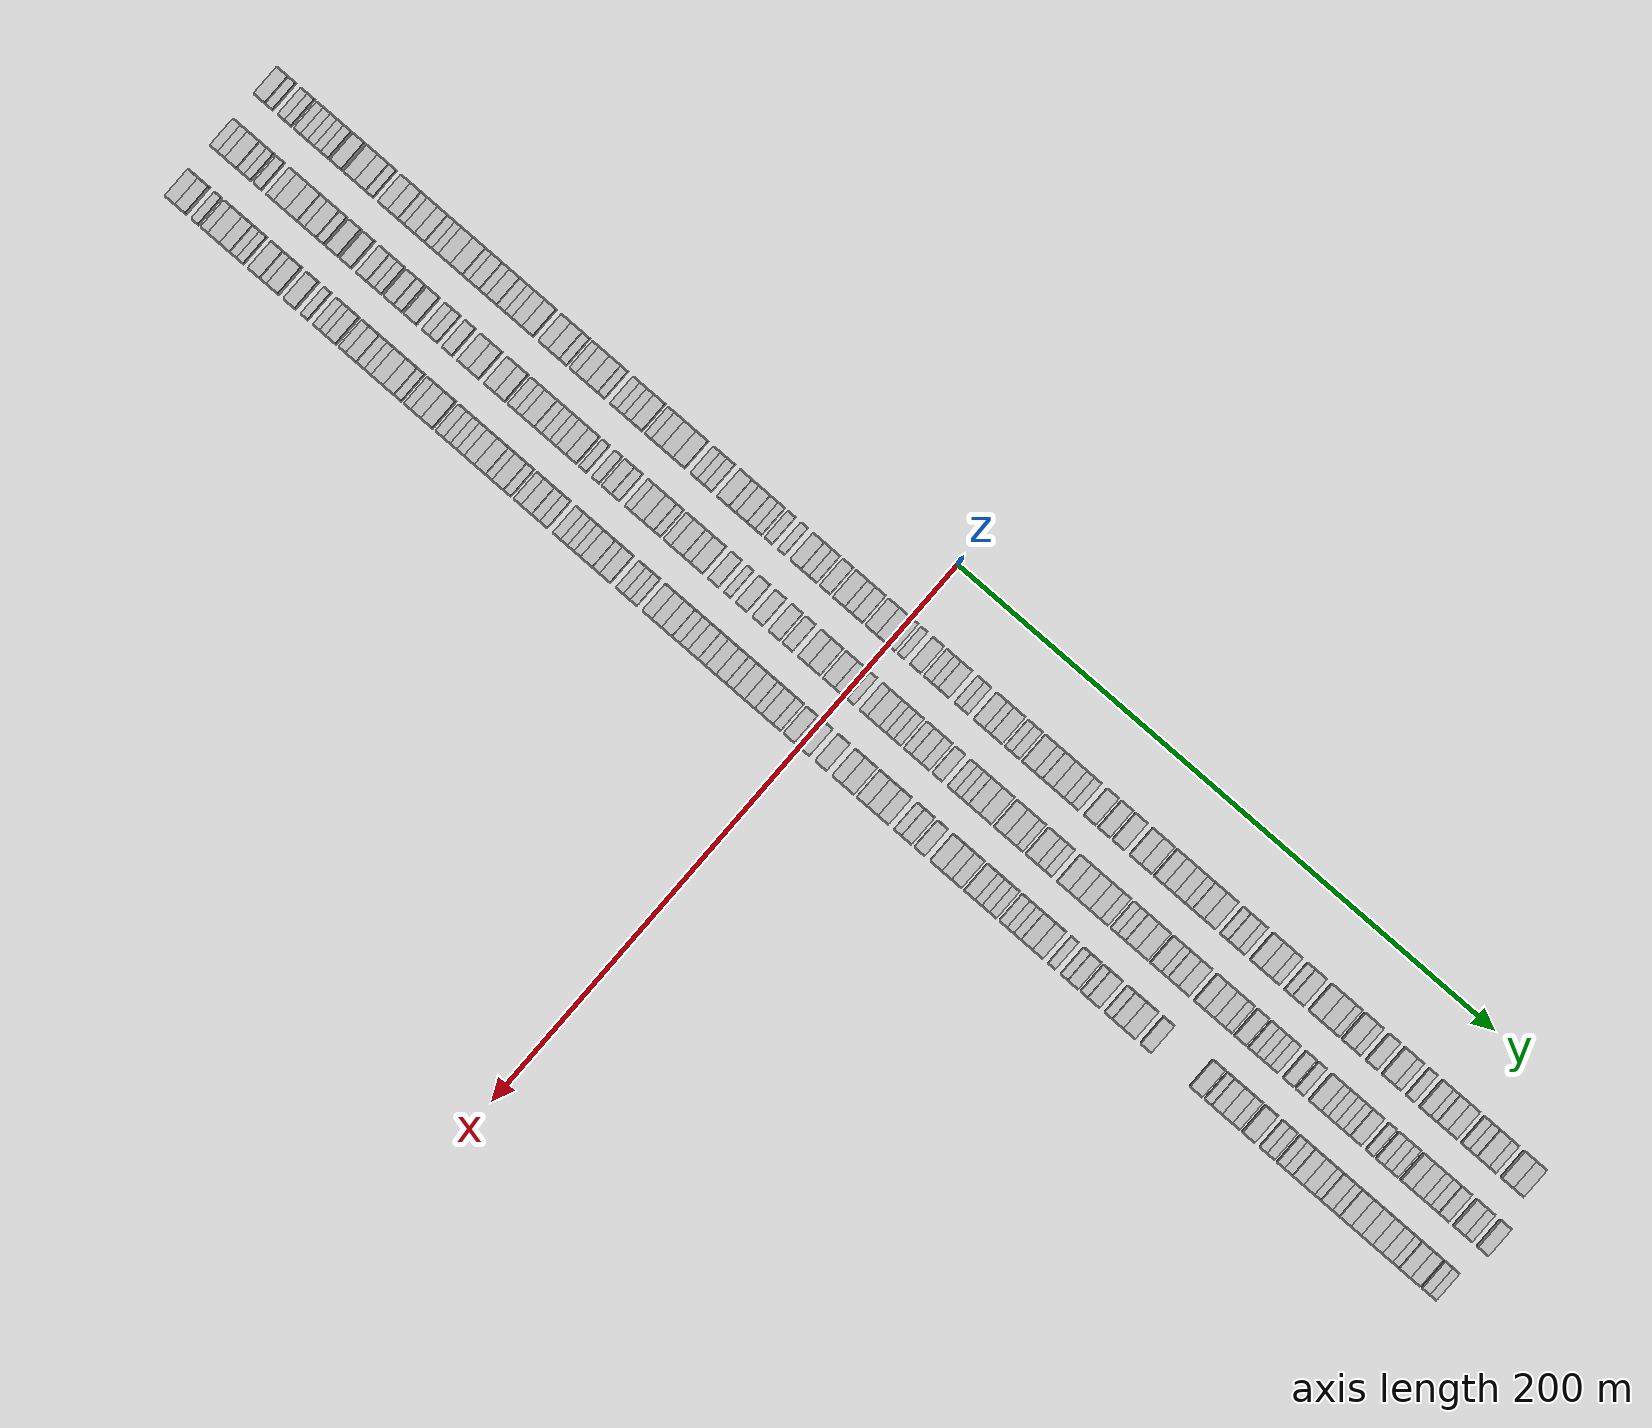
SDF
<sdf version="1.6">
 <world name="default">
  <scene>
   <sky><clouds><speed>12</speed></clouds></sky>
   <ambient>0.4 0.4 0.4 1</ambient>
   <background>0.7 0.7 0.7 1</background>
   <shadows>1</shadows>
  </scene>
  <gravity>0 0 -9.8066</gravity>
  <magnetic_field>6e-06 2.3e-05 -4.2e-05</magnetic_field>
  <physics default="0" name="default_physics" type="ode">
   <ode>
    <solver>
     <type>quick</type>
     <iters>10</iters>
     <sor>1.0</sor>
     <use_dynamic_moi_rescaling>0</use_dynamic_moi_rescaling>
    </solver>
    <constraints>
     <cfm>0</cfm>
     <erp>0.2</erp>
     <contact_max_correcting_vel>100</contact_max_correcting_vel>
     <contact_surface_layer>0.001</contact_surface_layer>
    </constraints>
   </ode>
   <max_step_size>0.004</max_step_size>
   <real_time_factor>1</real_time_factor>
   <real_time_update_rate>250</real_time_update_rate>
  </physics>
  <light name="sun" type="directional">
   <pose>0 0 10 0 0 0</pose>
   <diffuse>0.8 0.8 0.8 1</diffuse>
   <specular>0.2 0.2 0.2 1</specular>
   <attenuation>
    <range>1000</range>
    <constant>0.9</constant>
    <linear>0.01</linear>
    <quadratic>0.001</quadratic>
   </attenuation>
   <direction>-0.5 0.1 -0.9</direction>
  </light>
  <model name="building_1">
   <static>1</static>
   <pose>25.0000 -233.9420 0 0.000000 0.000000 0.000000</pose>
   <link name="link">
    <pose>0 0 4.50 0 0 0</pose>
    <collision name="collision"><geometry><box><size>10.0000 4.1160 9.0000</size></box></geometry></collision>
    <visual name="visual">
     <cast_shadows>0</cast_shadows>
     <geometry><box><size>10.0000 4.1160 9.0000</size></box></geometry>
     <material>
      <script>
       <uri>model://HANNAS_wall/materials/scripts</uri>
       <uri>model://HANNAS_wall/materials/textures</uri>
       <name>vrc/HANNAS_wall</name>
      </script>
     </material>
    </visual>
   </link>
  </model>
  <model name="building_2">
   <static>1</static>
   <pose>25.0000 -230.6009 0 0.000000 0.000000 0.000000</pose>
   <link name="link">
    <pose>0 0 3.00 0 0 0</pose>
    <collision name="collision"><geometry><box><size>10.0000 2.5662 6.0000</size></box></geometry></collision>
    <visual name="visual">
     <cast_shadows>0</cast_shadows>
     <geometry><box><size>10.0000 2.5662 6.0000</size></box></geometry>
     <material>
      <script>
       <uri>model://HANNAS_wall/materials/scripts</uri>
       <uri>model://HANNAS_wall/materials/textures</uri>
       <name>vrc/HANNAS_wall</name>
      </script>
     </material>
    </visual>
   </link>
  </model>
  <model name="building_3">
   <static>1</static>
   <pose>25.0000 -226.0514 0 0.000000 0.000000 0.000000</pose>
   <link name="link">
    <pose>0 0 3.00 0 0 0</pose>
    <collision name="collision"><geometry><box><size>10.0000 2.5329 6.0000</size></box></geometry></collision>
    <visual name="visual">
     <cast_shadows>0</cast_shadows>
     <geometry><box><size>10.0000 2.5329 6.0000</size></box></geometry>
     <material>
      <script>
       <uri>model://HANNAS_wall/materials/scripts</uri>
       <uri>model://HANNAS_wall/materials/textures</uri>
       <name>vrc/HANNAS_wall</name>
      </script>
     </material>
    </visual>
   </link>
  </model>
  <model name="building_4">
   <static>1</static>
   <pose>25.0000 -223.5698 0 0.000000 0.000000 0.000000</pose>
   <link name="link">
    <pose>0 0 3.00 0 0 0</pose>
    <collision name="collision"><geometry><box><size>10.0000 2.4303 6.0000</size></box></geometry></collision>
    <visual name="visual">
     <cast_shadows>0</cast_shadows>
     <geometry><box><size>10.0000 2.4303 6.0000</size></box></geometry>
     <material>
      <script>
       <uri>model://HANNAS_wall/materials/scripts</uri>
       <uri>model://HANNAS_wall/materials/textures</uri>
       <name>vrc/HANNAS_wall</name>
      </script>
     </material>
    </visual>
   </link>
  </model>
  <model name="building_5">
   <static>1</static>
   <pose>25.0000 -220.0891 0 0.000000 0.000000 0.000000</pose>
   <link name="link">
    <pose>0 0 3.00 0 0 0</pose>
    <collision name="collision"><geometry><box><size>10.0000 2.5312 6.0000</size></box></geometry></collision>
    <visual name="visual">
     <cast_shadows>0</cast_shadows>
     <geometry><box><size>10.0000 2.5312 6.0000</size></box></geometry>
     <material>
      <script>
       <uri>model://HANNAS_wall/materials/scripts</uri>
       <uri>model://HANNAS_wall/materials/textures</uri>
       <name>vrc/HANNAS_wall</name>
      </script>
     </material>
    </visual>
   </link>
  </model>
  <model name="building_6">
   <static>1</static>
   <pose>25.0000 -217.5162 0 0.000000 0.000000 0.000000</pose>
   <link name="link">
    <pose>0 0 3.00 0 0 0</pose>
    <collision name="collision"><geometry><box><size>10.0000 2.6145 6.0000</size></box></geometry></collision>
    <visual name="visual">
     <cast_shadows>0</cast_shadows>
     <geometry><box><size>10.0000 2.6145 6.0000</size></box></geometry>
     <material>
      <script>
       <uri>model://HANNAS_wall/materials/scripts</uri>
       <uri>model://HANNAS_wall/materials/textures</uri>
       <name>vrc/HANNAS_wall</name>
      </script>
     </material>
    </visual>
   </link>
  </model>
  <model name="building_7">
   <static>1</static>
   <pose>25.0000 -214.9641 0 0.000000 0.000000 0.000000</pose>
   <link name="link">
    <pose>0 0 3.00 0 0 0</pose>
    <collision name="collision"><geometry><box><size>10.0000 2.4898 6.0000</size></box></geometry></collision>
    <visual name="visual">
     <cast_shadows>0</cast_shadows>
     <geometry><box><size>10.0000 2.4898 6.0000</size></box></geometry>
     <material>
      <script>
       <uri>model://HANNAS_wall/materials/scripts</uri>
       <uri>model://HANNAS_wall/materials/textures</uri>
       <name>vrc/HANNAS_wall</name>
      </script>
     </material>
    </visual>
   </link>
  </model>
  <model name="building_8">
   <static>1</static>
   <pose>25.0000 -212.4872 0 0.000000 0.000000 0.000000</pose>
   <link name="link">
    <pose>0 0 3.00 0 0 0</pose>
    <collision name="collision"><geometry><box><size>10.0000 2.4640 6.0000</size></box></geometry></collision>
    <visual name="visual">
     <cast_shadows>0</cast_shadows>
     <geometry><box><size>10.0000 2.4640 6.0000</size></box></geometry>
     <material>
      <script>
       <uri>model://HANNAS_wall/materials/scripts</uri>
       <uri>model://HANNAS_wall/materials/textures</uri>
       <name>vrc/HANNAS_wall</name>
      </script>
     </material>
    </visual>
   </link>
  </model>
  <model name="building_9">
   <static>1</static>
   <pose>25.0000 -209.9251 0 0.000000 0.000000 0.000000</pose>
   <link name="link">
    <pose>0 0 3.00 0 0 0</pose>
    <collision name="collision"><geometry><box><size>10.0000 2.6602 6.0000</size></box></geometry></collision>
    <visual name="visual">
     <cast_shadows>0</cast_shadows>
     <geometry><box><size>10.0000 2.6602 6.0000</size></box></geometry>
     <material>
      <script>
       <uri>model://HANNAS_wall/materials/scripts</uri>
       <uri>model://HANNAS_wall/materials/textures</uri>
       <name>vrc/HANNAS_wall</name>
      </script>
     </material>
    </visual>
   </link>
  </model>
  <model name="building_10">
   <static>1</static>
   <pose>25.0000 -205.5535 0 0.000000 0.000000 0.000000</pose>
   <link name="link">
    <pose>0 0 4.50 0 0 0</pose>
    <collision name="collision"><geometry><box><size>10.0000 4.0828 9.0000</size></box></geometry></collision>
    <visual name="visual">
     <cast_shadows>0</cast_shadows>
     <geometry><box><size>10.0000 4.0828 9.0000</size></box></geometry>
     <material>
      <script>
       <uri>model://HANNAS_wall/materials/scripts</uri>
       <uri>model://HANNAS_wall/materials/textures</uri>
       <name>vrc/HANNAS_wall</name>
      </script>
     </material>
    </visual>
   </link>
  </model>
  <model name="building_11">
   <static>1</static>
   <pose>25.0000 -200.5111 0 0.000000 0.000000 0.000000</pose>
   <link name="link">
    <pose>0 0 4.50 0 0 0</pose>
    <collision name="collision"><geometry><box><size>10.0000 4.0020 9.0000</size></box></geometry></collision>
    <visual name="visual">
     <cast_shadows>0</cast_shadows>
     <geometry><box><size>10.0000 4.0020 9.0000</size></box></geometry>
     <material>
      <script>
       <uri>model://HANNAS_wall/materials/scripts</uri>
       <uri>model://HANNAS_wall/materials/textures</uri>
       <name>vrc/HANNAS_wall</name>
      </script>
     </material>
    </visual>
   </link>
  </model>
  <model name="building_12">
   <static>1</static>
   <pose>25.0000 -196.4841 0 0.000000 0.000000 0.000000</pose>
   <link name="link">
    <pose>0 0 4.50 0 0 0</pose>
    <collision name="collision"><geometry><box><size>10.0000 4.0521 9.0000</size></box></geometry></collision>
    <visual name="visual">
     <cast_shadows>0</cast_shadows>
     <geometry><box><size>10.0000 4.0521 9.0000</size></box></geometry>
     <material>
      <script>
       <uri>model://HANNAS_wall/materials/scripts</uri>
       <uri>model://HANNAS_wall/materials/textures</uri>
       <name>vrc/HANNAS_wall</name>
      </script>
     </material>
    </visual>
   </link>
  </model>
  <model name="building_13">
   <static>1</static>
   <pose>25.0000 -193.1769 0 0.000000 0.000000 0.000000</pose>
   <link name="link">
    <pose>0 0 3.00 0 0 0</pose>
    <collision name="collision"><geometry><box><size>10.0000 2.5623 6.0000</size></box></geometry></collision>
    <visual name="visual">
     <cast_shadows>0</cast_shadows>
     <geometry><box><size>10.0000 2.5623 6.0000</size></box></geometry>
     <material>
      <script>
       <uri>model://HANNAS_wall/materials/scripts</uri>
       <uri>model://HANNAS_wall/materials/textures</uri>
       <name>vrc/HANNAS_wall</name>
      </script>
     </material>
    </visual>
   </link>
  </model>
  <model name="building_14">
   <static>1</static>
   <pose>25.0000 -188.0685 0 0.000000 0.000000 0.000000</pose>
   <link name="link">
    <pose>0 0 4.50 0 0 0</pose>
    <collision name="collision"><geometry><box><size>10.0000 3.6544 9.0000</size></box></geometry></collision>
    <visual name="visual">
     <cast_shadows>0</cast_shadows>
     <geometry><box><size>10.0000 3.6544 9.0000</size></box></geometry>
     <material>
      <script>
       <uri>model://HANNAS_wall/materials/scripts</uri>
       <uri>model://HANNAS_wall/materials/textures</uri>
       <name>vrc/HANNAS_wall</name>
      </script>
     </material>
    </visual>
   </link>
  </model>
  <model name="building_15">
   <static>1</static>
   <pose>25.0000 -184.3394 0 0.000000 0.000000 0.000000</pose>
   <link name="link">
    <pose>0 0 4.50 0 0 0</pose>
    <collision name="collision"><geometry><box><size>10.0000 3.8039 9.0000</size></box></geometry></collision>
    <visual name="visual">
     <cast_shadows>0</cast_shadows>
     <geometry><box><size>10.0000 3.8039 9.0000</size></box></geometry>
     <material>
      <script>
       <uri>model://HANNAS_wall/materials/scripts</uri>
       <uri>model://HANNAS_wall/materials/textures</uri>
       <name>vrc/HANNAS_wall</name>
      </script>
     </material>
    </visual>
   </link>
  </model>
  <model name="building_16">
   <static>1</static>
   <pose>25.0000 -181.2196 0 0.000000 0.000000 0.000000</pose>
   <link name="link">
    <pose>0 0 3.00 0 0 0</pose>
    <collision name="collision"><geometry><box><size>10.0000 2.4358 6.0000</size></box></geometry></collision>
    <visual name="visual">
     <cast_shadows>0</cast_shadows>
     <geometry><box><size>10.0000 2.4358 6.0000</size></box></geometry>
     <material>
      <script>
       <uri>model://HANNAS_wall/materials/scripts</uri>
       <uri>model://HANNAS_wall/materials/textures</uri>
       <name>vrc/HANNAS_wall</name>
      </script>
     </material>
    </visual>
   </link>
  </model>
  <model name="building_17">
   <static>1</static>
   <pose>25.0000 -178.1028 0 0.000000 0.000000 0.000000</pose>
   <link name="link">
    <pose>0 0 4.50 0 0 0</pose>
    <collision name="collision"><geometry><box><size>10.0000 3.7978 9.0000</size></box></geometry></collision>
    <visual name="visual">
     <cast_shadows>0</cast_shadows>
     <geometry><box><size>10.0000 3.7978 9.0000</size></box></geometry>
     <material>
      <script>
       <uri>model://HANNAS_wall/materials/scripts</uri>
       <uri>model://HANNAS_wall/materials/textures</uri>
       <name>vrc/HANNAS_wall</name>
      </script>
     </material>
    </visual>
   </link>
  </model>
  <model name="building_18">
   <static>1</static>
   <pose>25.0000 -174.3816 0 0.000000 0.000000 0.000000</pose>
   <link name="link">
    <pose>0 0 4.50 0 0 0</pose>
    <collision name="collision"><geometry><box><size>10.0000 3.6447 9.0000</size></box></geometry></collision>
    <visual name="visual">
     <cast_shadows>0</cast_shadows>
     <geometry><box><size>10.0000 3.6447 9.0000</size></box></geometry>
     <material>
      <script>
       <uri>model://HANNAS_wall/materials/scripts</uri>
       <uri>model://HANNAS_wall/materials/textures</uri>
       <name>vrc/HANNAS_wall</name>
      </script>
     </material>
    </visual>
   </link>
  </model>
  <model name="building_19">
   <static>1</static>
   <pose>25.0000 -171.2212 0 0.000000 0.000000 0.000000</pose>
   <link name="link">
    <pose>0 0 3.00 0 0 0</pose>
    <collision name="collision"><geometry><box><size>10.0000 2.6760 6.0000</size></box></geometry></collision>
    <visual name="visual">
     <cast_shadows>0</cast_shadows>
     <geometry><box><size>10.0000 2.6760 6.0000</size></box></geometry>
     <material>
      <script>
       <uri>model://HANNAS_wall/materials/scripts</uri>
       <uri>model://HANNAS_wall/materials/textures</uri>
       <name>vrc/HANNAS_wall</name>
      </script>
     </material>
    </visual>
   </link>
  </model>
  <model name="building_20">
   <static>1</static>
   <pose>25.0000 -168.6343 0 0.000000 0.000000 0.000000</pose>
   <link name="link">
    <pose>0 0 3.00 0 0 0</pose>
    <collision name="collision"><geometry><box><size>10.0000 2.4978 6.0000</size></box></geometry></collision>
    <visual name="visual">
     <cast_shadows>0</cast_shadows>
     <geometry><box><size>10.0000 2.4978 6.0000</size></box></geometry>
     <material>
      <script>
       <uri>model://HANNAS_wall/materials/scripts</uri>
       <uri>model://HANNAS_wall/materials/textures</uri>
       <name>vrc/HANNAS_wall</name>
      </script>
     </material>
    </visual>
   </link>
  </model>
  <model name="building_21">
   <static>1</static>
   <pose>25.0000 -165.1822 0 0.000000 0.000000 0.000000</pose>
   <link name="link">
    <pose>0 0 4.50 0 0 0</pose>
    <collision name="collision"><geometry><box><size>10.0000 4.4065 9.0000</size></box></geometry></collision>
    <visual name="visual">
     <cast_shadows>0</cast_shadows>
     <geometry><box><size>10.0000 4.4065 9.0000</size></box></geometry>
     <material>
      <script>
       <uri>model://HANNAS_wall/materials/scripts</uri>
       <uri>model://HANNAS_wall/materials/textures</uri>
       <name>vrc/HANNAS_wall</name>
      </script>
     </material>
    </visual>
   </link>
  </model>
  <model name="building_22">
   <static>1</static>
   <pose>25.0000 -160.7298 0 0.000000 0.000000 0.000000</pose>
   <link name="link">
    <pose>0 0 4.50 0 0 0</pose>
    <collision name="collision"><geometry><box><size>10.0000 4.4983 9.0000</size></box></geometry></collision>
    <visual name="visual">
     <cast_shadows>0</cast_shadows>
     <geometry><box><size>10.0000 4.4983 9.0000</size></box></geometry>
     <material>
      <script>
       <uri>model://HANNAS_wall/materials/scripts</uri>
       <uri>model://HANNAS_wall/materials/textures</uri>
       <name>vrc/HANNAS_wall</name>
      </script>
     </material>
    </visual>
   </link>
  </model>
  <model name="building_23">
   <static>1</static>
   <pose>25.0000 -157.2672 0 0.000000 0.000000 0.000000</pose>
   <link name="link">
    <pose>0 0 3.00 0 0 0</pose>
    <collision name="collision"><geometry><box><size>10.0000 2.4268 6.0000</size></box></geometry></collision>
    <visual name="visual">
     <cast_shadows>0</cast_shadows>
     <geometry><box><size>10.0000 2.4268 6.0000</size></box></geometry>
     <material>
      <script>
       <uri>model://HANNAS_wall/materials/scripts</uri>
       <uri>model://HANNAS_wall/materials/textures</uri>
       <name>vrc/HANNAS_wall</name>
      </script>
     </material>
    </visual>
   </link>
  </model>
  <model name="building_24">
   <static>1</static>
   <pose>25.0000 -154.1374 0 0.000000 0.000000 0.000000</pose>
   <link name="link">
    <pose>0 0 4.50 0 0 0</pose>
    <collision name="collision"><geometry><box><size>10.0000 3.8329 9.0000</size></box></geometry></collision>
    <visual name="visual">
     <cast_shadows>0</cast_shadows>
     <geometry><box><size>10.0000 3.8329 9.0000</size></box></geometry>
     <material>
      <script>
       <uri>model://HANNAS_wall/materials/scripts</uri>
       <uri>model://HANNAS_wall/materials/textures</uri>
       <name>vrc/HANNAS_wall</name>
      </script>
     </material>
    </visual>
   </link>
  </model>
  <model name="building_25">
   <static>1</static>
   <pose>25.0000 -150.8480 0 0.000000 0.000000 0.000000</pose>
   <link name="link">
    <pose>0 0 3.00 0 0 0</pose>
    <collision name="collision"><geometry><box><size>10.0000 2.7458 6.0000</size></box></geometry></collision>
    <visual name="visual">
     <cast_shadows>0</cast_shadows>
     <geometry><box><size>10.0000 2.7458 6.0000</size></box></geometry>
     <material>
      <script>
       <uri>model://HANNAS_wall/materials/scripts</uri>
       <uri>model://HANNAS_wall/materials/textures</uri>
       <name>vrc/HANNAS_wall</name>
      </script>
     </material>
    </visual>
   </link>
  </model>
  <model name="building_26">
   <static>1</static>
   <pose>25.0000 -147.6009 0 0.000000 0.000000 0.000000</pose>
   <link name="link">
    <pose>0 0 4.50 0 0 0</pose>
    <collision name="collision"><geometry><box><size>10.0000 3.7486 9.0000</size></box></geometry></collision>
    <visual name="visual">
     <cast_shadows>0</cast_shadows>
     <geometry><box><size>10.0000 3.7486 9.0000</size></box></geometry>
     <material>
      <script>
       <uri>model://HANNAS_wall/materials/scripts</uri>
       <uri>model://HANNAS_wall/materials/textures</uri>
       <name>vrc/HANNAS_wall</name>
      </script>
     </material>
    </visual>
   </link>
  </model>
  <model name="building_27">
   <static>1</static>
   <pose>25.0000 -144.2960 0 0.000000 0.000000 0.000000</pose>
   <link name="link">
    <pose>0 0 3.00 0 0 0</pose>
    <collision name="collision"><geometry><box><size>10.0000 2.8612 6.0000</size></box></geometry></collision>
    <visual name="visual">
     <cast_shadows>0</cast_shadows>
     <geometry><box><size>10.0000 2.8612 6.0000</size></box></geometry>
     <material>
      <script>
       <uri>model://HANNAS_wall/materials/scripts</uri>
       <uri>model://HANNAS_wall/materials/textures</uri>
       <name>vrc/HANNAS_wall</name>
      </script>
     </material>
    </visual>
   </link>
  </model>
  <model name="building_28">
   <static>1</static>
   <pose>25.0000 -141.5084 0 0.000000 0.000000 0.000000</pose>
   <link name="link">
    <pose>0 0 3.00 0 0 0</pose>
    <collision name="collision"><geometry><box><size>10.0000 2.7138 6.0000</size></box></geometry></collision>
    <visual name="visual">
     <cast_shadows>0</cast_shadows>
     <geometry><box><size>10.0000 2.7138 6.0000</size></box></geometry>
     <material>
      <script>
       <uri>model://HANNAS_wall/materials/scripts</uri>
       <uri>model://HANNAS_wall/materials/textures</uri>
       <name>vrc/HANNAS_wall</name>
      </script>
     </material>
    </visual>
   </link>
  </model>
  <model name="building_29">
   <static>1</static>
   <pose>25.0000 -138.2250 0 0.000000 0.000000 0.000000</pose>
   <link name="link">
    <pose>0 0 4.50 0 0 0</pose>
    <collision name="collision"><geometry><box><size>10.0000 3.8531 9.0000</size></box></geometry></collision>
    <visual name="visual">
     <cast_shadows>0</cast_shadows>
     <geometry><box><size>10.0000 3.8531 9.0000</size></box></geometry>
     <material>
      <script>
       <uri>model://HANNAS_wall/materials/scripts</uri>
       <uri>model://HANNAS_wall/materials/textures</uri>
       <name>vrc/HANNAS_wall</name>
      </script>
     </material>
    </visual>
   </link>
  </model>
  <model name="building_30">
   <static>1</static>
   <pose>25.0000 -134.2872 0 0.000000 0.000000 0.000000</pose>
   <link name="link">
    <pose>0 0 4.50 0 0 0</pose>
    <collision name="collision"><geometry><box><size>10.0000 4.0226 9.0000</size></box></geometry></collision>
    <visual name="visual">
     <cast_shadows>0</cast_shadows>
     <geometry><box><size>10.0000 4.0226 9.0000</size></box></geometry>
     <material>
      <script>
       <uri>model://HANNAS_wall/materials/scripts</uri>
       <uri>model://HANNAS_wall/materials/textures</uri>
       <name>vrc/HANNAS_wall</name>
      </script>
     </material>
    </visual>
   </link>
  </model>
  <model name="building_31">
   <static>1</static>
   <pose>25.0000 -128.4389 0 0.000000 0.000000 0.000000</pose>
   <link name="link">
    <pose>0 0 4.50 0 0 0</pose>
    <collision name="collision"><geometry><box><size>10.0000 3.6739 9.0000</size></box></geometry></collision>
    <visual name="visual">
     <cast_shadows>0</cast_shadows>
     <geometry><box><size>10.0000 3.6739 9.0000</size></box></geometry>
     <material>
      <script>
       <uri>model://HANNAS_wall/materials/scripts</uri>
       <uri>model://HANNAS_wall/materials/textures</uri>
       <name>vrc/HANNAS_wall</name>
      </script>
     </material>
    </visual>
   </link>
  </model>
  <model name="building_32">
   <static>1</static>
   <pose>25.0000 -124.5417 0 0.000000 0.000000 0.000000</pose>
   <link name="link">
    <pose>0 0 4.50 0 0 0</pose>
    <collision name="collision"><geometry><box><size>10.0000 4.1206 9.0000</size></box></geometry></collision>
    <visual name="visual">
     <cast_shadows>0</cast_shadows>
     <geometry><box><size>10.0000 4.1206 9.0000</size></box></geometry>
     <material>
      <script>
       <uri>model://HANNAS_wall/materials/scripts</uri>
       <uri>model://HANNAS_wall/materials/textures</uri>
       <name>vrc/HANNAS_wall</name>
      </script>
     </material>
    </visual>
   </link>
  </model>
  <model name="building_33">
   <static>1</static>
   <pose>25.0000 -121.1774 0 0.000000 0.000000 0.000000</pose>
   <link name="link">
    <pose>0 0 3.00 0 0 0</pose>
    <collision name="collision"><geometry><box><size>10.0000 2.6078 6.0000</size></box></geometry></collision>
    <visual name="visual">
     <cast_shadows>0</cast_shadows>
     <geometry><box><size>10.0000 2.6078 6.0000</size></box></geometry>
     <material>
      <script>
       <uri>model://HANNAS_wall/materials/scripts</uri>
       <uri>model://HANNAS_wall/materials/textures</uri>
       <name>vrc/HANNAS_wall</name>
      </script>
     </material>
    </visual>
   </link>
  </model>
  <model name="building_34">
   <static>1</static>
   <pose>25.0000 -117.5598 0 0.000000 0.000000 0.000000</pose>
   <link name="link">
    <pose>0 0 3.00 0 0 0</pose>
    <collision name="collision"><geometry><box><size>10.0000 2.6275 6.0000</size></box></geometry></collision>
    <visual name="visual">
     <cast_shadows>0</cast_shadows>
     <geometry><box><size>10.0000 2.6275 6.0000</size></box></geometry>
     <material>
      <script>
       <uri>model://HANNAS_wall/materials/scripts</uri>
       <uri>model://HANNAS_wall/materials/textures</uri>
       <name>vrc/HANNAS_wall</name>
      </script>
     </material>
    </visual>
   </link>
  </model>
  <model name="building_35">
   <static>1</static>
   <pose>25.0000 -114.2830 0 0.000000 0.000000 0.000000</pose>
   <link name="link">
    <pose>0 0 4.50 0 0 0</pose>
    <collision name="collision"><geometry><box><size>10.0000 3.9260 9.0000</size></box></geometry></collision>
    <visual name="visual">
     <cast_shadows>0</cast_shadows>
     <geometry><box><size>10.0000 3.9260 9.0000</size></box></geometry>
     <material>
      <script>
       <uri>model://HANNAS_wall/materials/scripts</uri>
       <uri>model://HANNAS_wall/materials/textures</uri>
       <name>vrc/HANNAS_wall</name>
      </script>
     </material>
    </visual>
   </link>
  </model>
  <model name="building_36">
   <static>1</static>
   <pose>25.0000 -110.2550 0 0.000000 0.000000 0.000000</pose>
   <link name="link">
    <pose>0 0 4.50 0 0 0</pose>
    <collision name="collision"><geometry><box><size>10.0000 4.1302 9.0000</size></box></geometry></collision>
    <visual name="visual">
     <cast_shadows>0</cast_shadows>
     <geometry><box><size>10.0000 4.1302 9.0000</size></box></geometry>
     <material>
      <script>
       <uri>model://HANNAS_wall/materials/scripts</uri>
       <uri>model://HANNAS_wall/materials/textures</uri>
       <name>vrc/HANNAS_wall</name>
      </script>
     </material>
    </visual>
   </link>
  </model>
  <model name="building_37">
   <static>1</static>
   <pose>25.0000 -106.9513 0 0.000000 0.000000 0.000000</pose>
   <link name="link">
    <pose>0 0 3.00 0 0 0</pose>
    <collision name="collision"><geometry><box><size>10.0000 2.4772 6.0000</size></box></geometry></collision>
    <visual name="visual">
     <cast_shadows>0</cast_shadows>
     <geometry><box><size>10.0000 2.4772 6.0000</size></box></geometry>
     <material>
      <script>
       <uri>model://HANNAS_wall/materials/scripts</uri>
       <uri>model://HANNAS_wall/materials/textures</uri>
       <name>vrc/HANNAS_wall</name>
      </script>
     </material>
    </visual>
   </link>
  </model>
  <model name="building_38">
   <static>1</static>
   <pose>25.0000 -102.3991 0 0.000000 0.000000 0.000000</pose>
   <link name="link">
    <pose>0 0 3.00 0 0 0</pose>
    <collision name="collision"><geometry><box><size>10.0000 2.6270 6.0000</size></box></geometry></collision>
    <visual name="visual">
     <cast_shadows>0</cast_shadows>
     <geometry><box><size>10.0000 2.6270 6.0000</size></box></geometry>
     <material>
      <script>
       <uri>model://HANNAS_wall/materials/scripts</uri>
       <uri>model://HANNAS_wall/materials/textures</uri>
       <name>vrc/HANNAS_wall</name>
      </script>
     </material>
    </visual>
   </link>
  </model>
  <model name="building_39">
   <static>1</static>
   <pose>25.0000 -99.8276 0 0.000000 0.000000 0.000000</pose>
   <link name="link">
    <pose>0 0 3.00 0 0 0</pose>
    <collision name="collision"><geometry><box><size>10.0000 2.5159 6.0000</size></box></geometry></collision>
    <visual name="visual">
     <cast_shadows>0</cast_shadows>
     <geometry><box><size>10.0000 2.5159 6.0000</size></box></geometry>
     <material>
      <script>
       <uri>model://HANNAS_wall/materials/scripts</uri>
       <uri>model://HANNAS_wall/materials/textures</uri>
       <name>vrc/HANNAS_wall</name>
      </script>
     </material>
    </visual>
   </link>
  </model>
  <model name="building_40">
   <static>1</static>
   <pose>25.0000 -97.1902 0 0.000000 0.000000 0.000000</pose>
   <link name="link">
    <pose>0 0 3.00 0 0 0</pose>
    <collision name="collision"><geometry><box><size>10.0000 2.7589 6.0000</size></box></geometry></collision>
    <visual name="visual">
     <cast_shadows>0</cast_shadows>
     <geometry><box><size>10.0000 2.7589 6.0000</size></box></geometry>
     <material>
      <script>
       <uri>model://HANNAS_wall/materials/scripts</uri>
       <uri>model://HANNAS_wall/materials/textures</uri>
       <name>vrc/HANNAS_wall</name>
      </script>
     </material>
    </visual>
   </link>
  </model>
  <model name="building_41">
   <static>1</static>
   <pose>25.0000 -93.7795 0 0.000000 0.000000 0.000000</pose>
   <link name="link">
    <pose>0 0 4.50 0 0 0</pose>
    <collision name="collision"><geometry><box><size>10.0000 4.0625 9.0000</size></box></geometry></collision>
    <visual name="visual">
     <cast_shadows>0</cast_shadows>
     <geometry><box><size>10.0000 4.0625 9.0000</size></box></geometry>
     <material>
      <script>
       <uri>model://HANNAS_wall/materials/scripts</uri>
       <uri>model://HANNAS_wall/materials/textures</uri>
       <name>vrc/HANNAS_wall</name>
      </script>
     </material>
    </visual>
   </link>
  </model>
  <model name="building_42">
   <static>1</static>
   <pose>25.0000 -89.4730 0 0.000000 0.000000 0.000000</pose>
   <link name="link">
    <pose>0 0 3.00 0 0 0</pose>
    <collision name="collision"><geometry><box><size>10.0000 2.5506 6.0000</size></box></geometry></collision>
    <visual name="visual">
     <cast_shadows>0</cast_shadows>
     <geometry><box><size>10.0000 2.5506 6.0000</size></box></geometry>
     <material>
      <script>
       <uri>model://HANNAS_wall/materials/scripts</uri>
       <uri>model://HANNAS_wall/materials/textures</uri>
       <name>vrc/HANNAS_wall</name>
      </script>
     </material>
    </visual>
   </link>
  </model>
  <model name="building_43">
   <static>1</static>
   <pose>25.0000 -86.3629 0 0.000000 0.000000 0.000000</pose>
   <link name="link">
    <pose>0 0 4.50 0 0 0</pose>
    <collision name="collision"><geometry><box><size>10.0000 3.6694 9.0000</size></box></geometry></collision>
    <visual name="visual">
     <cast_shadows>0</cast_shadows>
     <geometry><box><size>10.0000 3.6694 9.0000</size></box></geometry>
     <material>
      <script>
       <uri>model://HANNAS_wall/materials/scripts</uri>
       <uri>model://HANNAS_wall/materials/textures</uri>
       <name>vrc/HANNAS_wall</name>
      </script>
     </material>
    </visual>
   </link>
  </model>
  <model name="building_44">
   <static>1</static>
   <pose>25.0000 -82.3609 0 0.000000 0.000000 0.000000</pose>
   <link name="link">
    <pose>0 0 4.50 0 0 0</pose>
    <collision name="collision"><geometry><box><size>10.0000 4.3346 9.0000</size></box></geometry></collision>
    <visual name="visual">
     <cast_shadows>0</cast_shadows>
     <geometry><box><size>10.0000 4.3346 9.0000</size></box></geometry>
     <material>
      <script>
       <uri>model://HANNAS_wall/materials/scripts</uri>
       <uri>model://HANNAS_wall/materials/textures</uri>
       <name>vrc/HANNAS_wall</name>
      </script>
     </material>
    </visual>
   </link>
  </model>
  <model name="building_45">
   <static>1</static>
   <pose>25.0000 -78.0160 0 0.000000 0.000000 0.000000</pose>
   <link name="link">
    <pose>0 0 4.50 0 0 0</pose>
    <collision name="collision"><geometry><box><size>10.0000 4.3552 9.0000</size></box></geometry></collision>
    <visual name="visual">
     <cast_shadows>0</cast_shadows>
     <geometry><box><size>10.0000 4.3552 9.0000</size></box></geometry>
     <material>
      <script>
       <uri>model://HANNAS_wall/materials/scripts</uri>
       <uri>model://HANNAS_wall/materials/textures</uri>
       <name>vrc/HANNAS_wall</name>
      </script>
     </material>
    </visual>
   </link>
  </model>
  <model name="building_46">
   <static>1</static>
   <pose>25.0000 -72.5112 0 0.000000 0.000000 0.000000</pose>
   <link name="link">
    <pose>0 0 3.00 0 0 0</pose>
    <collision name="collision"><geometry><box><size>10.0000 2.6545 6.0000</size></box></geometry></collision>
    <visual name="visual">
     <cast_shadows>0</cast_shadows>
     <geometry><box><size>10.0000 2.6545 6.0000</size></box></geometry>
     <material>
      <script>
       <uri>model://HANNAS_wall/materials/scripts</uri>
       <uri>model://HANNAS_wall/materials/textures</uri>
       <name>vrc/HANNAS_wall</name>
      </script>
     </material>
    </visual>
   </link>
  </model>
  <model name="building_47">
   <static>1</static>
   <pose>25.0000 -69.9374 0 0.000000 0.000000 0.000000</pose>
   <link name="link">
    <pose>0 0 3.00 0 0 0</pose>
    <collision name="collision"><geometry><box><size>10.0000 2.4931 6.0000</size></box></geometry></collision>
    <visual name="visual">
     <cast_shadows>0</cast_shadows>
     <geometry><box><size>10.0000 2.4931 6.0000</size></box></geometry>
     <material>
      <script>
       <uri>model://HANNAS_wall/materials/scripts</uri>
       <uri>model://HANNAS_wall/materials/textures</uri>
       <name>vrc/HANNAS_wall</name>
      </script>
     </material>
    </visual>
   </link>
  </model>
  <model name="building_48">
   <static>1</static>
   <pose>25.0000 -67.2737 0 0.000000 0.000000 0.000000</pose>
   <link name="link">
    <pose>0 0 3.00 0 0 0</pose>
    <collision name="collision"><geometry><box><size>10.0000 2.8341 6.0000</size></box></geometry></collision>
    <visual name="visual">
     <cast_shadows>0</cast_shadows>
     <geometry><box><size>10.0000 2.8341 6.0000</size></box></geometry>
     <material>
      <script>
       <uri>model://HANNAS_wall/materials/scripts</uri>
       <uri>model://HANNAS_wall/materials/textures</uri>
       <name>vrc/HANNAS_wall</name>
      </script>
     </material>
    </visual>
   </link>
  </model>
  <model name="building_49">
   <static>1</static>
   <pose>25.0000 -61.6095 0 0.000000 0.000000 0.000000</pose>
   <link name="link">
    <pose>0 0 4.50 0 0 0</pose>
    <collision name="collision"><geometry><box><size>10.0000 4.4944 9.0000</size></box></geometry></collision>
    <visual name="visual">
     <cast_shadows>0</cast_shadows>
     <geometry><box><size>10.0000 4.4944 9.0000</size></box></geometry>
     <material>
      <script>
       <uri>model://HANNAS_wall/materials/scripts</uri>
       <uri>model://HANNAS_wall/materials/textures</uri>
       <name>vrc/HANNAS_wall</name>
      </script>
     </material>
    </visual>
   </link>
  </model>
  <model name="building_50">
   <static>1</static>
   <pose>25.0000 -58.0694 0 0.000000 0.000000 0.000000</pose>
   <link name="link">
    <pose>0 0 3.00 0 0 0</pose>
    <collision name="collision"><geometry><box><size>10.0000 2.5858 6.0000</size></box></geometry></collision>
    <visual name="visual">
     <cast_shadows>0</cast_shadows>
     <geometry><box><size>10.0000 2.5858 6.0000</size></box></geometry>
     <material>
      <script>
       <uri>model://HANNAS_wall/materials/scripts</uri>
       <uri>model://HANNAS_wall/materials/textures</uri>
       <name>vrc/HANNAS_wall</name>
      </script>
     </material>
    </visual>
   </link>
  </model>
  <model name="building_51">
   <static>1</static>
   <pose>25.0000 -54.7039 0 0.000000 0.000000 0.000000</pose>
   <link name="link">
    <pose>0 0 4.50 0 0 0</pose>
    <collision name="collision"><geometry><box><size>10.0000 4.1450 9.0000</size></box></geometry></collision>
    <visual name="visual">
     <cast_shadows>0</cast_shadows>
     <geometry><box><size>10.0000 4.1450 9.0000</size></box></geometry>
     <material>
      <script>
       <uri>model://HANNAS_wall/materials/scripts</uri>
       <uri>model://HANNAS_wall/materials/textures</uri>
       <name>vrc/HANNAS_wall</name>
      </script>
     </material>
    </visual>
   </link>
  </model>
  <model name="building_52">
   <static>1</static>
   <pose>25.0000 -51.1662 0 0.000000 0.000000 0.000000</pose>
   <link name="link">
    <pose>0 0 3.00 0 0 0</pose>
    <collision name="collision"><geometry><box><size>10.0000 2.9303 6.0000</size></box></geometry></collision>
    <visual name="visual">
     <cast_shadows>0</cast_shadows>
     <geometry><box><size>10.0000 2.9303 6.0000</size></box></geometry>
     <material>
      <script>
       <uri>model://HANNAS_wall/materials/scripts</uri>
       <uri>model://HANNAS_wall/materials/textures</uri>
       <name>vrc/HANNAS_wall</name>
      </script>
     </material>
    </visual>
   </link>
  </model>
  <model name="building_53">
   <static>1</static>
   <pose>25.0000 -48.4626 0 0.000000 0.000000 0.000000</pose>
   <link name="link">
    <pose>0 0 3.00 0 0 0</pose>
    <collision name="collision"><geometry><box><size>10.0000 2.4770 6.0000</size></box></geometry></collision>
    <visual name="visual">
     <cast_shadows>0</cast_shadows>
     <geometry><box><size>10.0000 2.4770 6.0000</size></box></geometry>
     <material>
      <script>
       <uri>model://HANNAS_wall/materials/scripts</uri>
       <uri>model://HANNAS_wall/materials/textures</uri>
       <name>vrc/HANNAS_wall</name>
      </script>
     </material>
    </visual>
   </link>
  </model>
  <model name="building_54">
   <static>1</static>
   <pose>25.0000 -44.7541 0 0.000000 0.000000 0.000000</pose>
   <link name="link">
    <pose>0 0 3.00 0 0 0</pose>
    <collision name="collision"><geometry><box><size>10.0000 2.9400 6.0000</size></box></geometry></collision>
    <visual name="visual">
     <cast_shadows>0</cast_shadows>
     <geometry><box><size>10.0000 2.9400 6.0000</size></box></geometry>
     <material>
      <script>
       <uri>model://HANNAS_wall/materials/scripts</uri>
       <uri>model://HANNAS_wall/materials/textures</uri>
       <name>vrc/HANNAS_wall</name>
      </script>
     </material>
    </visual>
   </link>
  </model>
  <model name="building_55">
   <static>1</static>
   <pose>25.0000 -39.9976 0 0.000000 0.000000 0.000000</pose>
   <link name="link">
    <pose>0 0 3.00 0 0 0</pose>
    <collision name="collision"><geometry><box><size>10.0000 2.5729 6.0000</size></box></geometry></collision>
    <visual name="visual">
     <cast_shadows>0</cast_shadows>
     <geometry><box><size>10.0000 2.5729 6.0000</size></box></geometry>
     <material>
      <script>
       <uri>model://HANNAS_wall/materials/scripts</uri>
       <uri>model://HANNAS_wall/materials/textures</uri>
       <name>vrc/HANNAS_wall</name>
      </script>
     </material>
    </visual>
   </link>
  </model>
  <model name="building_56">
   <static>1</static>
   <pose>25.0000 -34.6225 0 0.000000 0.000000 0.000000</pose>
   <link name="link">
    <pose>0 0 4.50 0 0 0</pose>
    <collision name="collision"><geometry><box><size>10.0000 4.1774 9.0000</size></box></geometry></collision>
    <visual name="visual">
     <cast_shadows>0</cast_shadows>
     <geometry><box><size>10.0000 4.1774 9.0000</size></box></geometry>
     <material>
      <script>
       <uri>model://HANNAS_wall/materials/scripts</uri>
       <uri>model://HANNAS_wall/materials/textures</uri>
       <name>vrc/HANNAS_wall</name>
      </script>
     </material>
    </visual>
   </link>
  </model>
  <model name="building_57">
   <static>1</static>
   <pose>25.0000 -31.0649 0 0.000000 0.000000 0.000000</pose>
   <link name="link">
    <pose>0 0 3.00 0 0 0</pose>
    <collision name="collision"><geometry><box><size>10.0000 2.9377 6.0000</size></box></geometry></collision>
    <visual name="visual">
     <cast_shadows>0</cast_shadows>
     <geometry><box><size>10.0000 2.9377 6.0000</size></box></geometry>
     <material>
      <script>
       <uri>model://HANNAS_wall/materials/scripts</uri>
       <uri>model://HANNAS_wall/materials/textures</uri>
       <name>vrc/HANNAS_wall</name>
      </script>
     </material>
    </visual>
   </link>
  </model>
  <model name="building_58">
   <static>1</static>
   <pose>25.0000 -28.1471 0 0.000000 0.000000 0.000000</pose>
   <link name="link">
    <pose>0 0 3.00 0 0 0</pose>
    <collision name="collision"><geometry><box><size>10.0000 2.8979 6.0000</size></box></geometry></collision>
    <visual name="visual">
     <cast_shadows>0</cast_shadows>
     <geometry><box><size>10.0000 2.8979 6.0000</size></box></geometry>
     <material>
      <script>
       <uri>model://HANNAS_wall/materials/scripts</uri>
       <uri>model://HANNAS_wall/materials/textures</uri>
       <name>vrc/HANNAS_wall</name>
      </script>
     </material>
    </visual>
   </link>
  </model>
  <model name="building_59">
   <static>1</static>
   <pose>25.0000 -23.7304 0 0.000000 0.000000 0.000000</pose>
   <link name="link">
    <pose>0 0 4.50 0 0 0</pose>
    <collision name="collision"><geometry><box><size>10.0000 3.9353 9.0000</size></box></geometry></collision>
    <visual name="visual">
     <cast_shadows>0</cast_shadows>
     <geometry><box><size>10.0000 3.9353 9.0000</size></box></geometry>
     <material>
      <script>
       <uri>model://HANNAS_wall/materials/scripts</uri>
       <uri>model://HANNAS_wall/materials/textures</uri>
       <name>vrc/HANNAS_wall</name>
      </script>
     </material>
    </visual>
   </link>
  </model>
  <model name="building_60">
   <static>1</static>
   <pose>25.0000 -18.5632 0 0.000000 0.000000 0.000000</pose>
   <link name="link">
    <pose>0 0 4.50 0 0 0</pose>
    <collision name="collision"><geometry><box><size>10.0000 4.3992 9.0000</size></box></geometry></collision>
    <visual name="visual">
     <cast_shadows>0</cast_shadows>
     <geometry><box><size>10.0000 4.3992 9.0000</size></box></geometry>
     <material>
      <script>
       <uri>model://HANNAS_wall/materials/scripts</uri>
       <uri>model://HANNAS_wall/materials/textures</uri>
       <name>vrc/HANNAS_wall</name>
      </script>
     </material>
    </visual>
   </link>
  </model>
  <model name="building_61">
   <static>1</static>
   <pose>25.0000 -14.9277 0 0.000000 0.000000 0.000000</pose>
   <link name="link">
    <pose>0 0 3.00 0 0 0</pose>
    <collision name="collision"><geometry><box><size>10.0000 2.8717 6.0000</size></box></geometry></collision>
    <visual name="visual">
     <cast_shadows>0</cast_shadows>
     <geometry><box><size>10.0000 2.8717 6.0000</size></box></geometry>
     <material>
      <script>
       <uri>model://HANNAS_wall/materials/scripts</uri>
       <uri>model://HANNAS_wall/materials/textures</uri>
       <name>vrc/HANNAS_wall</name>
      </script>
     </material>
    </visual>
   </link>
  </model>
  <model name="building_62">
   <static>1</static>
   <pose>25.0000 -11.5971 0 0.000000 0.000000 0.000000</pose>
   <link name="link">
    <pose>0 0 4.50 0 0 0</pose>
    <collision name="collision"><geometry><box><size>10.0000 3.7895 9.0000</size></box></geometry></collision>
    <visual name="visual">
     <cast_shadows>0</cast_shadows>
     <geometry><box><size>10.0000 3.7895 9.0000</size></box></geometry>
     <material>
      <script>
       <uri>model://HANNAS_wall/materials/scripts</uri>
       <uri>model://HANNAS_wall/materials/textures</uri>
       <name>vrc/HANNAS_wall</name>
      </script>
     </material>
    </visual>
   </link>
  </model>
  <model name="building_63">
   <static>1</static>
   <pose>25.0000 -6.6392 0 0.000000 0.000000 0.000000</pose>
   <link name="link">
    <pose>0 0 4.50 0 0 0</pose>
    <collision name="collision"><geometry><box><size>10.0000 4.1262 9.0000</size></box></geometry></collision>
    <visual name="visual">
     <cast_shadows>0</cast_shadows>
     <geometry><box><size>10.0000 4.1262 9.0000</size></box></geometry>
     <material>
      <script>
       <uri>model://HANNAS_wall/materials/scripts</uri>
       <uri>model://HANNAS_wall/materials/textures</uri>
       <name>vrc/HANNAS_wall</name>
      </script>
     </material>
    </visual>
   </link>
  </model>
  <model name="building_64">
   <static>1</static>
   <pose>25.0000 -2.5729 0 0.000000 0.000000 0.000000</pose>
   <link name="link">
    <pose>0 0 4.50 0 0 0</pose>
    <collision name="collision"><geometry><box><size>10.0000 4.0065 9.0000</size></box></geometry></collision>
    <visual name="visual">
     <cast_shadows>0</cast_shadows>
     <geometry><box><size>10.0000 4.0065 9.0000</size></box></geometry>
     <material>
      <script>
       <uri>model://HANNAS_wall/materials/scripts</uri>
       <uri>model://HANNAS_wall/materials/textures</uri>
       <name>vrc/HANNAS_wall</name>
      </script>
     </material>
    </visual>
   </link>
  </model>
  <model name="building_65">
   <static>1</static>
   <pose>25.0000 0.9245 0 0.000000 0.000000 0.000000</pose>
   <link name="link">
    <pose>0 0 3.00 0 0 0</pose>
    <collision name="collision"><geometry><box><size>10.0000 2.9884 6.0000</size></box></geometry></collision>
    <visual name="visual">
     <cast_shadows>0</cast_shadows>
     <geometry><box><size>10.0000 2.9884 6.0000</size></box></geometry>
     <material>
      <script>
       <uri>model://HANNAS_wall/materials/scripts</uri>
       <uri>model://HANNAS_wall/materials/textures</uri>
       <name>vrc/HANNAS_wall</name>
      </script>
     </material>
    </visual>
   </link>
  </model>
  <model name="building_66">
   <static>1</static>
   <pose>25.0000 4.6315 0 0.000000 0.000000 0.000000</pose>
   <link name="link">
    <pose>0 0 3.00 0 0 0</pose>
    <collision name="collision"><geometry><box><size>10.0000 2.4256 6.0000</size></box></geometry></collision>
    <visual name="visual">
     <cast_shadows>0</cast_shadows>
     <geometry><box><size>10.0000 2.4256 6.0000</size></box></geometry>
     <material>
      <script>
       <uri>model://HANNAS_wall/materials/scripts</uri>
       <uri>model://HANNAS_wall/materials/textures</uri>
       <name>vrc/HANNAS_wall</name>
      </script>
     </material>
    </visual>
   </link>
  </model>
  <model name="building_67">
   <static>1</static>
   <pose>25.0000 9.9243 0 0.000000 0.000000 0.000000</pose>
   <link name="link">
    <pose>0 0 4.50 0 0 0</pose>
    <collision name="collision"><geometry><box><size>10.0000 4.1599 9.0000</size></box></geometry></collision>
    <visual name="visual">
     <cast_shadows>0</cast_shadows>
     <geometry><box><size>10.0000 4.1599 9.0000</size></box></geometry>
     <material>
      <script>
       <uri>model://HANNAS_wall/materials/scripts</uri>
       <uri>model://HANNAS_wall/materials/textures</uri>
       <name>vrc/HANNAS_wall</name>
      </script>
     </material>
    </visual>
   </link>
  </model>
  <model name="building_68">
   <static>1</static>
   <pose>25.0000 14.4250 0 0.000000 0.000000 0.000000</pose>
   <link name="link">
    <pose>0 0 3.00 0 0 0</pose>
    <collision name="collision"><geometry><box><size>10.0000 2.8414 6.0000</size></box></geometry></collision>
    <visual name="visual">
     <cast_shadows>0</cast_shadows>
     <geometry><box><size>10.0000 2.8414 6.0000</size></box></geometry>
     <material>
      <script>
       <uri>model://HANNAS_wall/materials/scripts</uri>
       <uri>model://HANNAS_wall/materials/textures</uri>
       <name>vrc/HANNAS_wall</name>
      </script>
     </material>
    </visual>
   </link>
  </model>
  <model name="building_69">
   <static>1</static>
   <pose>25.0000 17.1010 0 0.000000 0.000000 0.000000</pose>
   <link name="link">
    <pose>0 0 3.00 0 0 0</pose>
    <collision name="collision"><geometry><box><size>10.0000 2.5105 6.0000</size></box></geometry></collision>
    <visual name="visual">
     <cast_shadows>0</cast_shadows>
     <geometry><box><size>10.0000 2.5105 6.0000</size></box></geometry>
     <material>
      <script>
       <uri>model://HANNAS_wall/materials/scripts</uri>
       <uri>model://HANNAS_wall/materials/textures</uri>
       <name>vrc/HANNAS_wall</name>
      </script>
     </material>
    </visual>
   </link>
  </model>
  <model name="building_70">
   <static>1</static>
   <pose>25.0000 20.4096 0 0.000000 0.000000 0.000000</pose>
   <link name="link">
    <pose>0 0 4.50 0 0 0</pose>
    <collision name="collision"><geometry><box><size>10.0000 4.1067 9.0000</size></box></geometry></collision>
    <visual name="visual">
     <cast_shadows>0</cast_shadows>
     <geometry><box><size>10.0000 4.1067 9.0000</size></box></geometry>
     <material>
      <script>
       <uri>model://HANNAS_wall/materials/scripts</uri>
       <uri>model://HANNAS_wall/materials/textures</uri>
       <name>vrc/HANNAS_wall</name>
      </script>
     </material>
    </visual>
   </link>
  </model>
  <model name="building_71">
   <static>1</static>
   <pose>25.0000 25.7782 0 0.000000 0.000000 0.000000</pose>
   <link name="link">
    <pose>0 0 3.00 0 0 0</pose>
    <collision name="collision"><geometry><box><size>10.0000 2.6306 6.0000</size></box></geometry></collision>
    <visual name="visual">
     <cast_shadows>0</cast_shadows>
     <geometry><box><size>10.0000 2.6306 6.0000</size></box></geometry>
     <material>
      <script>
       <uri>model://HANNAS_wall/materials/scripts</uri>
       <uri>model://HANNAS_wall/materials/textures</uri>
       <name>vrc/HANNAS_wall</name>
      </script>
     </material>
    </visual>
   </link>
  </model>
  <model name="building_72">
   <static>1</static>
   <pose>25.0000 28.3292 0 0.000000 0.000000 0.000000</pose>
   <link name="link">
    <pose>0 0 3.00 0 0 0</pose>
    <collision name="collision"><geometry><box><size>10.0000 2.4713 6.0000</size></box></geometry></collision>
    <visual name="visual">
     <cast_shadows>0</cast_shadows>
     <geometry><box><size>10.0000 2.4713 6.0000</size></box></geometry>
     <material>
      <script>
       <uri>model://HANNAS_wall/materials/scripts</uri>
       <uri>model://HANNAS_wall/materials/textures</uri>
       <name>vrc/HANNAS_wall</name>
      </script>
     </material>
    </visual>
   </link>
  </model>
  <model name="building_73">
   <static>1</static>
   <pose>25.0000 33.5218 0 0.000000 0.000000 0.000000</pose>
   <link name="link">
    <pose>0 0 4.50 0 0 0</pose>
    <collision name="collision"><geometry><box><size>10.0000 3.9139 9.0000</size></box></geometry></collision>
    <visual name="visual">
     <cast_shadows>0</cast_shadows>
     <geometry><box><size>10.0000 3.9139 9.0000</size></box></geometry>
     <material>
      <script>
       <uri>model://HANNAS_wall/materials/scripts</uri>
       <uri>model://HANNAS_wall/materials/textures</uri>
       <name>vrc/HANNAS_wall</name>
      </script>
     </material>
    </visual>
   </link>
  </model>
  <model name="building_74">
   <static>1</static>
   <pose>25.0000 36.7174 0 0.000000 0.000000 0.000000</pose>
   <link name="link">
    <pose>0 0 3.00 0 0 0</pose>
    <collision name="collision"><geometry><box><size>10.0000 2.4773 6.0000</size></box></geometry></collision>
    <visual name="visual">
     <cast_shadows>0</cast_shadows>
     <geometry><box><size>10.0000 2.4773 6.0000</size></box></geometry>
     <material>
      <script>
       <uri>model://HANNAS_wall/materials/scripts</uri>
       <uri>model://HANNAS_wall/materials/textures</uri>
       <name>vrc/HANNAS_wall</name>
      </script>
     </material>
    </visual>
   </link>
  </model>
  <model name="building_75">
   <static>1</static>
   <pose>25.0000 40.0924 0 0.000000 0.000000 0.000000</pose>
   <link name="link">
    <pose>0 0 4.50 0 0 0</pose>
    <collision name="collision"><geometry><box><size>10.0000 4.2727 9.0000</size></box></geometry></collision>
    <visual name="visual">
     <cast_shadows>0</cast_shadows>
     <geometry><box><size>10.0000 4.2727 9.0000</size></box></geometry>
     <material>
      <script>
       <uri>model://HANNAS_wall/materials/scripts</uri>
       <uri>model://HANNAS_wall/materials/textures</uri>
       <name>vrc/HANNAS_wall</name>
      </script>
     </material>
    </visual>
   </link>
  </model>
  <model name="building_76">
   <static>1</static>
   <pose>25.0000 44.4701 0 0.000000 0.000000 0.000000</pose>
   <link name="link">
    <pose>0 0 3.00 0 0 0</pose>
    <collision name="collision"><geometry><box><size>10.0000 2.4826 6.0000</size></box></geometry></collision>
    <visual name="visual">
     <cast_shadows>0</cast_shadows>
     <geometry><box><size>10.0000 2.4826 6.0000</size></box></geometry>
     <material>
      <script>
       <uri>model://HANNAS_wall/materials/scripts</uri>
       <uri>model://HANNAS_wall/materials/textures</uri>
       <name>vrc/HANNAS_wall</name>
      </script>
     </material>
    </visual>
   </link>
  </model>
  <model name="building_77">
   <static>1</static>
   <pose>25.0000 47.1945 0 0.000000 0.000000 0.000000</pose>
   <link name="link">
    <pose>0 0 3.00 0 0 0</pose>
    <collision name="collision"><geometry><box><size>10.0000 2.9663 6.0000</size></box></geometry></collision>
    <visual name="visual">
     <cast_shadows>0</cast_shadows>
     <geometry><box><size>10.0000 2.9663 6.0000</size></box></geometry>
     <material>
      <script>
       <uri>model://HANNAS_wall/materials/scripts</uri>
       <uri>model://HANNAS_wall/materials/textures</uri>
       <name>vrc/HANNAS_wall</name>
      </script>
     </material>
    </visual>
   </link>
  </model>
  <model name="building_78">
   <static>1</static>
   <pose>25.0000 51.9256 0 0.000000 0.000000 0.000000</pose>
   <link name="link">
    <pose>0 0 4.50 0 0 0</pose>
    <collision name="collision"><geometry><box><size>10.0000 4.4959 9.0000</size></box></geometry></collision>
    <visual name="visual">
     <cast_shadows>0</cast_shadows>
     <geometry><box><size>10.0000 4.4959 9.0000</size></box></geometry>
     <material>
      <script>
       <uri>model://HANNAS_wall/materials/scripts</uri>
       <uri>model://HANNAS_wall/materials/textures</uri>
       <name>vrc/HANNAS_wall</name>
      </script>
     </material>
    </visual>
   </link>
  </model>
  <model name="building_79">
   <static>1</static>
   <pose>25.0000 55.6669 0 0.000000 0.000000 0.000000</pose>
   <link name="link">
    <pose>0 0 3.00 0 0 0</pose>
    <collision name="collision"><geometry><box><size>10.0000 2.9866 6.0000</size></box></geometry></collision>
    <visual name="visual">
     <cast_shadows>0</cast_shadows>
     <geometry><box><size>10.0000 2.9866 6.0000</size></box></geometry>
     <material>
      <script>
       <uri>model://HANNAS_wall/materials/scripts</uri>
       <uri>model://HANNAS_wall/materials/textures</uri>
       <name>vrc/HANNAS_wall</name>
      </script>
     </material>
    </visual>
   </link>
  </model>
  <model name="building_80">
   <static>1</static>
   <pose>25.0000 59.0712 0 0.000000 0.000000 0.000000</pose>
   <link name="link">
    <pose>0 0 4.50 0 0 0</pose>
    <collision name="collision"><geometry><box><size>10.0000 3.8220 9.0000</size></box></geometry></collision>
    <visual name="visual">
     <cast_shadows>0</cast_shadows>
     <geometry><box><size>10.0000 3.8220 9.0000</size></box></geometry>
     <material>
      <script>
       <uri>model://HANNAS_wall/materials/scripts</uri>
       <uri>model://HANNAS_wall/materials/textures</uri>
       <name>vrc/HANNAS_wall</name>
      </script>
     </material>
    </visual>
   </link>
  </model>
  <model name="building_81">
   <static>1</static>
   <pose>25.0000 63.0634 0 0.000000 0.000000 0.000000</pose>
   <link name="link">
    <pose>0 0 4.50 0 0 0</pose>
    <collision name="collision"><geometry><box><size>10.0000 4.1626 9.0000</size></box></geometry></collision>
    <visual name="visual">
     <cast_shadows>0</cast_shadows>
     <geometry><box><size>10.0000 4.1626 9.0000</size></box></geometry>
     <material>
      <script>
       <uri>model://HANNAS_wall/materials/scripts</uri>
       <uri>model://HANNAS_wall/materials/textures</uri>
       <name>vrc/HANNAS_wall</name>
      </script>
     </material>
    </visual>
   </link>
  </model>
  <model name="building_82">
   <static>1</static>
   <pose>25.0000 66.5878 0 0.000000 0.000000 0.000000</pose>
   <link name="link">
    <pose>0 0 3.00 0 0 0</pose>
    <collision name="collision"><geometry><box><size>10.0000 2.8862 6.0000</size></box></geometry></collision>
    <visual name="visual">
     <cast_shadows>0</cast_shadows>
     <geometry><box><size>10.0000 2.8862 6.0000</size></box></geometry>
     <material>
      <script>
       <uri>model://HANNAS_wall/materials/scripts</uri>
       <uri>model://HANNAS_wall/materials/textures</uri>
       <name>vrc/HANNAS_wall</name>
      </script>
     </material>
    </visual>
   </link>
  </model>
  <model name="building_83">
   <static>1</static>
   <pose>25.0000 69.3393 0 0.000000 0.000000 0.000000</pose>
   <link name="link">
    <pose>0 0 3.00 0 0 0</pose>
    <collision name="collision"><geometry><box><size>10.0000 2.6168 6.0000</size></box></geometry></collision>
    <visual name="visual">
     <cast_shadows>0</cast_shadows>
     <geometry><box><size>10.0000 2.6168 6.0000</size></box></geometry>
     <material>
      <script>
       <uri>model://HANNAS_wall/materials/scripts</uri>
       <uri>model://HANNAS_wall/materials/textures</uri>
       <name>vrc/HANNAS_wall</name>
      </script>
     </material>
    </visual>
   </link>
  </model>
  <model name="building_84">
   <static>1</static>
   <pose>25.0000 74.8178 0 0.000000 0.000000 0.000000</pose>
   <link name="link">
    <pose>0 0 4.50 0 0 0</pose>
    <collision name="collision"><geometry><box><size>10.0000 4.3402 9.0000</size></box></geometry></collision>
    <visual name="visual">
     <cast_shadows>0</cast_shadows>
     <geometry><box><size>10.0000 4.3402 9.0000</size></box></geometry>
     <material>
      <script>
       <uri>model://HANNAS_wall/materials/scripts</uri>
       <uri>model://HANNAS_wall/materials/textures</uri>
       <name>vrc/HANNAS_wall</name>
      </script>
     </material>
    </visual>
   </link>
  </model>
  <model name="building_85">
   <static>1</static>
   <pose>25.0000 80.1130 0 0.000000 0.000000 0.000000</pose>
   <link name="link">
    <pose>0 0 4.50 0 0 0</pose>
    <collision name="collision"><geometry><box><size>10.0000 4.2502 9.0000</size></box></geometry></collision>
    <visual name="visual">
     <cast_shadows>0</cast_shadows>
     <geometry><box><size>10.0000 4.2502 9.0000</size></box></geometry>
     <material>
      <script>
       <uri>model://HANNAS_wall/materials/scripts</uri>
       <uri>model://HANNAS_wall/materials/textures</uri>
       <name>vrc/HANNAS_wall</name>
      </script>
     </material>
    </visual>
   </link>
  </model>
  <model name="building_86">
   <static>1</static>
   <pose>25.0000 85.4410 0 0.000000 0.000000 0.000000</pose>
   <link name="link">
    <pose>0 0 4.50 0 0 0</pose>
    <collision name="collision"><geometry><box><size>10.0000 4.4057 9.0000</size></box></geometry></collision>
    <visual name="visual">
     <cast_shadows>0</cast_shadows>
     <geometry><box><size>10.0000 4.4057 9.0000</size></box></geometry>
     <material>
      <script>
       <uri>model://HANNAS_wall/materials/scripts</uri>
       <uri>model://HANNAS_wall/materials/textures</uri>
       <name>vrc/HANNAS_wall</name>
      </script>
     </material>
    </visual>
   </link>
  </model>
  <model name="building_87">
   <static>1</static>
   <pose>25.0000 91.6911 0 0.000000 0.000000 0.000000</pose>
   <link name="link">
    <pose>0 0 4.50 0 0 0</pose>
    <collision name="collision"><geometry><box><size>10.0000 4.0946 9.0000</size></box></geometry></collision>
    <visual name="visual">
     <cast_shadows>0</cast_shadows>
     <geometry><box><size>10.0000 4.0946 9.0000</size></box></geometry>
     <material>
      <script>
       <uri>model://HANNAS_wall/materials/scripts</uri>
       <uri>model://HANNAS_wall/materials/textures</uri>
       <name>vrc/HANNAS_wall</name>
      </script>
     </material>
    </visual>
   </link>
  </model>
  <model name="building_88">
   <static>1</static>
   <pose>25.0000 95.7293 0 0.000000 0.000000 0.000000</pose>
   <link name="link">
    <pose>0 0 4.50 0 0 0</pose>
    <collision name="collision"><geometry><box><size>10.0000 3.9817 9.0000</size></box></geometry></collision>
    <visual name="visual">
     <cast_shadows>0</cast_shadows>
     <geometry><box><size>10.0000 3.9817 9.0000</size></box></geometry>
     <material>
      <script>
       <uri>model://HANNAS_wall/materials/scripts</uri>
       <uri>model://HANNAS_wall/materials/textures</uri>
       <name>vrc/HANNAS_wall</name>
      </script>
     </material>
    </visual>
   </link>
  </model>
  <model name="building_89">
   <static>1</static>
   <pose>25.0000 100.5229 0 0.000000 0.000000 0.000000</pose>
   <link name="link">
    <pose>0 0 4.50 0 0 0</pose>
    <collision name="collision"><geometry><box><size>10.0000 3.6054 9.0000</size></box></geometry></collision>
    <visual name="visual">
     <cast_shadows>0</cast_shadows>
     <geometry><box><size>10.0000 3.6054 9.0000</size></box></geometry>
     <material>
      <script>
       <uri>model://HANNAS_wall/materials/scripts</uri>
       <uri>model://HANNAS_wall/materials/textures</uri>
       <name>vrc/HANNAS_wall</name>
      </script>
     </material>
    </visual>
   </link>
  </model>
  <model name="building_90">
   <static>1</static>
   <pose>25.0000 104.2422 0 0.000000 0.000000 0.000000</pose>
   <link name="link">
    <pose>0 0 4.50 0 0 0</pose>
    <collision name="collision"><geometry><box><size>10.0000 3.8333 9.0000</size></box></geometry></collision>
    <visual name="visual">
     <cast_shadows>0</cast_shadows>
     <geometry><box><size>10.0000 3.8333 9.0000</size></box></geometry>
     <material>
      <script>
       <uri>model://HANNAS_wall/materials/scripts</uri>
       <uri>model://HANNAS_wall/materials/textures</uri>
       <name>vrc/HANNAS_wall</name>
      </script>
     </material>
    </visual>
   </link>
  </model>
  <model name="building_91">
   <static>1</static>
   <pose>25.0000 108.1077 0 0.000000 0.000000 0.000000</pose>
   <link name="link">
    <pose>0 0 4.50 0 0 0</pose>
    <collision name="collision"><geometry><box><size>10.0000 3.8977 9.0000</size></box></geometry></collision>
    <visual name="visual">
     <cast_shadows>0</cast_shadows>
     <geometry><box><size>10.0000 3.8977 9.0000</size></box></geometry>
     <material>
      <script>
       <uri>model://HANNAS_wall/materials/scripts</uri>
       <uri>model://HANNAS_wall/materials/textures</uri>
       <name>vrc/HANNAS_wall</name>
      </script>
     </material>
    </visual>
   </link>
  </model>
  <model name="building_92">
   <static>1</static>
   <pose>25.0000 111.4803 0 0.000000 0.000000 0.000000</pose>
   <link name="link">
    <pose>0 0 3.00 0 0 0</pose>
    <collision name="collision"><geometry><box><size>10.0000 2.8475 6.0000</size></box></geometry></collision>
    <visual name="visual">
     <cast_shadows>0</cast_shadows>
     <geometry><box><size>10.0000 2.8475 6.0000</size></box></geometry>
     <material>
      <script>
       <uri>model://HANNAS_wall/materials/scripts</uri>
       <uri>model://HANNAS_wall/materials/textures</uri>
       <name>vrc/HANNAS_wall</name>
      </script>
     </material>
    </visual>
   </link>
  </model>
  <model name="building_93">
   <static>1</static>
   <pose>25.0000 115.0383 0 0.000000 0.000000 0.000000</pose>
   <link name="link">
    <pose>0 0 4.50 0 0 0</pose>
    <collision name="collision"><geometry><box><size>10.0000 4.2685 9.0000</size></box></geometry></collision>
    <visual name="visual">
     <cast_shadows>0</cast_shadows>
     <geometry><box><size>10.0000 4.2685 9.0000</size></box></geometry>
     <material>
      <script>
       <uri>model://HANNAS_wall/materials/scripts</uri>
       <uri>model://HANNAS_wall/materials/textures</uri>
       <name>vrc/HANNAS_wall</name>
      </script>
     </material>
    </visual>
   </link>
  </model>
  <model name="building_94">
   <static>1</static>
   <pose>25.0000 119.2861 0 0.000000 0.000000 0.000000</pose>
   <link name="link">
    <pose>0 0 4.50 0 0 0</pose>
    <collision name="collision"><geometry><box><size>10.0000 4.2270 9.0000</size></box></geometry></collision>
    <visual name="visual">
     <cast_shadows>0</cast_shadows>
     <geometry><box><size>10.0000 4.2270 9.0000</size></box></geometry>
     <material>
      <script>
       <uri>model://HANNAS_wall/materials/scripts</uri>
       <uri>model://HANNAS_wall/materials/textures</uri>
       <name>vrc/HANNAS_wall</name>
      </script>
     </material>
    </visual>
   </link>
  </model>
  <model name="building_95">
   <static>1</static>
   <pose>25.0000 124.7895 0 0.000000 0.000000 0.000000</pose>
   <link name="link">
    <pose>0 0 3.00 0 0 0</pose>
    <collision name="collision"><geometry><box><size>10.0000 2.7799 6.0000</size></box></geometry></collision>
    <visual name="visual">
     <cast_shadows>0</cast_shadows>
     <geometry><box><size>10.0000 2.7799 6.0000</size></box></geometry>
     <material>
      <script>
       <uri>model://HANNAS_wall/materials/scripts</uri>
       <uri>model://HANNAS_wall/materials/textures</uri>
       <name>vrc/HANNAS_wall</name>
      </script>
     </material>
    </visual>
   </link>
  </model>
  <model name="building_96">
   <static>1</static>
   <pose>25.0000 128.0759 0 0.000000 0.000000 0.000000</pose>
   <link name="link">
    <pose>0 0 4.50 0 0 0</pose>
    <collision name="collision"><geometry><box><size>10.0000 3.7927 9.0000</size></box></geometry></collision>
    <visual name="visual">
     <cast_shadows>0</cast_shadows>
     <geometry><box><size>10.0000 3.7927 9.0000</size></box></geometry>
     <material>
      <script>
       <uri>model://HANNAS_wall/materials/scripts</uri>
       <uri>model://HANNAS_wall/materials/textures</uri>
       <name>vrc/HANNAS_wall</name>
      </script>
     </material>
    </visual>
   </link>
  </model>
  <model name="building_97">
   <static>1</static>
   <pose>25.0000 131.2303 0 0.000000 0.000000 0.000000</pose>
   <link name="link">
    <pose>0 0 3.00 0 0 0</pose>
    <collision name="collision"><geometry><box><size>10.0000 2.5162 6.0000</size></box></geometry></collision>
    <visual name="visual">
     <cast_shadows>0</cast_shadows>
     <geometry><box><size>10.0000 2.5162 6.0000</size></box></geometry>
     <material>
      <script>
       <uri>model://HANNAS_wall/materials/scripts</uri>
       <uri>model://HANNAS_wall/materials/textures</uri>
       <name>vrc/HANNAS_wall</name>
      </script>
     </material>
    </visual>
   </link>
  </model>
  <model name="building_98">
   <static>1</static>
   <pose>25.0000 136.4321 0 0.000000 0.000000 0.000000</pose>
   <link name="link">
    <pose>0 0 4.50 0 0 0</pose>
    <collision name="collision"><geometry><box><size>10.0000 3.8874 9.0000</size></box></geometry></collision>
    <visual name="visual">
     <cast_shadows>0</cast_shadows>
     <geometry><box><size>10.0000 3.8874 9.0000</size></box></geometry>
     <material>
      <script>
       <uri>model://HANNAS_wall/materials/scripts</uri>
       <uri>model://HANNAS_wall/materials/textures</uri>
       <name>vrc/HANNAS_wall</name>
      </script>
     </material>
    </visual>
   </link>
  </model>
  <model name="building_99">
   <static>1</static>
   <pose>25.0000 140.4433 0 0.000000 0.000000 0.000000</pose>
   <link name="link">
    <pose>0 0 4.50 0 0 0</pose>
    <collision name="collision"><geometry><box><size>10.0000 4.1350 9.0000</size></box></geometry></collision>
    <visual name="visual">
     <cast_shadows>0</cast_shadows>
     <geometry><box><size>10.0000 4.1350 9.0000</size></box></geometry>
     <material>
      <script>
       <uri>model://HANNAS_wall/materials/scripts</uri>
       <uri>model://HANNAS_wall/materials/textures</uri>
       <name>vrc/HANNAS_wall</name>
      </script>
     </material>
    </visual>
   </link>
  </model>
  <model name="building_100">
   <static>1</static>
   <pose>25.0000 143.9327 0 0.000000 0.000000 0.000000</pose>
   <link name="link">
    <pose>0 0 3.00 0 0 0</pose>
    <collision name="collision"><geometry><box><size>10.0000 2.8438 6.0000</size></box></geometry></collision>
    <visual name="visual">
     <cast_shadows>0</cast_shadows>
     <geometry><box><size>10.0000 2.8438 6.0000</size></box></geometry>
     <material>
      <script>
       <uri>model://HANNAS_wall/materials/scripts</uri>
       <uri>model://HANNAS_wall/materials/textures</uri>
       <name>vrc/HANNAS_wall</name>
      </script>
     </material>
    </visual>
   </link>
  </model>
  <model name="building_101">
   <static>1</static>
   <pose>25.0000 148.7259 0 0.000000 0.000000 0.000000</pose>
   <link name="link">
    <pose>0 0 3.00 0 0 0</pose>
    <collision name="collision"><geometry><box><size>10.0000 2.7425 6.0000</size></box></geometry></collision>
    <visual name="visual">
     <cast_shadows>0</cast_shadows>
     <geometry><box><size>10.0000 2.7425 6.0000</size></box></geometry>
     <material>
      <script>
       <uri>model://HANNAS_wall/materials/scripts</uri>
       <uri>model://HANNAS_wall/materials/textures</uri>
       <name>vrc/HANNAS_wall</name>
      </script>
     </material>
    </visual>
   </link>
  </model>
  <model name="building_102">
   <static>1</static>
   <pose>25.0000 152.1908 0 0.000000 0.000000 0.000000</pose>
   <link name="link">
    <pose>0 0 4.50 0 0 0</pose>
    <collision name="collision"><geometry><box><size>10.0000 4.1874 9.0000</size></box></geometry></collision>
    <visual name="visual">
     <cast_shadows>0</cast_shadows>
     <geometry><box><size>10.0000 4.1874 9.0000</size></box></geometry>
     <material>
      <script>
       <uri>model://HANNAS_wall/materials/scripts</uri>
       <uri>model://HANNAS_wall/materials/textures</uri>
       <name>vrc/HANNAS_wall</name>
      </script>
     </material>
    </visual>
   </link>
  </model>
  <model name="building_103">
   <static>1</static>
   <pose>25.0000 158.5118 0 0.000000 0.000000 0.000000</pose>
   <link name="link">
    <pose>0 0 4.50 0 0 0</pose>
    <collision name="collision"><geometry><box><size>10.0000 4.4545 9.0000</size></box></geometry></collision>
    <visual name="visual">
     <cast_shadows>0</cast_shadows>
     <geometry><box><size>10.0000 4.4545 9.0000</size></box></geometry>
     <material>
      <script>
       <uri>model://HANNAS_wall/materials/scripts</uri>
       <uri>model://HANNAS_wall/materials/textures</uri>
       <name>vrc/HANNAS_wall</name>
      </script>
     </material>
    </visual>
   </link>
  </model>
  <model name="building_104">
   <static>1</static>
   <pose>25.0000 162.9610 0 0.000000 0.000000 0.000000</pose>
   <link name="link">
    <pose>0 0 4.50 0 0 0</pose>
    <collision name="collision"><geometry><box><size>10.0000 4.4439 9.0000</size></box></geometry></collision>
    <visual name="visual">
     <cast_shadows>0</cast_shadows>
     <geometry><box><size>10.0000 4.4439 9.0000</size></box></geometry>
     <material>
      <script>
       <uri>model://HANNAS_wall/materials/scripts</uri>
       <uri>model://HANNAS_wall/materials/textures</uri>
       <name>vrc/HANNAS_wall</name>
      </script>
     </material>
    </visual>
   </link>
  </model>
  <model name="building_105">
   <static>1</static>
   <pose>25.0000 166.4257 0 0.000000 0.000000 0.000000</pose>
   <link name="link">
    <pose>0 0 3.00 0 0 0</pose>
    <collision name="collision"><geometry><box><size>10.0000 2.4856 6.0000</size></box></geometry></collision>
    <visual name="visual">
     <cast_shadows>0</cast_shadows>
     <geometry><box><size>10.0000 2.4856 6.0000</size></box></geometry>
     <material>
      <script>
       <uri>model://HANNAS_wall/materials/scripts</uri>
       <uri>model://HANNAS_wall/materials/textures</uri>
       <name>vrc/HANNAS_wall</name>
      </script>
     </material>
    </visual>
   </link>
  </model>
  <model name="building_106">
   <static>1</static>
   <pose>25.0000 170.8483 0 0.000000 0.000000 0.000000</pose>
   <link name="link">
    <pose>0 0 4.50 0 0 0</pose>
    <collision name="collision"><geometry><box><size>10.0000 4.3598 9.0000</size></box></geometry></collision>
    <visual name="visual">
     <cast_shadows>0</cast_shadows>
     <geometry><box><size>10.0000 4.3598 9.0000</size></box></geometry>
     <material>
      <script>
       <uri>model://HANNAS_wall/materials/scripts</uri>
       <uri>model://HANNAS_wall/materials/textures</uri>
       <name>vrc/HANNAS_wall</name>
      </script>
     </material>
    </visual>
   </link>
  </model>
  <model name="building_107">
   <static>1</static>
   <pose>25.0000 174.3133 0 0.000000 0.000000 0.000000</pose>
   <link name="link">
    <pose>0 0 3.00 0 0 0</pose>
    <collision name="collision"><geometry><box><size>10.0000 2.5700 6.0000</size></box></geometry></collision>
    <visual name="visual">
     <cast_shadows>0</cast_shadows>
     <geometry><box><size>10.0000 2.5700 6.0000</size></box></geometry>
     <material>
      <script>
       <uri>model://HANNAS_wall/materials/scripts</uri>
       <uri>model://HANNAS_wall/materials/textures</uri>
       <name>vrc/HANNAS_wall</name>
      </script>
     </material>
    </visual>
   </link>
  </model>
  <model name="building_108">
   <static>1</static>
   <pose>25.0000 179.5826 0 0.000000 0.000000 0.000000</pose>
   <link name="link">
    <pose>0 0 4.50 0 0 0</pose>
    <collision name="collision"><geometry><box><size>10.0000 3.9686 9.0000</size></box></geometry></collision>
    <visual name="visual">
     <cast_shadows>0</cast_shadows>
     <geometry><box><size>10.0000 3.9686 9.0000</size></box></geometry>
     <material>
      <script>
       <uri>model://HANNAS_wall/materials/scripts</uri>
       <uri>model://HANNAS_wall/materials/textures</uri>
       <name>vrc/HANNAS_wall</name>
      </script>
     </material>
    </visual>
   </link>
  </model>
  <model name="building_109">
   <static>1</static>
   <pose>25.0000 185.7703 0 0.000000 0.000000 0.000000</pose>
   <link name="link">
    <pose>0 0 4.50 0 0 0</pose>
    <collision name="collision"><geometry><box><size>10.0000 4.4070 9.0000</size></box></geometry></collision>
    <visual name="visual">
     <cast_shadows>0</cast_shadows>
     <geometry><box><size>10.0000 4.4070 9.0000</size></box></geometry>
     <material>
      <script>
       <uri>model://HANNAS_wall/materials/scripts</uri>
       <uri>model://HANNAS_wall/materials/textures</uri>
       <name>vrc/HANNAS_wall</name>
      </script>
     </material>
    </visual>
   </link>
  </model>
  <model name="building_110">
   <static>1</static>
   <pose>25.0000 189.2855 0 0.000000 0.000000 0.000000</pose>
   <link name="link">
    <pose>0 0 3.00 0 0 0</pose>
    <collision name="collision"><geometry><box><size>10.0000 2.6235 6.0000</size></box></geometry></collision>
    <visual name="visual">
     <cast_shadows>0</cast_shadows>
     <geometry><box><size>10.0000 2.6235 6.0000</size></box></geometry>
     <material>
      <script>
       <uri>model://HANNAS_wall/materials/scripts</uri>
       <uri>model://HANNAS_wall/materials/textures</uri>
       <name>vrc/HANNAS_wall</name>
      </script>
     </material>
    </visual>
   </link>
  </model>
  <model name="building_111">
   <static>1</static>
   <pose>25.0000 194.0780 0 0.000000 0.000000 0.000000</pose>
   <link name="link">
    <pose>0 0 3.00 0 0 0</pose>
    <collision name="collision"><geometry><box><size>10.0000 2.9614 6.0000</size></box></geometry></collision>
    <visual name="visual">
     <cast_shadows>0</cast_shadows>
     <geometry><box><size>10.0000 2.9614 6.0000</size></box></geometry>
     <material>
      <script>
       <uri>model://HANNAS_wall/materials/scripts</uri>
       <uri>model://HANNAS_wall/materials/textures</uri>
       <name>vrc/HANNAS_wall</name>
      </script>
     </material>
    </visual>
   </link>
  </model>
  <model name="building_112">
   <static>1</static>
   <pose>25.0000 199.4819 0 0.000000 0.000000 0.000000</pose>
   <link name="link">
    <pose>0 0 4.50 0 0 0</pose>
    <collision name="collision"><geometry><box><size>10.0000 3.8465 9.0000</size></box></geometry></collision>
    <visual name="visual">
     <cast_shadows>0</cast_shadows>
     <geometry><box><size>10.0000 3.8465 9.0000</size></box></geometry>
     <material>
      <script>
       <uri>model://HANNAS_wall/materials/scripts</uri>
       <uri>model://HANNAS_wall/materials/textures</uri>
       <name>vrc/HANNAS_wall</name>
      </script>
     </material>
    </visual>
   </link>
  </model>
  <model name="building_113">
   <static>1</static>
   <pose>25.0000 202.6587 0 0.000000 0.000000 0.000000</pose>
   <link name="link">
    <pose>0 0 3.00 0 0 0</pose>
    <collision name="collision"><geometry><box><size>10.0000 2.5070 6.0000</size></box></geometry></collision>
    <visual name="visual">
     <cast_shadows>0</cast_shadows>
     <geometry><box><size>10.0000 2.5070 6.0000</size></box></geometry>
     <material>
      <script>
       <uri>model://HANNAS_wall/materials/scripts</uri>
       <uri>model://HANNAS_wall/materials/textures</uri>
       <name>vrc/HANNAS_wall</name>
      </script>
     </material>
    </visual>
   </link>
  </model>
  <model name="building_114">
   <static>1</static>
   <pose>25.0000 205.7409 0 0.000000 0.000000 0.000000</pose>
   <link name="link">
    <pose>0 0 4.50 0 0 0</pose>
    <collision name="collision"><geometry><box><size>10.0000 3.6574 9.0000</size></box></geometry></collision>
    <visual name="visual">
     <cast_shadows>0</cast_shadows>
     <geometry><box><size>10.0000 3.6574 9.0000</size></box></geometry>
     <material>
      <script>
       <uri>model://HANNAS_wall/materials/scripts</uri>
       <uri>model://HANNAS_wall/materials/textures</uri>
       <name>vrc/HANNAS_wall</name>
      </script>
     </material>
    </visual>
   </link>
  </model>
  <model name="building_115">
   <static>1</static>
   <pose>25.0000 209.3726 0 0.000000 0.000000 0.000000</pose>
   <link name="link">
    <pose>0 0 4.50 0 0 0</pose>
    <collision name="collision"><geometry><box><size>10.0000 3.6061 9.0000</size></box></geometry></collision>
    <visual name="visual">
     <cast_shadows>0</cast_shadows>
     <geometry><box><size>10.0000 3.6061 9.0000</size></box></geometry>
     <material>
      <script>
       <uri>model://HANNAS_wall/materials/scripts</uri>
       <uri>model://HANNAS_wall/materials/textures</uri>
       <name>vrc/HANNAS_wall</name>
      </script>
     </material>
    </visual>
   </link>
  </model>
  <model name="building_116">
   <static>1</static>
   <pose>25.0000 214.5718 0 0.000000 0.000000 0.000000</pose>
   <link name="link">
    <pose>0 0 3.00 0 0 0</pose>
    <collision name="collision"><geometry><box><size>10.0000 2.7923 6.0000</size></box></geometry></collision>
    <visual name="visual">
     <cast_shadows>0</cast_shadows>
     <geometry><box><size>10.0000 2.7923 6.0000</size></box></geometry>
     <material>
      <script>
       <uri>model://HANNAS_wall/materials/scripts</uri>
       <uri>model://HANNAS_wall/materials/textures</uri>
       <name>vrc/HANNAS_wall</name>
      </script>
     </material>
    </visual>
   </link>
  </model>
  <model name="building_117">
   <static>1</static>
   <pose>25.0000 217.3725 0 0.000000 0.000000 0.000000</pose>
   <link name="link">
    <pose>0 0 3.00 0 0 0</pose>
    <collision name="collision"><geometry><box><size>10.0000 2.8092 6.0000</size></box></geometry></collision>
    <visual name="visual">
     <cast_shadows>0</cast_shadows>
     <geometry><box><size>10.0000 2.8092 6.0000</size></box></geometry>
     <material>
      <script>
       <uri>model://HANNAS_wall/materials/scripts</uri>
       <uri>model://HANNAS_wall/materials/textures</uri>
       <name>vrc/HANNAS_wall</name>
      </script>
     </material>
    </visual>
   </link>
  </model>
  <model name="building_118">
   <static>1</static>
   <pose>25.0000 220.9290 0 0.000000 0.000000 0.000000</pose>
   <link name="link">
    <pose>0 0 4.50 0 0 0</pose>
    <collision name="collision"><geometry><box><size>10.0000 4.3037 9.0000</size></box></geometry></collision>
    <visual name="visual">
     <cast_shadows>0</cast_shadows>
     <geometry><box><size>10.0000 4.3037 9.0000</size></box></geometry>
     <material>
      <script>
       <uri>model://HANNAS_wall/materials/scripts</uri>
       <uri>model://HANNAS_wall/materials/textures</uri>
       <name>vrc/HANNAS_wall</name>
      </script>
     </material>
    </visual>
   </link>
  </model>
  <model name="building_119">
   <static>1</static>
   <pose>25.0000 224.4956 0 0.000000 0.000000 0.000000</pose>
   <link name="link">
    <pose>0 0 3.00 0 0 0</pose>
    <collision name="collision"><geometry><box><size>10.0000 2.8295 6.0000</size></box></geometry></collision>
    <visual name="visual">
     <cast_shadows>0</cast_shadows>
     <geometry><box><size>10.0000 2.8295 6.0000</size></box></geometry>
     <material>
      <script>
       <uri>model://HANNAS_wall/materials/scripts</uri>
       <uri>model://HANNAS_wall/materials/textures</uri>
       <name>vrc/HANNAS_wall</name>
      </script>
     </material>
    </visual>
   </link>
  </model>
  <model name="building_120">
   <static>1</static>
   <pose>25.0000 230.0201 0 0.000000 0.000000 0.000000</pose>
   <link name="link">
    <pose>0 0 4.50 0 0 0</pose>
    <collision name="collision"><geometry><box><size>10.0000 4.2195 9.0000</size></box></geometry></collision>
    <visual name="visual">
     <cast_shadows>0</cast_shadows>
     <geometry><box><size>10.0000 4.2195 9.0000</size></box></geometry>
     <material>
      <script>
       <uri>model://HANNAS_wall/materials/scripts</uri>
       <uri>model://HANNAS_wall/materials/textures</uri>
       <name>vrc/HANNAS_wall</name>
      </script>
     </material>
    </visual>
   </link>
  </model>
  <model name="building_121">
   <static>1</static>
   <pose>25.0000 234.0662 0 0.000000 0.000000 0.000000</pose>
   <link name="link">
    <pose>0 0 4.50 0 0 0</pose>
    <collision name="collision"><geometry><box><size>10.0000 3.8727 9.0000</size></box></geometry></collision>
    <visual name="visual">
     <cast_shadows>0</cast_shadows>
     <geometry><box><size>10.0000 3.8727 9.0000</size></box></geometry>
     <material>
      <script>
       <uri>model://HANNAS_wall/materials/scripts</uri>
       <uri>model://HANNAS_wall/materials/textures</uri>
       <name>vrc/HANNAS_wall</name>
      </script>
     </material>
    </visual>
   </link>
  </model>
  <model name="building_122">
   <static>1</static>
   <pose>44.0000 -234.5706 0 0.000000 0.000000 0.000000</pose>
   <link name="link">
    <pose>0 0 3.00 0 0 0</pose>
    <collision name="collision"><geometry><box><size>10.0000 2.8588 6.0000</size></box></geometry></collision>
    <visual name="visual">
     <cast_shadows>0</cast_shadows>
     <geometry><box><size>10.0000 2.8588 6.0000</size></box></geometry>
     <material>
      <script>
       <uri>model://HANNAS_wall/materials/scripts</uri>
       <uri>model://HANNAS_wall/materials/textures</uri>
       <name>vrc/HANNAS_wall</name>
      </script>
     </material>
    </visual>
   </link>
  </model>
  <model name="building_123">
   <static>1</static>
   <pose>44.0000 -231.7061 0 0.000000 0.000000 0.000000</pose>
   <link name="link">
    <pose>0 0 3.00 0 0 0</pose>
    <collision name="collision"><geometry><box><size>10.0000 2.8702 6.0000</size></box></geometry></collision>
    <visual name="visual">
     <cast_shadows>0</cast_shadows>
     <geometry><box><size>10.0000 2.8702 6.0000</size></box></geometry>
     <material>
      <script>
       <uri>model://HANNAS_wall/materials/scripts</uri>
       <uri>model://HANNAS_wall/materials/textures</uri>
       <name>vrc/HANNAS_wall</name>
      </script>
     </material>
    </visual>
   </link>
  </model>
  <model name="building_124">
   <static>1</static>
   <pose>44.0000 -228.0843 0 0.000000 0.000000 0.000000</pose>
   <link name="link">
    <pose>0 0 4.50 0 0 0</pose>
    <collision name="collision"><geometry><box><size>10.0000 4.3735 9.0000</size></box></geometry></collision>
    <visual name="visual">
     <cast_shadows>0</cast_shadows>
     <geometry><box><size>10.0000 4.3735 9.0000</size></box></geometry>
     <material>
      <script>
       <uri>model://HANNAS_wall/materials/scripts</uri>
       <uri>model://HANNAS_wall/materials/textures</uri>
       <name>vrc/HANNAS_wall</name>
      </script>
     </material>
    </visual>
   </link>
  </model>
  <model name="building_125">
   <static>1</static>
   <pose>44.0000 -224.6291 0 0.000000 0.000000 0.000000</pose>
   <link name="link">
    <pose>0 0 3.00 0 0 0</pose>
    <collision name="collision"><geometry><box><size>10.0000 2.5369 6.0000</size></box></geometry></collision>
    <visual name="visual">
     <cast_shadows>0</cast_shadows>
     <geometry><box><size>10.0000 2.5369 6.0000</size></box></geometry>
     <material>
      <script>
       <uri>model://HANNAS_wall/materials/scripts</uri>
       <uri>model://HANNAS_wall/materials/textures</uri>
       <name>vrc/HANNAS_wall</name>
      </script>
     </material>
    </visual>
   </link>
  </model>
  <model name="building_126">
   <static>1</static>
   <pose>44.0000 -222.1472 0 0.000000 0.000000 0.000000</pose>
   <link name="link">
    <pose>0 0 3.00 0 0 0</pose>
    <collision name="collision"><geometry><box><size>10.0000 2.4270 6.0000</size></box></geometry></collision>
    <visual name="visual">
     <cast_shadows>0</cast_shadows>
     <geometry><box><size>10.0000 2.4270 6.0000</size></box></geometry>
     <material>
      <script>
       <uri>model://HANNAS_wall/materials/scripts</uri>
       <uri>model://HANNAS_wall/materials/textures</uri>
       <name>vrc/HANNAS_wall</name>
      </script>
     </material>
    </visual>
   </link>
  </model>
  <model name="building_127">
   <static>1</static>
   <pose>44.0000 -218.4833 0 0.000000 0.000000 0.000000</pose>
   <link name="link">
    <pose>0 0 3.00 0 0 0</pose>
    <collision name="collision"><geometry><box><size>10.0000 2.9008 6.0000</size></box></geometry></collision>
    <visual name="visual">
     <cast_shadows>0</cast_shadows>
     <geometry><box><size>10.0000 2.9008 6.0000</size></box></geometry>
     <material>
      <script>
       <uri>model://HANNAS_wall/materials/scripts</uri>
       <uri>model://HANNAS_wall/materials/textures</uri>
       <name>vrc/HANNAS_wall</name>
      </script>
     </material>
    </visual>
   </link>
  </model>
  <model name="building_128">
   <static>1</static>
   <pose>44.0000 -213.5539 0 0.000000 0.000000 0.000000</pose>
   <link name="link">
    <pose>0 0 3.00 0 0 0</pose>
    <collision name="collision"><geometry><box><size>10.0000 2.9580 6.0000</size></box></geometry></collision>
    <visual name="visual">
     <cast_shadows>0</cast_shadows>
     <geometry><box><size>10.0000 2.9580 6.0000</size></box></geometry>
     <material>
      <script>
       <uri>model://HANNAS_wall/materials/scripts</uri>
       <uri>model://HANNAS_wall/materials/textures</uri>
       <name>vrc/HANNAS_wall</name>
      </script>
     </material>
    </visual>
   </link>
  </model>
  <model name="building_129">
   <static>1</static>
   <pose>44.0000 -209.9330 0 0.000000 0.000000 0.000000</pose>
   <link name="link">
    <pose>0 0 4.50 0 0 0</pose>
    <collision name="collision"><geometry><box><size>10.0000 4.2837 9.0000</size></box></geometry></collision>
    <visual name="visual">
     <cast_shadows>0</cast_shadows>
     <geometry><box><size>10.0000 4.2837 9.0000</size></box></geometry>
     <material>
      <script>
       <uri>model://HANNAS_wall/materials/scripts</uri>
       <uri>model://HANNAS_wall/materials/textures</uri>
       <name>vrc/HANNAS_wall</name>
      </script>
     </material>
    </visual>
   </link>
  </model>
  <model name="building_130">
   <static>1</static>
   <pose>44.0000 -205.5796 0 0.000000 0.000000 0.000000</pose>
   <link name="link">
    <pose>0 0 4.50 0 0 0</pose>
    <collision name="collision"><geometry><box><size>10.0000 4.4232 9.0000</size></box></geometry></collision>
    <visual name="visual">
     <cast_shadows>0</cast_shadows>
     <geometry><box><size>10.0000 4.4232 9.0000</size></box></geometry>
     <material>
      <script>
       <uri>model://HANNAS_wall/materials/scripts</uri>
       <uri>model://HANNAS_wall/materials/textures</uri>
       <name>vrc/HANNAS_wall</name>
      </script>
     </material>
    </visual>
   </link>
  </model>
  <model name="building_131">
   <static>1</static>
   <pose>44.0000 -201.9860 0 0.000000 0.000000 0.000000</pose>
   <link name="link">
    <pose>0 0 3.00 0 0 0</pose>
    <collision name="collision"><geometry><box><size>10.0000 2.7641 6.0000</size></box></geometry></collision>
    <visual name="visual">
     <cast_shadows>0</cast_shadows>
     <geometry><box><size>10.0000 2.7641 6.0000</size></box></geometry>
     <material>
      <script>
       <uri>model://HANNAS_wall/materials/scripts</uri>
       <uri>model://HANNAS_wall/materials/textures</uri>
       <name>vrc/HANNAS_wall</name>
      </script>
     </material>
    </visual>
   </link>
  </model>
  <model name="building_132">
   <static>1</static>
   <pose>44.0000 -198.4338 0 0.000000 0.000000 0.000000</pose>
   <link name="link">
    <pose>0 0 4.50 0 0 0</pose>
    <collision name="collision"><geometry><box><size>10.0000 4.3402 9.0000</size></box></geometry></collision>
    <visual name="visual">
     <cast_shadows>0</cast_shadows>
     <geometry><box><size>10.0000 4.3402 9.0000</size></box></geometry>
     <material>
      <script>
       <uri>model://HANNAS_wall/materials/scripts</uri>
       <uri>model://HANNAS_wall/materials/textures</uri>
       <name>vrc/HANNAS_wall</name>
      </script>
     </material>
    </visual>
   </link>
  </model>
  <model name="building_133">
   <static>1</static>
   <pose>44.0000 -194.9786 0 0.000000 0.000000 0.000000</pose>
   <link name="link">
    <pose>0 0 3.00 0 0 0</pose>
    <collision name="collision"><geometry><box><size>10.0000 2.5704 6.0000</size></box></geometry></collision>
    <visual name="visual">
     <cast_shadows>0</cast_shadows>
     <geometry><box><size>10.0000 2.5704 6.0000</size></box></geometry>
     <material>
      <script>
       <uri>model://HANNAS_wall/materials/scripts</uri>
       <uri>model://HANNAS_wall/materials/textures</uri>
       <name>vrc/HANNAS_wall</name>
      </script>
     </material>
    </visual>
   </link>
  </model>
  <model name="building_134">
   <static>1</static>
   <pose>44.0000 -190.5430 0 0.000000 0.000000 0.000000</pose>
   <link name="link">
    <pose>0 0 4.50 0 0 0</pose>
    <collision name="collision"><geometry><box><size>10.0000 4.3008 9.0000</size></box></geometry></collision>
    <visual name="visual">
     <cast_shadows>0</cast_shadows>
     <geometry><box><size>10.0000 4.3008 9.0000</size></box></geometry>
     <material>
      <script>
       <uri>model://HANNAS_wall/materials/scripts</uri>
       <uri>model://HANNAS_wall/materials/textures</uri>
       <name>vrc/HANNAS_wall</name>
      </script>
     </material>
    </visual>
   </link>
  </model>
  <model name="building_135">
   <static>1</static>
   <pose>44.0000 -185.3837 0 0.000000 0.000000 0.000000</pose>
   <link name="link">
    <pose>0 0 4.50 0 0 0</pose>
    <collision name="collision"><geometry><box><size>10.0000 4.0177 9.0000</size></box></geometry></collision>
    <visual name="visual">
     <cast_shadows>0</cast_shadows>
     <geometry><box><size>10.0000 4.0177 9.0000</size></box></geometry>
     <material>
      <script>
       <uri>model://HANNAS_wall/materials/scripts</uri>
       <uri>model://HANNAS_wall/materials/textures</uri>
       <name>vrc/HANNAS_wall</name>
      </script>
     </material>
    </visual>
   </link>
  </model>
  <model name="building_136">
   <static>1</static>
   <pose>44.0000 -179.4810 0 0.000000 0.000000 0.000000</pose>
   <link name="link">
    <pose>0 0 4.50 0 0 0</pose>
    <collision name="collision"><geometry><box><size>10.0000 3.7879 9.0000</size></box></geometry></collision>
    <visual name="visual">
     <cast_shadows>0</cast_shadows>
     <geometry><box><size>10.0000 3.7879 9.0000</size></box></geometry>
     <material>
      <script>
       <uri>model://HANNAS_wall/materials/scripts</uri>
       <uri>model://HANNAS_wall/materials/textures</uri>
       <name>vrc/HANNAS_wall</name>
      </script>
     </material>
    </visual>
   </link>
  </model>
  <model name="building_137">
   <static>1</static>
   <pose>44.0000 -176.2368 0 0.000000 0.000000 0.000000</pose>
   <link name="link">
    <pose>0 0 3.00 0 0 0</pose>
    <collision name="collision"><geometry><box><size>10.0000 2.7006 6.0000</size></box></geometry></collision>
    <visual name="visual">
     <cast_shadows>0</cast_shadows>
     <geometry><box><size>10.0000 2.7006 6.0000</size></box></geometry>
     <material>
      <script>
       <uri>model://HANNAS_wall/materials/scripts</uri>
       <uri>model://HANNAS_wall/materials/textures</uri>
       <name>vrc/HANNAS_wall</name>
      </script>
     </material>
    </visual>
   </link>
  </model>
  <model name="building_138">
   <static>1</static>
   <pose>44.0000 -173.6014 0 0.000000 0.000000 0.000000</pose>
   <link name="link">
    <pose>0 0 3.00 0 0 0</pose>
    <collision name="collision"><geometry><box><size>10.0000 2.5701 6.0000</size></box></geometry></collision>
    <visual name="visual">
     <cast_shadows>0</cast_shadows>
     <geometry><box><size>10.0000 2.5701 6.0000</size></box></geometry>
     <material>
      <script>
       <uri>model://HANNAS_wall/materials/scripts</uri>
       <uri>model://HANNAS_wall/materials/textures</uri>
       <name>vrc/HANNAS_wall</name>
      </script>
     </material>
    </visual>
   </link>
  </model>
  <model name="building_139">
   <static>1</static>
   <pose>44.0000 -169.4291 0 0.000000 0.000000 0.000000</pose>
   <link name="link">
    <pose>0 0 4.50 0 0 0</pose>
    <collision name="collision"><geometry><box><size>10.0000 3.7746 9.0000</size></box></geometry></collision>
    <visual name="visual">
     <cast_shadows>0</cast_shadows>
     <geometry><box><size>10.0000 3.7746 9.0000</size></box></geometry>
     <material>
      <script>
       <uri>model://HANNAS_wall/materials/scripts</uri>
       <uri>model://HANNAS_wall/materials/textures</uri>
       <name>vrc/HANNAS_wall</name>
      </script>
     </material>
    </visual>
   </link>
  </model>
  <model name="building_140">
   <static>1</static>
   <pose>44.0000 -166.1015 0 0.000000 0.000000 0.000000</pose>
   <link name="link">
    <pose>0 0 3.00 0 0 0</pose>
    <collision name="collision"><geometry><box><size>10.0000 2.8806 6.0000</size></box></geometry></collision>
    <visual name="visual">
     <cast_shadows>0</cast_shadows>
     <geometry><box><size>10.0000 2.8806 6.0000</size></box></geometry>
     <material>
      <script>
       <uri>model://HANNAS_wall/materials/scripts</uri>
       <uri>model://HANNAS_wall/materials/textures</uri>
       <name>vrc/HANNAS_wall</name>
      </script>
     </material>
    </visual>
   </link>
  </model>
  <model name="building_141">
   <static>1</static>
   <pose>44.0000 -161.4417 0 0.000000 0.000000 0.000000</pose>
   <link name="link">
    <pose>0 0 4.50 0 0 0</pose>
    <collision name="collision"><geometry><box><size>10.0000 4.4390 9.0000</size></box></geometry></collision>
    <visual name="visual">
     <cast_shadows>0</cast_shadows>
     <geometry><box><size>10.0000 4.4390 9.0000</size></box></geometry>
     <material>
      <script>
       <uri>model://HANNAS_wall/materials/scripts</uri>
       <uri>model://HANNAS_wall/materials/textures</uri>
       <name>vrc/HANNAS_wall</name>
      </script>
     </material>
    </visual>
   </link>
  </model>
  <model name="building_142">
   <static>1</static>
   <pose>44.0000 -155.8319 0 0.000000 0.000000 0.000000</pose>
   <link name="link">
    <pose>0 0 3.00 0 0 0</pose>
    <collision name="collision"><geometry><box><size>10.0000 2.7807 6.0000</size></box></geometry></collision>
    <visual name="visual">
     <cast_shadows>0</cast_shadows>
     <geometry><box><size>10.0000 2.7807 6.0000</size></box></geometry>
     <material>
      <script>
       <uri>model://HANNAS_wall/materials/scripts</uri>
       <uri>model://HANNAS_wall/materials/textures</uri>
       <name>vrc/HANNAS_wall</name>
      </script>
     </material>
    </visual>
   </link>
  </model>
  <model name="building_143">
   <static>1</static>
   <pose>44.0000 -152.9872 0 0.000000 0.000000 0.000000</pose>
   <link name="link">
    <pose>0 0 3.00 0 0 0</pose>
    <collision name="collision"><geometry><box><size>10.0000 2.9087 6.0000</size></box></geometry></collision>
    <visual name="visual">
     <cast_shadows>0</cast_shadows>
     <geometry><box><size>10.0000 2.9087 6.0000</size></box></geometry>
     <material>
      <script>
       <uri>model://HANNAS_wall/materials/scripts</uri>
       <uri>model://HANNAS_wall/materials/textures</uri>
       <name>vrc/HANNAS_wall</name>
      </script>
     </material>
    </visual>
   </link>
  </model>
  <model name="building_144">
   <static>1</static>
   <pose>44.0000 -147.7022 0 0.000000 0.000000 0.000000</pose>
   <link name="link">
    <pose>0 0 4.50 0 0 0</pose>
    <collision name="collision"><geometry><box><size>10.0000 3.6614 9.0000</size></box></geometry></collision>
    <visual name="visual">
     <cast_shadows>0</cast_shadows>
     <geometry><box><size>10.0000 3.6614 9.0000</size></box></geometry>
     <material>
      <script>
       <uri>model://HANNAS_wall/materials/scripts</uri>
       <uri>model://HANNAS_wall/materials/textures</uri>
       <name>vrc/HANNAS_wall</name>
      </script>
     </material>
    </visual>
   </link>
  </model>
  <model name="building_145">
   <static>1</static>
   <pose>44.0000 -141.8505 0 0.000000 0.000000 0.000000</pose>
   <link name="link">
    <pose>0 0 4.50 0 0 0</pose>
    <collision name="collision"><geometry><box><size>10.0000 4.0419 9.0000</size></box></geometry></collision>
    <visual name="visual">
     <cast_shadows>0</cast_shadows>
     <geometry><box><size>10.0000 4.0419 9.0000</size></box></geometry>
     <material>
      <script>
       <uri>model://HANNAS_wall/materials/scripts</uri>
       <uri>model://HANNAS_wall/materials/textures</uri>
       <name>vrc/HANNAS_wall</name>
      </script>
     </material>
    </visual>
   </link>
  </model>
  <model name="building_146">
   <static>1</static>
   <pose>44.0000 -137.8830 0 0.000000 0.000000 0.000000</pose>
   <link name="link">
    <pose>0 0 4.50 0 0 0</pose>
    <collision name="collision"><geometry><box><size>10.0000 3.8932 9.0000</size></box></geometry></collision>
    <visual name="visual">
     <cast_shadows>0</cast_shadows>
     <geometry><box><size>10.0000 3.8932 9.0000</size></box></geometry>
     <material>
      <script>
       <uri>model://HANNAS_wall/materials/scripts</uri>
       <uri>model://HANNAS_wall/materials/textures</uri>
       <name>vrc/HANNAS_wall</name>
      </script>
     </material>
    </visual>
   </link>
  </model>
  <model name="building_147">
   <static>1</static>
   <pose>44.0000 -131.9435 0 0.000000 0.000000 0.000000</pose>
   <link name="link">
    <pose>0 0 4.50 0 0 0</pose>
    <collision name="collision"><geometry><box><size>10.0000 3.9858 9.0000</size></box></geometry></collision>
    <visual name="visual">
     <cast_shadows>0</cast_shadows>
     <geometry><box><size>10.0000 3.9858 9.0000</size></box></geometry>
     <material>
      <script>
       <uri>model://HANNAS_wall/materials/scripts</uri>
       <uri>model://HANNAS_wall/materials/textures</uri>
       <name>vrc/HANNAS_wall</name>
      </script>
     </material>
    </visual>
   </link>
  </model>
  <model name="building_148">
   <static>1</static>
   <pose>44.0000 -128.1003 0 0.000000 0.000000 0.000000</pose>
   <link name="link">
    <pose>0 0 4.50 0 0 0</pose>
    <collision name="collision"><geometry><box><size>10.0000 3.7007 9.0000</size></box></geometry></collision>
    <visual name="visual">
     <cast_shadows>0</cast_shadows>
     <geometry><box><size>10.0000 3.7007 9.0000</size></box></geometry>
     <material>
      <script>
       <uri>model://HANNAS_wall/materials/scripts</uri>
       <uri>model://HANNAS_wall/materials/textures</uri>
       <name>vrc/HANNAS_wall</name>
      </script>
     </material>
    </visual>
   </link>
  </model>
  <model name="building_149">
   <static>1</static>
   <pose>44.0000 -123.7955 0 0.000000 0.000000 0.000000</pose>
   <link name="link">
    <pose>0 0 3.00 0 0 0</pose>
    <collision name="collision"><geometry><box><size>10.0000 2.9089 6.0000</size></box></geometry></collision>
    <visual name="visual">
     <cast_shadows>0</cast_shadows>
     <geometry><box><size>10.0000 2.9089 6.0000</size></box></geometry>
     <material>
      <script>
       <uri>model://HANNAS_wall/materials/scripts</uri>
       <uri>model://HANNAS_wall/materials/textures</uri>
       <name>vrc/HANNAS_wall</name>
      </script>
     </material>
    </visual>
   </link>
  </model>
  <model name="building_150">
   <static>1</static>
   <pose>44.0000 -121.0415 0 0.000000 0.000000 0.000000</pose>
   <link name="link">
    <pose>0 0 3.00 0 0 0</pose>
    <collision name="collision"><geometry><box><size>10.0000 2.5991 6.0000</size></box></geometry></collision>
    <visual name="visual">
     <cast_shadows>0</cast_shadows>
     <geometry><box><size>10.0000 2.5991 6.0000</size></box></geometry>
     <material>
      <script>
       <uri>model://HANNAS_wall/materials/scripts</uri>
       <uri>model://HANNAS_wall/materials/textures</uri>
       <name>vrc/HANNAS_wall</name>
      </script>
     </material>
    </visual>
   </link>
  </model>
  <model name="building_151">
   <static>1</static>
   <pose>44.0000 -117.4998 0 0.000000 0.000000 0.000000</pose>
   <link name="link">
    <pose>0 0 4.50 0 0 0</pose>
    <collision name="collision"><geometry><box><size>10.0000 4.4843 9.0000</size></box></geometry></collision>
    <visual name="visual">
     <cast_shadows>0</cast_shadows>
     <geometry><box><size>10.0000 4.4843 9.0000</size></box></geometry>
     <material>
      <script>
       <uri>model://HANNAS_wall/materials/scripts</uri>
       <uri>model://HANNAS_wall/materials/textures</uri>
       <name>vrc/HANNAS_wall</name>
      </script>
     </material>
    </visual>
   </link>
  </model>
  <model name="building_152">
   <static>1</static>
   <pose>44.0000 -113.9255 0 0.000000 0.000000 0.000000</pose>
   <link name="link">
    <pose>0 0 3.00 0 0 0</pose>
    <collision name="collision"><geometry><box><size>10.0000 2.6643 6.0000</size></box></geometry></collision>
    <visual name="visual">
     <cast_shadows>0</cast_shadows>
     <geometry><box><size>10.0000 2.6643 6.0000</size></box></geometry>
     <material>
      <script>
       <uri>model://HANNAS_wall/materials/scripts</uri>
       <uri>model://HANNAS_wall/materials/textures</uri>
       <name>vrc/HANNAS_wall</name>
      </script>
     </material>
    </visual>
   </link>
  </model>
  <model name="building_153">
   <static>1</static>
   <pose>44.0000 -111.1260 0 0.000000 0.000000 0.000000</pose>
   <link name="link">
    <pose>0 0 3.00 0 0 0</pose>
    <collision name="collision"><geometry><box><size>10.0000 2.9346 6.0000</size></box></geometry></collision>
    <visual name="visual">
     <cast_shadows>0</cast_shadows>
     <geometry><box><size>10.0000 2.9346 6.0000</size></box></geometry>
     <material>
      <script>
       <uri>model://HANNAS_wall/materials/scripts</uri>
       <uri>model://HANNAS_wall/materials/textures</uri>
       <name>vrc/HANNAS_wall</name>
      </script>
     </material>
    </visual>
   </link>
  </model>
  <model name="building_154">
   <static>1</static>
   <pose>44.0000 -108.3682 0 0.000000 0.000000 0.000000</pose>
   <link name="link">
    <pose>0 0 3.00 0 0 0</pose>
    <collision name="collision"><geometry><box><size>10.0000 2.5810 6.0000</size></box></geometry></collision>
    <visual name="visual">
     <cast_shadows>0</cast_shadows>
     <geometry><box><size>10.0000 2.5810 6.0000</size></box></geometry>
     <material>
      <script>
       <uri>model://HANNAS_wall/materials/scripts</uri>
       <uri>model://HANNAS_wall/materials/textures</uri>
       <name>vrc/HANNAS_wall</name>
      </script>
     </material>
    </visual>
   </link>
  </model>
  <model name="building_155">
   <static>1</static>
   <pose>44.0000 -105.2479 0 0.000000 0.000000 0.000000</pose>
   <link name="link">
    <pose>0 0 4.50 0 0 0</pose>
    <collision name="collision"><geometry><box><size>10.0000 3.6594 9.0000</size></box></geometry></collision>
    <visual name="visual">
     <cast_shadows>0</cast_shadows>
     <geometry><box><size>10.0000 3.6594 9.0000</size></box></geometry>
     <material>
      <script>
       <uri>model://HANNAS_wall/materials/scripts</uri>
       <uri>model://HANNAS_wall/materials/textures</uri>
       <name>vrc/HANNAS_wall</name>
      </script>
     </material>
    </visual>
   </link>
  </model>
  <model name="building_156">
   <static>1</static>
   <pose>44.0000 -101.5201 0 0.000000 0.000000 0.000000</pose>
   <link name="link">
    <pose>0 0 4.50 0 0 0</pose>
    <collision name="collision"><geometry><box><size>10.0000 3.7964 9.0000</size></box></geometry></collision>
    <visual name="visual">
     <cast_shadows>0</cast_shadows>
     <geometry><box><size>10.0000 3.7964 9.0000</size></box></geometry>
     <material>
      <script>
       <uri>model://HANNAS_wall/materials/scripts</uri>
       <uri>model://HANNAS_wall/materials/textures</uri>
       <name>vrc/HANNAS_wall</name>
      </script>
     </material>
    </visual>
   </link>
  </model>
  <model name="building_157">
   <static>1</static>
   <pose>44.0000 -97.3003 0 0.000000 0.000000 0.000000</pose>
   <link name="link">
    <pose>0 0 3.00 0 0 0</pose>
    <collision name="collision"><geometry><box><size>10.0000 2.6431 6.0000</size></box></geometry></collision>
    <visual name="visual">
     <cast_shadows>0</cast_shadows>
     <geometry><box><size>10.0000 2.6431 6.0000</size></box></geometry>
     <material>
      <script>
       <uri>model://HANNAS_wall/materials/scripts</uri>
       <uri>model://HANNAS_wall/materials/textures</uri>
       <name>vrc/HANNAS_wall</name>
      </script>
     </material>
    </visual>
   </link>
  </model>
  <model name="building_158">
   <static>1</static>
   <pose>44.0000 -92.5928 0 0.000000 0.000000 0.000000</pose>
   <link name="link">
    <pose>0 0 3.00 0 0 0</pose>
    <collision name="collision"><geometry><box><size>10.0000 2.7718 6.0000</size></box></geometry></collision>
    <visual name="visual">
     <cast_shadows>0</cast_shadows>
     <geometry><box><size>10.0000 2.7718 6.0000</size></box></geometry>
     <material>
      <script>
       <uri>model://HANNAS_wall/materials/scripts</uri>
       <uri>model://HANNAS_wall/materials/textures</uri>
       <name>vrc/HANNAS_wall</name>
      </script>
     </material>
    </visual>
   </link>
  </model>
  <model name="building_159">
   <static>1</static>
   <pose>44.0000 -88.3654 0 0.000000 0.000000 0.000000</pose>
   <link name="link">
    <pose>0 0 4.50 0 0 0</pose>
    <collision name="collision"><geometry><box><size>10.0000 3.6829 9.0000</size></box></geometry></collision>
    <visual name="visual">
     <cast_shadows>0</cast_shadows>
     <geometry><box><size>10.0000 3.6829 9.0000</size></box></geometry>
     <material>
      <script>
       <uri>model://HANNAS_wall/materials/scripts</uri>
       <uri>model://HANNAS_wall/materials/textures</uri>
       <name>vrc/HANNAS_wall</name>
      </script>
     </material>
    </visual>
   </link>
  </model>
  <model name="building_160">
   <static>1</static>
   <pose>44.0000 -85.0922 0 0.000000 0.000000 0.000000</pose>
   <link name="link">
    <pose>0 0 3.00 0 0 0</pose>
    <collision name="collision"><geometry><box><size>10.0000 2.8635 6.0000</size></box></geometry></collision>
    <visual name="visual">
     <cast_shadows>0</cast_shadows>
     <geometry><box><size>10.0000 2.8635 6.0000</size></box></geometry>
     <material>
      <script>
       <uri>model://HANNAS_wall/materials/scripts</uri>
       <uri>model://HANNAS_wall/materials/textures</uri>
       <name>vrc/HANNAS_wall</name>
      </script>
     </material>
    </visual>
   </link>
  </model>
  <model name="building_161">
   <static>1</static>
   <pose>44.0000 -80.4399 0 0.000000 0.000000 0.000000</pose>
   <link name="link">
    <pose>0 0 3.00 0 0 0</pose>
    <collision name="collision"><geometry><box><size>10.0000 2.4412 6.0000</size></box></geometry></collision>
    <visual name="visual">
     <cast_shadows>0</cast_shadows>
     <geometry><box><size>10.0000 2.4412 6.0000</size></box></geometry>
     <material>
      <script>
       <uri>model://HANNAS_wall/materials/scripts</uri>
       <uri>model://HANNAS_wall/materials/textures</uri>
       <name>vrc/HANNAS_wall</name>
      </script>
     </material>
    </visual>
   </link>
  </model>
  <model name="building_162">
   <static>1</static>
   <pose>44.0000 -76.9955 0 0.000000 0.000000 0.000000</pose>
   <link name="link">
    <pose>0 0 4.50 0 0 0</pose>
    <collision name="collision"><geometry><box><size>10.0000 4.4476 9.0000</size></box></geometry></collision>
    <visual name="visual">
     <cast_shadows>0</cast_shadows>
     <geometry><box><size>10.0000 4.4476 9.0000</size></box></geometry>
     <material>
      <script>
       <uri>model://HANNAS_wall/materials/scripts</uri>
       <uri>model://HANNAS_wall/materials/textures</uri>
       <name>vrc/HANNAS_wall</name>
      </script>
     </material>
    </visual>
   </link>
  </model>
  <model name="building_163">
   <static>1</static>
   <pose>44.0000 -72.8133 0 0.000000 0.000000 0.000000</pose>
   <link name="link">
    <pose>0 0 4.50 0 0 0</pose>
    <collision name="collision"><geometry><box><size>10.0000 3.9168 9.0000</size></box></geometry></collision>
    <visual name="visual">
     <cast_shadows>0</cast_shadows>
     <geometry><box><size>10.0000 3.9168 9.0000</size></box></geometry>
     <material>
      <script>
       <uri>model://HANNAS_wall/materials/scripts</uri>
       <uri>model://HANNAS_wall/materials/textures</uri>
       <name>vrc/HANNAS_wall</name>
      </script>
     </material>
    </visual>
   </link>
  </model>
  <model name="building_164">
   <static>1</static>
   <pose>44.0000 -69.5964 0 0.000000 0.000000 0.000000</pose>
   <link name="link">
    <pose>0 0 3.00 0 0 0</pose>
    <collision name="collision"><geometry><box><size>10.0000 2.5169 6.0000</size></box></geometry></collision>
    <visual name="visual">
     <cast_shadows>0</cast_shadows>
     <geometry><box><size>10.0000 2.5169 6.0000</size></box></geometry>
     <material>
      <script>
       <uri>model://HANNAS_wall/materials/scripts</uri>
       <uri>model://HANNAS_wall/materials/textures</uri>
       <name>vrc/HANNAS_wall</name>
      </script>
     </material>
    </visual>
   </link>
  </model>
  <model name="building_165">
   <static>1</static>
   <pose>44.0000 -65.8906 0 0.000000 0.000000 0.000000</pose>
   <link name="link">
    <pose>0 0 3.00 0 0 0</pose>
    <collision name="collision"><geometry><box><size>10.0000 2.8948 6.0000</size></box></geometry></collision>
    <visual name="visual">
     <cast_shadows>0</cast_shadows>
     <geometry><box><size>10.0000 2.8948 6.0000</size></box></geometry>
     <material>
      <script>
       <uri>model://HANNAS_wall/materials/scripts</uri>
       <uri>model://HANNAS_wall/materials/textures</uri>
       <name>vrc/HANNAS_wall</name>
      </script>
     </material>
    </visual>
   </link>
  </model>
  <model name="building_166">
   <static>1</static>
   <pose>44.0000 -62.2028 0 0.000000 0.000000 0.000000</pose>
   <link name="link">
    <pose>0 0 4.50 0 0 0</pose>
    <collision name="collision"><geometry><box><size>10.0000 4.4808 9.0000</size></box></geometry></collision>
    <visual name="visual">
     <cast_shadows>0</cast_shadows>
     <geometry><box><size>10.0000 4.4808 9.0000</size></box></geometry>
     <material>
      <script>
       <uri>model://HANNAS_wall/materials/scripts</uri>
       <uri>model://HANNAS_wall/materials/textures</uri>
       <name>vrc/HANNAS_wall</name>
      </script>
     </material>
    </visual>
   </link>
  </model>
  <model name="building_167">
   <static>1</static>
   <pose>44.0000 -58.5306 0 0.000000 0.000000 0.000000</pose>
   <link name="link">
    <pose>0 0 3.00 0 0 0</pose>
    <collision name="collision"><geometry><box><size>10.0000 2.8638 6.0000</size></box></geometry></collision>
    <visual name="visual">
     <cast_shadows>0</cast_shadows>
     <geometry><box><size>10.0000 2.8638 6.0000</size></box></geometry>
     <material>
      <script>
       <uri>model://HANNAS_wall/materials/scripts</uri>
       <uri>model://HANNAS_wall/materials/textures</uri>
       <name>vrc/HANNAS_wall</name>
      </script>
     </material>
    </visual>
   </link>
  </model>
  <model name="building_168">
   <static>1</static>
   <pose>44.0000 -54.8487 0 0.000000 0.000000 0.000000</pose>
   <link name="link">
    <pose>0 0 4.50 0 0 0</pose>
    <collision name="collision"><geometry><box><size>10.0000 4.4999 9.0000</size></box></geometry></collision>
    <visual name="visual">
     <cast_shadows>0</cast_shadows>
     <geometry><box><size>10.0000 4.4999 9.0000</size></box></geometry>
     <material>
      <script>
       <uri>model://HANNAS_wall/materials/scripts</uri>
       <uri>model://HANNAS_wall/materials/textures</uri>
       <name>vrc/HANNAS_wall</name>
      </script>
     </material>
    </visual>
   </link>
  </model>
  <model name="building_169">
   <static>1</static>
   <pose>44.0000 -48.6720 0 0.000000 0.000000 0.000000</pose>
   <link name="link">
    <pose>0 0 4.50 0 0 0</pose>
    <collision name="collision"><geometry><box><size>10.0000 3.8536 9.0000</size></box></geometry></collision>
    <visual name="visual">
     <cast_shadows>0</cast_shadows>
     <geometry><box><size>10.0000 3.8536 9.0000</size></box></geometry>
     <material>
      <script>
       <uri>model://HANNAS_wall/materials/scripts</uri>
       <uri>model://HANNAS_wall/materials/textures</uri>
       <name>vrc/HANNAS_wall</name>
      </script>
     </material>
    </visual>
   </link>
  </model>
  <model name="building_170">
   <static>1</static>
   <pose>44.0000 -43.5419 0 0.000000 0.000000 0.000000</pose>
   <link name="link">
    <pose>0 0 3.00 0 0 0</pose>
    <collision name="collision"><geometry><box><size>10.0000 2.4065 6.0000</size></box></geometry></collision>
    <visual name="visual">
     <cast_shadows>0</cast_shadows>
     <geometry><box><size>10.0000 2.4065 6.0000</size></box></geometry>
     <material>
      <script>
       <uri>model://HANNAS_wall/materials/scripts</uri>
       <uri>model://HANNAS_wall/materials/textures</uri>
       <name>vrc/HANNAS_wall</name>
      </script>
     </material>
    </visual>
   </link>
  </model>
  <model name="building_171">
   <static>1</static>
   <pose>44.0000 -38.2819 0 0.000000 0.000000 0.000000</pose>
   <link name="link">
    <pose>0 0 4.50 0 0 0</pose>
    <collision name="collision"><geometry><box><size>10.0000 4.1137 9.0000</size></box></geometry></collision>
    <visual name="visual">
     <cast_shadows>0</cast_shadows>
     <geometry><box><size>10.0000 4.1137 9.0000</size></box></geometry>
     <material>
      <script>
       <uri>model://HANNAS_wall/materials/scripts</uri>
       <uri>model://HANNAS_wall/materials/textures</uri>
       <name>vrc/HANNAS_wall</name>
      </script>
     </material>
    </visual>
   </link>
  </model>
  <model name="building_172">
   <static>1</static>
   <pose>44.0000 -32.2235 0 0.000000 0.000000 0.000000</pose>
   <link name="link">
    <pose>0 0 4.50 0 0 0</pose>
    <collision name="collision"><geometry><box><size>10.0000 4.0030 9.0000</size></box></geometry></collision>
    <visual name="visual">
     <cast_shadows>0</cast_shadows>
     <geometry><box><size>10.0000 4.0030 9.0000</size></box></geometry>
     <material>
      <script>
       <uri>model://HANNAS_wall/materials/scripts</uri>
       <uri>model://HANNAS_wall/materials/textures</uri>
       <name>vrc/HANNAS_wall</name>
      </script>
     </material>
    </visual>
   </link>
  </model>
  <model name="building_173">
   <static>1</static>
   <pose>44.0000 -26.1094 0 0.000000 0.000000 0.000000</pose>
   <link name="link">
    <pose>0 0 4.50 0 0 0</pose>
    <collision name="collision"><geometry><box><size>10.0000 4.2254 9.0000</size></box></geometry></collision>
    <visual name="visual">
     <cast_shadows>0</cast_shadows>
     <geometry><box><size>10.0000 4.2254 9.0000</size></box></geometry>
     <material>
      <script>
       <uri>model://HANNAS_wall/materials/scripts</uri>
       <uri>model://HANNAS_wall/materials/textures</uri>
       <name>vrc/HANNAS_wall</name>
      </script>
     </material>
    </visual>
   </link>
  </model>
  <model name="building_174">
   <static>1</static>
   <pose>44.0000 -21.1174 0 0.000000 0.000000 0.000000</pose>
   <link name="link">
    <pose>0 0 4.50 0 0 0</pose>
    <collision name="collision"><geometry><box><size>10.0000 3.7585 9.0000</size></box></geometry></collision>
    <visual name="visual">
     <cast_shadows>0</cast_shadows>
     <geometry><box><size>10.0000 3.7585 9.0000</size></box></geometry>
     <material>
      <script>
       <uri>model://HANNAS_wall/materials/scripts</uri>
       <uri>model://HANNAS_wall/materials/textures</uri>
       <name>vrc/HANNAS_wall</name>
      </script>
     </material>
    </visual>
   </link>
  </model>
  <model name="building_175">
   <static>1</static>
   <pose>44.0000 -15.3020 0 0.000000 0.000000 0.000000</pose>
   <link name="link">
    <pose>0 0 4.50 0 0 0</pose>
    <collision name="collision"><geometry><box><size>10.0000 3.8724 9.0000</size></box></geometry></collision>
    <visual name="visual">
     <cast_shadows>0</cast_shadows>
     <geometry><box><size>10.0000 3.8724 9.0000</size></box></geometry>
     <material>
      <script>
       <uri>model://HANNAS_wall/materials/scripts</uri>
       <uri>model://HANNAS_wall/materials/textures</uri>
       <name>vrc/HANNAS_wall</name>
      </script>
     </material>
    </visual>
   </link>
  </model>
  <model name="building_176">
   <static>1</static>
   <pose>44.0000 -11.1709 0 0.000000 0.000000 0.000000</pose>
   <link name="link">
    <pose>0 0 4.50 0 0 0</pose>
    <collision name="collision"><geometry><box><size>10.0000 4.3899 9.0000</size></box></geometry></collision>
    <visual name="visual">
     <cast_shadows>0</cast_shadows>
     <geometry><box><size>10.0000 4.3899 9.0000</size></box></geometry>
     <material>
      <script>
       <uri>model://HANNAS_wall/materials/scripts</uri>
       <uri>model://HANNAS_wall/materials/textures</uri>
       <name>vrc/HANNAS_wall</name>
      </script>
     </material>
    </visual>
   </link>
  </model>
  <model name="building_177">
   <static>1</static>
   <pose>44.0000 -5.7968 0 0.000000 0.000000 0.000000</pose>
   <link name="link">
    <pose>0 0 4.50 0 0 0</pose>
    <collision name="collision"><geometry><box><size>10.0000 4.3583 9.0000</size></box></geometry></collision>
    <visual name="visual">
     <cast_shadows>0</cast_shadows>
     <geometry><box><size>10.0000 4.3583 9.0000</size></box></geometry>
     <material>
      <script>
       <uri>model://HANNAS_wall/materials/scripts</uri>
       <uri>model://HANNAS_wall/materials/textures</uri>
       <name>vrc/HANNAS_wall</name>
      </script>
     </material>
    </visual>
   </link>
  </model>
  <model name="building_178">
   <static>1</static>
   <pose>44.0000 -2.2980 0 0.000000 0.000000 0.000000</pose>
   <link name="link">
    <pose>0 0 3.00 0 0 0</pose>
    <collision name="collision"><geometry><box><size>10.0000 2.6393 6.0000</size></box></geometry></collision>
    <visual name="visual">
     <cast_shadows>0</cast_shadows>
     <geometry><box><size>10.0000 2.6393 6.0000</size></box></geometry>
     <material>
      <script>
       <uri>model://HANNAS_wall/materials/scripts</uri>
       <uri>model://HANNAS_wall/materials/textures</uri>
       <name>vrc/HANNAS_wall</name>
      </script>
     </material>
    </visual>
   </link>
  </model>
  <model name="building_179">
   <static>1</static>
   <pose>44.0000 2.3263 0 0.000000 0.000000 0.000000</pose>
   <link name="link">
    <pose>0 0 3.00 0 0 0</pose>
    <collision name="collision"><geometry><box><size>10.0000 2.6094 6.0000</size></box></geometry></collision>
    <visual name="visual">
     <cast_shadows>0</cast_shadows>
     <geometry><box><size>10.0000 2.6094 6.0000</size></box></geometry>
     <material>
      <script>
       <uri>model://HANNAS_wall/materials/scripts</uri>
       <uri>model://HANNAS_wall/materials/textures</uri>
       <name>vrc/HANNAS_wall</name>
      </script>
     </material>
    </visual>
   </link>
  </model>
  <model name="building_180">
   <static>1</static>
   <pose>44.0000 7.0620 0 0.000000 0.000000 0.000000</pose>
   <link name="link">
    <pose>0 0 3.00 0 0 0</pose>
    <collision name="collision"><geometry><box><size>10.0000 2.8620 6.0000</size></box></geometry></collision>
    <visual name="visual">
     <cast_shadows>0</cast_shadows>
     <geometry><box><size>10.0000 2.8620 6.0000</size></box></geometry>
     <material>
      <script>
       <uri>model://HANNAS_wall/materials/scripts</uri>
       <uri>model://HANNAS_wall/materials/textures</uri>
       <name>vrc/HANNAS_wall</name>
      </script>
     </material>
    </visual>
   </link>
  </model>
  <model name="building_181">
   <static>1</static>
   <pose>44.0000 10.7300 0 0.000000 0.000000 0.000000</pose>
   <link name="link">
    <pose>0 0 4.50 0 0 0</pose>
    <collision name="collision"><geometry><box><size>10.0000 4.4740 9.0000</size></box></geometry></collision>
    <visual name="visual">
     <cast_shadows>0</cast_shadows>
     <geometry><box><size>10.0000 4.4740 9.0000</size></box></geometry>
     <material>
      <script>
       <uri>model://HANNAS_wall/materials/scripts</uri>
       <uri>model://HANNAS_wall/materials/textures</uri>
       <name>vrc/HANNAS_wall</name>
      </script>
     </material>
    </visual>
   </link>
  </model>
  <model name="building_182">
   <static>1</static>
   <pose>44.0000 14.2489 0 0.000000 0.000000 0.000000</pose>
   <link name="link">
    <pose>0 0 3.00 0 0 0</pose>
    <collision name="collision"><geometry><box><size>10.0000 2.5638 6.0000</size></box></geometry></collision>
    <visual name="visual">
     <cast_shadows>0</cast_shadows>
     <geometry><box><size>10.0000 2.5638 6.0000</size></box></geometry>
     <material>
      <script>
       <uri>model://HANNAS_wall/materials/scripts</uri>
       <uri>model://HANNAS_wall/materials/textures</uri>
       <name>vrc/HANNAS_wall</name>
      </script>
     </material>
    </visual>
   </link>
  </model>
  <model name="building_183">
   <static>1</static>
   <pose>44.0000 16.9144 0 0.000000 0.000000 0.000000</pose>
   <link name="link">
    <pose>0 0 3.00 0 0 0</pose>
    <collision name="collision"><geometry><box><size>10.0000 2.7672 6.0000</size></box></geometry></collision>
    <visual name="visual">
     <cast_shadows>0</cast_shadows>
     <geometry><box><size>10.0000 2.7672 6.0000</size></box></geometry>
     <material>
      <script>
       <uri>model://HANNAS_wall/materials/scripts</uri>
       <uri>model://HANNAS_wall/materials/textures</uri>
       <name>vrc/HANNAS_wall</name>
      </script>
     </material>
    </visual>
   </link>
  </model>
  <model name="building_184">
   <static>1</static>
   <pose>44.0000 19.6864 0 0.000000 0.000000 0.000000</pose>
   <link name="link">
    <pose>0 0 3.00 0 0 0</pose>
    <collision name="collision"><geometry><box><size>10.0000 2.7769 6.0000</size></box></geometry></collision>
    <visual name="visual">
     <cast_shadows>0</cast_shadows>
     <geometry><box><size>10.0000 2.7769 6.0000</size></box></geometry>
     <material>
      <script>
       <uri>model://HANNAS_wall/materials/scripts</uri>
       <uri>model://HANNAS_wall/materials/textures</uri>
       <name>vrc/HANNAS_wall</name>
      </script>
     </material>
    </visual>
   </link>
  </model>
  <model name="building_185">
   <static>1</static>
   <pose>44.0000 23.4827 0 0.000000 0.000000 0.000000</pose>
   <link name="link">
    <pose>0 0 3.00 0 0 0</pose>
    <collision name="collision"><geometry><box><size>10.0000 2.8156 6.0000</size></box></geometry></collision>
    <visual name="visual">
     <cast_shadows>0</cast_shadows>
     <geometry><box><size>10.0000 2.8156 6.0000</size></box></geometry>
     <material>
      <script>
       <uri>model://HANNAS_wall/materials/scripts</uri>
       <uri>model://HANNAS_wall/materials/textures</uri>
       <name>vrc/HANNAS_wall</name>
      </script>
     </material>
    </visual>
   </link>
  </model>
  <model name="building_186">
   <static>1</static>
   <pose>44.0000 26.7997 0 0.000000 0.000000 0.000000</pose>
   <link name="link">
    <pose>0 0 4.50 0 0 0</pose>
    <collision name="collision"><geometry><box><size>10.0000 3.8185 9.0000</size></box></geometry></collision>
    <visual name="visual">
     <cast_shadows>0</cast_shadows>
     <geometry><box><size>10.0000 3.8185 9.0000</size></box></geometry>
     <material>
      <script>
       <uri>model://HANNAS_wall/materials/scripts</uri>
       <uri>model://HANNAS_wall/materials/textures</uri>
       <name>vrc/HANNAS_wall</name>
      </script>
     </material>
    </visual>
   </link>
  </model>
  <model name="building_187">
   <static>1</static>
   <pose>44.0000 30.2068 0 0.000000 0.000000 0.000000</pose>
   <link name="link">
    <pose>0 0 3.00 0 0 0</pose>
    <collision name="collision"><geometry><box><size>10.0000 2.9957 6.0000</size></box></geometry></collision>
    <visual name="visual">
     <cast_shadows>0</cast_shadows>
     <geometry><box><size>10.0000 2.9957 6.0000</size></box></geometry>
     <material>
      <script>
       <uri>model://HANNAS_wall/materials/scripts</uri>
       <uri>model://HANNAS_wall/materials/textures</uri>
       <name>vrc/HANNAS_wall</name>
      </script>
     </material>
    </visual>
   </link>
  </model>
  <model name="building_188">
   <static>1</static>
   <pose>44.0000 34.5293 0 0.000000 0.000000 0.000000</pose>
   <link name="link">
    <pose>0 0 4.50 0 0 0</pose>
    <collision name="collision"><geometry><box><size>10.0000 3.6493 9.0000</size></box></geometry></collision>
    <visual name="visual">
     <cast_shadows>0</cast_shadows>
     <geometry><box><size>10.0000 3.6493 9.0000</size></box></geometry>
     <material>
      <script>
       <uri>model://HANNAS_wall/materials/scripts</uri>
       <uri>model://HANNAS_wall/materials/textures</uri>
       <name>vrc/HANNAS_wall</name>
      </script>
     </material>
    </visual>
   </link>
  </model>
  <model name="building_189">
   <static>1</static>
   <pose>44.0000 39.6642 0 0.000000 0.000000 0.000000</pose>
   <link name="link">
    <pose>0 0 3.00 0 0 0</pose>
    <collision name="collision"><geometry><box><size>10.0000 2.6206 6.0000</size></box></geometry></collision>
    <visual name="visual">
     <cast_shadows>0</cast_shadows>
     <geometry><box><size>10.0000 2.6206 6.0000</size></box></geometry>
     <material>
      <script>
       <uri>model://HANNAS_wall/materials/scripts</uri>
       <uri>model://HANNAS_wall/materials/textures</uri>
       <name>vrc/HANNAS_wall</name>
      </script>
     </material>
    </visual>
   </link>
  </model>
  <model name="building_190">
   <static>1</static>
   <pose>44.0000 42.2228 0 0.000000 0.000000 0.000000</pose>
   <link name="link">
    <pose>0 0 3.00 0 0 0</pose>
    <collision name="collision"><geometry><box><size>10.0000 2.4965 6.0000</size></box></geometry></collision>
    <visual name="visual">
     <cast_shadows>0</cast_shadows>
     <geometry><box><size>10.0000 2.4965 6.0000</size></box></geometry>
     <material>
      <script>
       <uri>model://HANNAS_wall/materials/scripts</uri>
       <uri>model://HANNAS_wall/materials/textures</uri>
       <name>vrc/HANNAS_wall</name>
      </script>
     </material>
    </visual>
   </link>
  </model>
  <model name="building_191">
   <static>1</static>
   <pose>44.0000 44.7994 0 0.000000 0.000000 0.000000</pose>
   <link name="link">
    <pose>0 0 3.00 0 0 0</pose>
    <collision name="collision"><geometry><box><size>10.0000 2.6568 6.0000</size></box></geometry></collision>
    <visual name="visual">
     <cast_shadows>0</cast_shadows>
     <geometry><box><size>10.0000 2.6568 6.0000</size></box></geometry>
     <material>
      <script>
       <uri>model://HANNAS_wall/materials/scripts</uri>
       <uri>model://HANNAS_wall/materials/textures</uri>
       <name>vrc/HANNAS_wall</name>
      </script>
     </material>
    </visual>
   </link>
  </model>
  <model name="building_192">
   <static>1</static>
   <pose>44.0000 48.2022 0 0.000000 0.000000 0.000000</pose>
   <link name="link">
    <pose>0 0 4.50 0 0 0</pose>
    <collision name="collision"><geometry><box><size>10.0000 4.1487 9.0000</size></box></geometry></collision>
    <visual name="visual">
     <cast_shadows>0</cast_shadows>
     <geometry><box><size>10.0000 4.1487 9.0000</size></box></geometry>
     <material>
      <script>
       <uri>model://HANNAS_wall/materials/scripts</uri>
       <uri>model://HANNAS_wall/materials/textures</uri>
       <name>vrc/HANNAS_wall</name>
      </script>
     </material>
    </visual>
   </link>
  </model>
  <model name="building_193">
   <static>1</static>
   <pose>44.0000 52.4745 0 0.000000 0.000000 0.000000</pose>
   <link name="link">
    <pose>0 0 4.50 0 0 0</pose>
    <collision name="collision"><geometry><box><size>10.0000 4.3957 9.0000</size></box></geometry></collision>
    <visual name="visual">
     <cast_shadows>0</cast_shadows>
     <geometry><box><size>10.0000 4.3957 9.0000</size></box></geometry>
     <material>
      <script>
       <uri>model://HANNAS_wall/materials/scripts</uri>
       <uri>model://HANNAS_wall/materials/textures</uri>
       <name>vrc/HANNAS_wall</name>
      </script>
     </material>
    </visual>
   </link>
  </model>
  <model name="building_194">
   <static>1</static>
   <pose>44.0000 57.6995 0 0.000000 0.000000 0.000000</pose>
   <link name="link">
    <pose>0 0 4.50 0 0 0</pose>
    <collision name="collision"><geometry><box><size>10.0000 4.0543 9.0000</size></box></geometry></collision>
    <visual name="visual">
     <cast_shadows>0</cast_shadows>
     <geometry><box><size>10.0000 4.0543 9.0000</size></box></geometry>
     <material>
      <script>
       <uri>model://HANNAS_wall/materials/scripts</uri>
       <uri>model://HANNAS_wall/materials/textures</uri>
       <name>vrc/HANNAS_wall</name>
      </script>
     </material>
    </visual>
   </link>
  </model>
  <model name="building_195">
   <static>1</static>
   <pose>44.0000 61.8690 0 0.000000 0.000000 0.000000</pose>
   <link name="link">
    <pose>0 0 4.50 0 0 0</pose>
    <collision name="collision"><geometry><box><size>10.0000 4.2849 9.0000</size></box></geometry></collision>
    <visual name="visual">
     <cast_shadows>0</cast_shadows>
     <geometry><box><size>10.0000 4.2849 9.0000</size></box></geometry>
     <material>
      <script>
       <uri>model://HANNAS_wall/materials/scripts</uri>
       <uri>model://HANNAS_wall/materials/textures</uri>
       <name>vrc/HANNAS_wall</name>
      </script>
     </material>
    </visual>
   </link>
  </model>
  <model name="building_196">
   <static>1</static>
   <pose>44.0000 65.2425 0 0.000000 0.000000 0.000000</pose>
   <link name="link">
    <pose>0 0 3.00 0 0 0</pose>
    <collision name="collision"><geometry><box><size>10.0000 2.4620 6.0000</size></box></geometry></collision>
    <visual name="visual">
     <cast_shadows>0</cast_shadows>
     <geometry><box><size>10.0000 2.4620 6.0000</size></box></geometry>
     <material>
      <script>
       <uri>model://HANNAS_wall/materials/scripts</uri>
       <uri>model://HANNAS_wall/materials/textures</uri>
       <name>vrc/HANNAS_wall</name>
      </script>
     </material>
    </visual>
   </link>
  </model>
  <model name="building_197">
   <static>1</static>
   <pose>44.0000 69.6063 0 0.000000 0.000000 0.000000</pose>
   <link name="link">
    <pose>0 0 4.50 0 0 0</pose>
    <collision name="collision"><geometry><box><size>10.0000 4.2656 9.0000</size></box></geometry></collision>
    <visual name="visual">
     <cast_shadows>0</cast_shadows>
     <geometry><box><size>10.0000 4.2656 9.0000</size></box></geometry>
     <material>
      <script>
       <uri>model://HANNAS_wall/materials/scripts</uri>
       <uri>model://HANNAS_wall/materials/textures</uri>
       <name>vrc/HANNAS_wall</name>
      </script>
     </material>
    </visual>
   </link>
  </model>
  <model name="building_198">
   <static>1</static>
   <pose>44.0000 73.1795 0 0.000000 0.000000 0.000000</pose>
   <link name="link">
    <pose>0 0 3.00 0 0 0</pose>
    <collision name="collision"><geometry><box><size>10.0000 2.8809 6.0000</size></box></geometry></collision>
    <visual name="visual">
     <cast_shadows>0</cast_shadows>
     <geometry><box><size>10.0000 2.8809 6.0000</size></box></geometry>
     <material>
      <script>
       <uri>model://HANNAS_wall/materials/scripts</uri>
       <uri>model://HANNAS_wall/materials/textures</uri>
       <name>vrc/HANNAS_wall</name>
      </script>
     </material>
    </visual>
   </link>
  </model>
  <model name="building_199">
   <static>1</static>
   <pose>44.0000 75.9093 0 0.000000 0.000000 0.000000</pose>
   <link name="link">
    <pose>0 0 3.00 0 0 0</pose>
    <collision name="collision"><geometry><box><size>10.0000 2.5786 6.0000</size></box></geometry></collision>
    <visual name="visual">
     <cast_shadows>0</cast_shadows>
     <geometry><box><size>10.0000 2.5786 6.0000</size></box></geometry>
     <material>
      <script>
       <uri>model://HANNAS_wall/materials/scripts</uri>
       <uri>model://HANNAS_wall/materials/textures</uri>
       <name>vrc/HANNAS_wall</name>
      </script>
     </material>
    </visual>
   </link>
  </model>
  <model name="building_200">
   <static>1</static>
   <pose>44.0000 81.2546 0 0.000000 0.000000 0.000000</pose>
   <link name="link">
    <pose>0 0 4.50 0 0 0</pose>
    <collision name="collision"><geometry><box><size>10.0000 4.1120 9.0000</size></box></geometry></collision>
    <visual name="visual">
     <cast_shadows>0</cast_shadows>
     <geometry><box><size>10.0000 4.1120 9.0000</size></box></geometry>
     <material>
      <script>
       <uri>model://HANNAS_wall/materials/scripts</uri>
       <uri>model://HANNAS_wall/materials/textures</uri>
       <name>vrc/HANNAS_wall</name>
      </script>
     </material>
    </visual>
   </link>
  </model>
  <model name="building_201">
   <static>1</static>
   <pose>44.0000 85.1392 0 0.000000 0.000000 0.000000</pose>
   <link name="link">
    <pose>0 0 4.50 0 0 0</pose>
    <collision name="collision"><geometry><box><size>10.0000 3.6573 9.0000</size></box></geometry></collision>
    <visual name="visual">
     <cast_shadows>0</cast_shadows>
     <geometry><box><size>10.0000 3.6573 9.0000</size></box></geometry>
     <material>
      <script>
       <uri>model://HANNAS_wall/materials/scripts</uri>
       <uri>model://HANNAS_wall/materials/textures</uri>
       <name>vrc/HANNAS_wall</name>
      </script>
     </material>
    </visual>
   </link>
  </model>
  <model name="building_202">
   <static>1</static>
   <pose>44.0000 89.0644 0 0.000000 0.000000 0.000000</pose>
   <link name="link">
    <pose>0 0 4.50 0 0 0</pose>
    <collision name="collision"><geometry><box><size>10.0000 4.1931 9.0000</size></box></geometry></collision>
    <visual name="visual">
     <cast_shadows>0</cast_shadows>
     <geometry><box><size>10.0000 4.1931 9.0000</size></box></geometry>
     <material>
      <script>
       <uri>model://HANNAS_wall/materials/scripts</uri>
       <uri>model://HANNAS_wall/materials/textures</uri>
       <name>vrc/HANNAS_wall</name>
      </script>
     </material>
    </visual>
   </link>
  </model>
  <model name="building_203">
   <static>1</static>
   <pose>44.0000 93.1989 0 0.000000 0.000000 0.000000</pose>
   <link name="link">
    <pose>0 0 4.50 0 0 0</pose>
    <collision name="collision"><geometry><box><size>10.0000 4.0758 9.0000</size></box></geometry></collision>
    <visual name="visual">
     <cast_shadows>0</cast_shadows>
     <geometry><box><size>10.0000 4.0758 9.0000</size></box></geometry>
     <material>
      <script>
       <uri>model://HANNAS_wall/materials/scripts</uri>
       <uri>model://HANNAS_wall/materials/textures</uri>
       <name>vrc/HANNAS_wall</name>
      </script>
     </material>
    </visual>
   </link>
  </model>
  <model name="building_204">
   <static>1</static>
   <pose>44.0000 96.6870 0 0.000000 0.000000 0.000000</pose>
   <link name="link">
    <pose>0 0 3.00 0 0 0</pose>
    <collision name="collision"><geometry><box><size>10.0000 2.9004 6.0000</size></box></geometry></collision>
    <visual name="visual">
     <cast_shadows>0</cast_shadows>
     <geometry><box><size>10.0000 2.9004 6.0000</size></box></geometry>
     <material>
      <script>
       <uri>model://HANNAS_wall/materials/scripts</uri>
       <uri>model://HANNAS_wall/materials/textures</uri>
       <name>vrc/HANNAS_wall</name>
      </script>
     </material>
    </visual>
   </link>
  </model>
  <model name="building_205">
   <static>1</static>
   <pose>44.0000 100.3880 0 0.000000 0.000000 0.000000</pose>
   <link name="link">
    <pose>0 0 3.00 0 0 0</pose>
    <collision name="collision"><geometry><box><size>10.0000 2.5015 6.0000</size></box></geometry></collision>
    <visual name="visual">
     <cast_shadows>0</cast_shadows>
     <geometry><box><size>10.0000 2.5015 6.0000</size></box></geometry>
     <material>
      <script>
       <uri>model://HANNAS_wall/materials/scripts</uri>
       <uri>model://HANNAS_wall/materials/textures</uri>
       <name>vrc/HANNAS_wall</name>
      </script>
     </material>
    </visual>
   </link>
  </model>
  <model name="building_206">
   <static>1</static>
   <pose>44.0000 103.0746 0 0.000000 0.000000 0.000000</pose>
   <link name="link">
    <pose>0 0 3.00 0 0 0</pose>
    <collision name="collision"><geometry><box><size>10.0000 2.8717 6.0000</size></box></geometry></collision>
    <visual name="visual">
     <cast_shadows>0</cast_shadows>
     <geometry><box><size>10.0000 2.8717 6.0000</size></box></geometry>
     <material>
      <script>
       <uri>model://HANNAS_wall/materials/scripts</uri>
       <uri>model://HANNAS_wall/materials/textures</uri>
       <name>vrc/HANNAS_wall</name>
      </script>
     </material>
    </visual>
   </link>
  </model>
  <model name="building_207">
   <static>1</static>
   <pose>44.0000 106.4565 0 0.000000 0.000000 0.000000</pose>
   <link name="link">
    <pose>0 0 4.50 0 0 0</pose>
    <collision name="collision"><geometry><box><size>10.0000 3.8921 9.0000</size></box></geometry></collision>
    <visual name="visual">
     <cast_shadows>0</cast_shadows>
     <geometry><box><size>10.0000 3.8921 9.0000</size></box></geometry>
     <material>
      <script>
       <uri>model://HANNAS_wall/materials/scripts</uri>
       <uri>model://HANNAS_wall/materials/textures</uri>
       <name>vrc/HANNAS_wall</name>
      </script>
     </material>
    </visual>
   </link>
  </model>
  <model name="building_208">
   <static>1</static>
   <pose>44.0000 110.6378 0 0.000000 0.000000 0.000000</pose>
   <link name="link">
    <pose>0 0 4.50 0 0 0</pose>
    <collision name="collision"><geometry><box><size>10.0000 4.4704 9.0000</size></box></geometry></collision>
    <visual name="visual">
     <cast_shadows>0</cast_shadows>
     <geometry><box><size>10.0000 4.4704 9.0000</size></box></geometry>
     <material>
      <script>
       <uri>model://HANNAS_wall/materials/scripts</uri>
       <uri>model://HANNAS_wall/materials/textures</uri>
       <name>vrc/HANNAS_wall</name>
      </script>
     </material>
    </visual>
   </link>
  </model>
  <model name="building_209">
   <static>1</static>
   <pose>44.0000 115.8561 0 0.000000 0.000000 0.000000</pose>
   <link name="link">
    <pose>0 0 4.50 0 0 0</pose>
    <collision name="collision"><geometry><box><size>10.0000 3.9663 9.0000</size></box></geometry></collision>
    <visual name="visual">
     <cast_shadows>0</cast_shadows>
     <geometry><box><size>10.0000 3.9663 9.0000</size></box></geometry>
     <material>
      <script>
       <uri>model://HANNAS_wall/materials/scripts</uri>
       <uri>model://HANNAS_wall/materials/textures</uri>
       <name>vrc/HANNAS_wall</name>
      </script>
     </material>
    </visual>
   </link>
  </model>
  <model name="building_210">
   <static>1</static>
   <pose>44.0000 119.0808 0 0.000000 0.000000 0.000000</pose>
   <link name="link">
    <pose>0 0 3.00 0 0 0</pose>
    <collision name="collision"><geometry><box><size>10.0000 2.4829 6.0000</size></box></geometry></collision>
    <visual name="visual">
     <cast_shadows>0</cast_shadows>
     <geometry><box><size>10.0000 2.4829 6.0000</size></box></geometry>
     <material>
      <script>
       <uri>model://HANNAS_wall/materials/scripts</uri>
       <uri>model://HANNAS_wall/materials/textures</uri>
       <name>vrc/HANNAS_wall</name>
      </script>
     </material>
    </visual>
   </link>
  </model>
  <model name="building_211">
   <static>1</static>
   <pose>44.0000 122.2401 0 0.000000 0.000000 0.000000</pose>
   <link name="link">
    <pose>0 0 4.50 0 0 0</pose>
    <collision name="collision"><geometry><box><size>10.0000 3.8358 9.0000</size></box></geometry></collision>
    <visual name="visual">
     <cast_shadows>0</cast_shadows>
     <geometry><box><size>10.0000 3.8358 9.0000</size></box></geometry>
     <material>
      <script>
       <uri>model://HANNAS_wall/materials/scripts</uri>
       <uri>model://HANNAS_wall/materials/textures</uri>
       <name>vrc/HANNAS_wall</name>
      </script>
     </material>
    </visual>
   </link>
  </model>
  <model name="building_212">
   <static>1</static>
   <pose>44.0000 126.1615 0 0.000000 0.000000 0.000000</pose>
   <link name="link">
    <pose>0 0 4.50 0 0 0</pose>
    <collision name="collision"><geometry><box><size>10.0000 4.0070 9.0000</size></box></geometry></collision>
    <visual name="visual">
     <cast_shadows>0</cast_shadows>
     <geometry><box><size>10.0000 4.0070 9.0000</size></box></geometry>
     <material>
      <script>
       <uri>model://HANNAS_wall/materials/scripts</uri>
       <uri>model://HANNAS_wall/materials/textures</uri>
       <name>vrc/HANNAS_wall</name>
      </script>
     </material>
    </visual>
   </link>
  </model>
  <model name="building_213">
   <static>1</static>
   <pose>44.0000 132.0332 0 0.000000 0.000000 0.000000</pose>
   <link name="link">
    <pose>0 0 4.50 0 0 0</pose>
    <collision name="collision"><geometry><box><size>10.0000 3.7365 9.0000</size></box></geometry></collision>
    <visual name="visual">
     <cast_shadows>0</cast_shadows>
     <geometry><box><size>10.0000 3.7365 9.0000</size></box></geometry>
     <material>
      <script>
       <uri>model://HANNAS_wall/materials/scripts</uri>
       <uri>model://HANNAS_wall/materials/textures</uri>
       <name>vrc/HANNAS_wall</name>
      </script>
     </material>
    </visual>
   </link>
  </model>
  <model name="building_214">
   <static>1</static>
   <pose>44.0000 135.7695 0 0.000000 0.000000 0.000000</pose>
   <link name="link">
    <pose>0 0 4.50 0 0 0</pose>
    <collision name="collision"><geometry><box><size>10.0000 3.7361 9.0000</size></box></geometry></collision>
    <visual name="visual">
     <cast_shadows>0</cast_shadows>
     <geometry><box><size>10.0000 3.7361 9.0000</size></box></geometry>
     <material>
      <script>
       <uri>model://HANNAS_wall/materials/scripts</uri>
       <uri>model://HANNAS_wall/materials/textures</uri>
       <name>vrc/HANNAS_wall</name>
      </script>
     </material>
    </visual>
   </link>
  </model>
  <model name="building_215">
   <static>1</static>
   <pose>44.0000 139.5930 0 0.000000 0.000000 0.000000</pose>
   <link name="link">
    <pose>0 0 4.50 0 0 0</pose>
    <collision name="collision"><geometry><box><size>10.0000 3.9109 9.0000</size></box></geometry></collision>
    <visual name="visual">
     <cast_shadows>0</cast_shadows>
     <geometry><box><size>10.0000 3.9109 9.0000</size></box></geometry>
     <material>
      <script>
       <uri>model://HANNAS_wall/materials/scripts</uri>
       <uri>model://HANNAS_wall/materials/textures</uri>
       <name>vrc/HANNAS_wall</name>
      </script>
     </material>
    </visual>
   </link>
  </model>
  <model name="building_216">
   <static>1</static>
   <pose>44.0000 142.8691 0 0.000000 0.000000 0.000000</pose>
   <link name="link">
    <pose>0 0 3.00 0 0 0</pose>
    <collision name="collision"><geometry><box><size>10.0000 2.6415 6.0000</size></box></geometry></collision>
    <visual name="visual">
     <cast_shadows>0</cast_shadows>
     <geometry><box><size>10.0000 2.6415 6.0000</size></box></geometry>
     <material>
      <script>
       <uri>model://HANNAS_wall/materials/scripts</uri>
       <uri>model://HANNAS_wall/materials/textures</uri>
       <name>vrc/HANNAS_wall</name>
      </script>
     </material>
    </visual>
   </link>
  </model>
  <model name="building_217">
   <static>1</static>
   <pose>44.0000 147.3020 0 0.000000 0.000000 0.000000</pose>
   <link name="link">
    <pose>0 0 4.50 0 0 0</pose>
    <collision name="collision"><geometry><box><size>10.0000 4.2242 9.0000</size></box></geometry></collision>
    <visual name="visual">
     <cast_shadows>0</cast_shadows>
     <geometry><box><size>10.0000 4.2242 9.0000</size></box></geometry>
     <material>
      <script>
       <uri>model://HANNAS_wall/materials/scripts</uri>
       <uri>model://HANNAS_wall/materials/textures</uri>
       <name>vrc/HANNAS_wall</name>
      </script>
     </material>
    </visual>
   </link>
  </model>
  <model name="building_218">
   <static>1</static>
   <pose>44.0000 151.8069 0 0.000000 0.000000 0.000000</pose>
   <link name="link">
    <pose>0 0 3.00 0 0 0</pose>
    <collision name="collision"><geometry><box><size>10.0000 2.7857 6.0000</size></box></geometry></collision>
    <visual name="visual">
     <cast_shadows>0</cast_shadows>
     <geometry><box><size>10.0000 2.7857 6.0000</size></box></geometry>
     <material>
      <script>
       <uri>model://HANNAS_wall/materials/scripts</uri>
       <uri>model://HANNAS_wall/materials/textures</uri>
       <name>vrc/HANNAS_wall</name>
      </script>
     </material>
    </visual>
   </link>
  </model>
  <model name="building_219">
   <static>1</static>
   <pose>44.0000 154.5824 0 0.000000 0.000000 0.000000</pose>
   <link name="link">
    <pose>0 0 3.00 0 0 0</pose>
    <collision name="collision"><geometry><box><size>10.0000 2.7651 6.0000</size></box></geometry></collision>
    <visual name="visual">
     <cast_shadows>0</cast_shadows>
     <geometry><box><size>10.0000 2.7651 6.0000</size></box></geometry>
     <material>
      <script>
       <uri>model://HANNAS_wall/materials/scripts</uri>
       <uri>model://HANNAS_wall/materials/textures</uri>
       <name>vrc/HANNAS_wall</name>
      </script>
     </material>
    </visual>
   </link>
  </model>
  <model name="building_220">
   <static>1</static>
   <pose>44.0000 157.1984 0 0.000000 0.000000 0.000000</pose>
   <link name="link">
    <pose>0 0 3.00 0 0 0</pose>
    <collision name="collision"><geometry><box><size>10.0000 2.4669 6.0000</size></box></geometry></collision>
    <visual name="visual">
     <cast_shadows>0</cast_shadows>
     <geometry><box><size>10.0000 2.4669 6.0000</size></box></geometry>
     <material>
      <script>
       <uri>model://HANNAS_wall/materials/scripts</uri>
       <uri>model://HANNAS_wall/materials/textures</uri>
       <name>vrc/HANNAS_wall</name>
      </script>
     </material>
    </visual>
   </link>
  </model>
  <model name="building_221">
   <static>1</static>
   <pose>44.0000 159.8502 0 0.000000 0.000000 0.000000</pose>
   <link name="link">
    <pose>0 0 3.00 0 0 0</pose>
    <collision name="collision"><geometry><box><size>10.0000 2.8366 6.0000</size></box></geometry></collision>
    <visual name="visual">
     <cast_shadows>0</cast_shadows>
     <geometry><box><size>10.0000 2.8366 6.0000</size></box></geometry>
     <material>
      <script>
       <uri>model://HANNAS_wall/materials/scripts</uri>
       <uri>model://HANNAS_wall/materials/textures</uri>
       <name>vrc/HANNAS_wall</name>
      </script>
     </material>
    </visual>
   </link>
  </model>
  <model name="building_222">
   <static>1</static>
   <pose>44.0000 165.1365 0 0.000000 0.000000 0.000000</pose>
   <link name="link">
    <pose>0 0 4.50 0 0 0</pose>
    <collision name="collision"><geometry><box><size>10.0000 3.7360 9.0000</size></box></geometry></collision>
    <visual name="visual">
     <cast_shadows>0</cast_shadows>
     <geometry><box><size>10.0000 3.7360 9.0000</size></box></geometry>
     <material>
      <script>
       <uri>model://HANNAS_wall/materials/scripts</uri>
       <uri>model://HANNAS_wall/materials/textures</uri>
       <name>vrc/HANNAS_wall</name>
      </script>
     </material>
    </visual>
   </link>
  </model>
  <model name="building_223">
   <static>1</static>
   <pose>44.0000 169.4507 0 0.000000 0.000000 0.000000</pose>
   <link name="link">
    <pose>0 0 3.00 0 0 0</pose>
    <collision name="collision"><geometry><box><size>10.0000 2.8924 6.0000</size></box></geometry></collision>
    <visual name="visual">
     <cast_shadows>0</cast_shadows>
     <geometry><box><size>10.0000 2.8924 6.0000</size></box></geometry>
     <material>
      <script>
       <uri>model://HANNAS_wall/materials/scripts</uri>
       <uri>model://HANNAS_wall/materials/textures</uri>
       <name>vrc/HANNAS_wall</name>
      </script>
     </material>
    </visual>
   </link>
  </model>
  <model name="building_224">
   <static>1</static>
   <pose>44.0000 175.0846 0 0.000000 0.000000 0.000000</pose>
   <link name="link">
    <pose>0 0 4.50 0 0 0</pose>
    <collision name="collision"><geometry><box><size>10.0000 4.3755 9.0000</size></box></geometry></collision>
    <visual name="visual">
     <cast_shadows>0</cast_shadows>
     <geometry><box><size>10.0000 4.3755 9.0000</size></box></geometry>
     <material>
      <script>
       <uri>model://HANNAS_wall/materials/scripts</uri>
       <uri>model://HANNAS_wall/materials/textures</uri>
       <name>vrc/HANNAS_wall</name>
      </script>
     </material>
    </visual>
   </link>
  </model>
  <model name="building_225">
   <static>1</static>
   <pose>44.0000 178.5568 0 0.000000 0.000000 0.000000</pose>
   <link name="link">
    <pose>0 0 3.00 0 0 0</pose>
    <collision name="collision"><geometry><box><size>10.0000 2.5688 6.0000</size></box></geometry></collision>
    <visual name="visual">
     <cast_shadows>0</cast_shadows>
     <geometry><box><size>10.0000 2.5688 6.0000</size></box></geometry>
     <material>
      <script>
       <uri>model://HANNAS_wall/materials/scripts</uri>
       <uri>model://HANNAS_wall/materials/textures</uri>
       <name>vrc/HANNAS_wall</name>
      </script>
     </material>
    </visual>
   </link>
  </model>
  <model name="building_226">
   <static>1</static>
   <pose>44.0000 181.2819 0 0.000000 0.000000 0.000000</pose>
   <link name="link">
    <pose>0 0 3.00 0 0 0</pose>
    <collision name="collision"><geometry><box><size>10.0000 2.8814 6.0000</size></box></geometry></collision>
    <visual name="visual">
     <cast_shadows>0</cast_shadows>
     <geometry><box><size>10.0000 2.8814 6.0000</size></box></geometry>
     <material>
      <script>
       <uri>model://HANNAS_wall/materials/scripts</uri>
       <uri>model://HANNAS_wall/materials/textures</uri>
       <name>vrc/HANNAS_wall</name>
      </script>
     </material>
    </visual>
   </link>
  </model>
  <model name="building_227">
   <static>1</static>
   <pose>44.0000 184.1092 0 0.000000 0.000000 0.000000</pose>
   <link name="link">
    <pose>0 0 3.00 0 0 0</pose>
    <collision name="collision"><geometry><box><size>10.0000 2.7732 6.0000</size></box></geometry></collision>
    <visual name="visual">
     <cast_shadows>0</cast_shadows>
     <geometry><box><size>10.0000 2.7732 6.0000</size></box></geometry>
     <material>
      <script>
       <uri>model://HANNAS_wall/materials/scripts</uri>
       <uri>model://HANNAS_wall/materials/textures</uri>
       <name>vrc/HANNAS_wall</name>
      </script>
     </material>
    </visual>
   </link>
  </model>
  <model name="building_228">
   <static>1</static>
   <pose>44.0000 186.7849 0 0.000000 0.000000 0.000000</pose>
   <link name="link">
    <pose>0 0 3.00 0 0 0</pose>
    <collision name="collision"><geometry><box><size>10.0000 2.5782 6.0000</size></box></geometry></collision>
    <visual name="visual">
     <cast_shadows>0</cast_shadows>
     <geometry><box><size>10.0000 2.5782 6.0000</size></box></geometry>
     <material>
      <script>
       <uri>model://HANNAS_wall/materials/scripts</uri>
       <uri>model://HANNAS_wall/materials/textures</uri>
       <name>vrc/HANNAS_wall</name>
      </script>
     </material>
    </visual>
   </link>
  </model>
  <model name="building_229">
   <static>1</static>
   <pose>44.0000 190.1120 0 0.000000 0.000000 0.000000</pose>
   <link name="link">
    <pose>0 0 4.50 0 0 0</pose>
    <collision name="collision"><geometry><box><size>10.0000 4.0761 9.0000</size></box></geometry></collision>
    <visual name="visual">
     <cast_shadows>0</cast_shadows>
     <geometry><box><size>10.0000 4.0761 9.0000</size></box></geometry>
     <material>
      <script>
       <uri>model://HANNAS_wall/materials/scripts</uri>
       <uri>model://HANNAS_wall/materials/textures</uri>
       <name>vrc/HANNAS_wall</name>
      </script>
     </material>
    </visual>
   </link>
  </model>
  <model name="building_230">
   <static>1</static>
   <pose>44.0000 195.5410 0 0.000000 0.000000 0.000000</pose>
   <link name="link">
    <pose>0 0 3.00 0 0 0</pose>
    <collision name="collision"><geometry><box><size>10.0000 2.7818 6.0000</size></box></geometry></collision>
    <visual name="visual">
     <cast_shadows>0</cast_shadows>
     <geometry><box><size>10.0000 2.7818 6.0000</size></box></geometry>
     <material>
      <script>
       <uri>model://HANNAS_wall/materials/scripts</uri>
       <uri>model://HANNAS_wall/materials/textures</uri>
       <name>vrc/HANNAS_wall</name>
      </script>
     </material>
    </visual>
   </link>
  </model>
  <model name="building_231">
   <static>1</static>
   <pose>44.0000 199.3485 0 0.000000 0.000000 0.000000</pose>
   <link name="link">
    <pose>0 0 3.00 0 0 0</pose>
    <collision name="collision"><geometry><box><size>10.0000 2.8333 6.0000</size></box></geometry></collision>
    <visual name="visual">
     <cast_shadows>0</cast_shadows>
     <geometry><box><size>10.0000 2.8333 6.0000</size></box></geometry>
     <material>
      <script>
       <uri>model://HANNAS_wall/materials/scripts</uri>
       <uri>model://HANNAS_wall/materials/textures</uri>
       <name>vrc/HANNAS_wall</name>
      </script>
     </material>
    </visual>
   </link>
  </model>
  <model name="building_232">
   <static>1</static>
   <pose>44.0000 202.1774 0 0.000000 0.000000 0.000000</pose>
   <link name="link">
    <pose>0 0 3.00 0 0 0</pose>
    <collision name="collision"><geometry><box><size>10.0000 2.8245 6.0000</size></box></geometry></collision>
    <visual name="visual">
     <cast_shadows>0</cast_shadows>
     <geometry><box><size>10.0000 2.8245 6.0000</size></box></geometry>
     <material>
      <script>
       <uri>model://HANNAS_wall/materials/scripts</uri>
       <uri>model://HANNAS_wall/materials/textures</uri>
       <name>vrc/HANNAS_wall</name>
      </script>
     </material>
    </visual>
   </link>
  </model>
  <model name="building_233">
   <static>1</static>
   <pose>44.0000 204.8107 0 0.000000 0.000000 0.000000</pose>
   <link name="link">
    <pose>0 0 3.00 0 0 0</pose>
    <collision name="collision"><geometry><box><size>10.0000 2.4420 6.0000</size></box></geometry></collision>
    <visual name="visual">
     <cast_shadows>0</cast_shadows>
     <geometry><box><size>10.0000 2.4420 6.0000</size></box></geometry>
     <material>
      <script>
       <uri>model://HANNAS_wall/materials/scripts</uri>
       <uri>model://HANNAS_wall/materials/textures</uri>
       <name>vrc/HANNAS_wall</name>
      </script>
     </material>
    </visual>
   </link>
  </model>
  <model name="building_234">
   <static>1</static>
   <pose>44.0000 208.9682 0 0.000000 0.000000 0.000000</pose>
   <link name="link">
    <pose>0 0 4.50 0 0 0</pose>
    <collision name="collision"><geometry><box><size>10.0000 3.8730 9.0000</size></box></geometry></collision>
    <visual name="visual">
     <cast_shadows>0</cast_shadows>
     <geometry><box><size>10.0000 3.8730 9.0000</size></box></geometry>
     <material>
      <script>
       <uri>model://HANNAS_wall/materials/scripts</uri>
       <uri>model://HANNAS_wall/materials/textures</uri>
       <name>vrc/HANNAS_wall</name>
      </script>
     </material>
    </visual>
   </link>
  </model>
  <model name="building_235">
   <static>1</static>
   <pose>44.0000 212.9839 0 0.000000 0.000000 0.000000</pose>
   <link name="link">
    <pose>0 0 4.50 0 0 0</pose>
    <collision name="collision"><geometry><box><size>10.0000 4.1585 9.0000</size></box></geometry></collision>
    <visual name="visual">
     <cast_shadows>0</cast_shadows>
     <geometry><box><size>10.0000 4.1585 9.0000</size></box></geometry>
     <material>
      <script>
       <uri>model://HANNAS_wall/materials/scripts</uri>
       <uri>model://HANNAS_wall/materials/textures</uri>
       <name>vrc/HANNAS_wall</name>
      </script>
     </material>
    </visual>
   </link>
  </model>
  <model name="building_236">
   <static>1</static>
   <pose>44.0000 216.5569 0 0.000000 0.000000 0.000000</pose>
   <link name="link">
    <pose>0 0 3.00 0 0 0</pose>
    <collision name="collision"><geometry><box><size>10.0000 2.9873 6.0000</size></box></geometry></collision>
    <visual name="visual">
     <cast_shadows>0</cast_shadows>
     <geometry><box><size>10.0000 2.9873 6.0000</size></box></geometry>
     <material>
      <script>
       <uri>model://HANNAS_wall/materials/scripts</uri>
       <uri>model://HANNAS_wall/materials/textures</uri>
       <name>vrc/HANNAS_wall</name>
      </script>
     </material>
    </visual>
   </link>
  </model>
  <model name="building_237">
   <static>1</static>
   <pose>44.0000 219.5328 0 0.000000 0.000000 0.000000</pose>
   <link name="link">
    <pose>0 0 3.00 0 0 0</pose>
    <collision name="collision"><geometry><box><size>10.0000 2.9645 6.0000</size></box></geometry></collision>
    <visual name="visual">
     <cast_shadows>0</cast_shadows>
     <geometry><box><size>10.0000 2.9645 6.0000</size></box></geometry>
     <material>
      <script>
       <uri>model://HANNAS_wall/materials/scripts</uri>
       <uri>model://HANNAS_wall/materials/textures</uri>
       <name>vrc/HANNAS_wall</name>
      </script>
     </material>
    </visual>
   </link>
  </model>
  <model name="building_238">
   <static>1</static>
   <pose>44.0000 222.8586 0 0.000000 0.000000 0.000000</pose>
   <link name="link">
    <pose>0 0 4.50 0 0 0</pose>
    <collision name="collision"><geometry><box><size>10.0000 3.6870 9.0000</size></box></geometry></collision>
    <visual name="visual">
     <cast_shadows>0</cast_shadows>
     <geometry><box><size>10.0000 3.6870 9.0000</size></box></geometry>
     <material>
      <script>
       <uri>model://HANNAS_wall/materials/scripts</uri>
       <uri>model://HANNAS_wall/materials/textures</uri>
       <name>vrc/HANNAS_wall</name>
      </script>
     </material>
    </visual>
   </link>
  </model>
  <model name="building_239">
   <static>1</static>
   <pose>44.0000 228.6489 0 0.000000 0.000000 0.000000</pose>
   <link name="link">
    <pose>0 0 4.50 0 0 0</pose>
    <collision name="collision"><geometry><box><size>10.0000 3.8936 9.0000</size></box></geometry></collision>
    <visual name="visual">
     <cast_shadows>0</cast_shadows>
     <geometry><box><size>10.0000 3.8936 9.0000</size></box></geometry>
     <material>
      <script>
       <uri>model://HANNAS_wall/materials/scripts</uri>
       <uri>model://HANNAS_wall/materials/textures</uri>
       <name>vrc/HANNAS_wall</name>
      </script>
     </material>
    </visual>
   </link>
  </model>
  <model name="building_240">
   <static>1</static>
   <pose>44.0000 232.0789 0 0.000000 0.000000 0.000000</pose>
   <link name="link">
    <pose>0 0 3.00 0 0 0</pose>
    <collision name="collision"><geometry><box><size>10.0000 2.9665 6.0000</size></box></geometry></collision>
    <visual name="visual">
     <cast_shadows>0</cast_shadows>
     <geometry><box><size>10.0000 2.9665 6.0000</size></box></geometry>
     <material>
      <script>
       <uri>model://HANNAS_wall/materials/scripts</uri>
       <uri>model://HANNAS_wall/materials/textures</uri>
       <name>vrc/HANNAS_wall</name>
      </script>
     </material>
    </visual>
   </link>
  </model>
  <model name="building_241">
   <static>1</static>
   <pose>44.0000 237.4739 0 0.000000 0.000000 0.000000</pose>
   <link name="link">
    <pose>0 0 4.50 0 0 0</pose>
    <collision name="collision"><geometry><box><size>10.0000 3.8235 9.0000</size></box></geometry></collision>
    <visual name="visual">
     <cast_shadows>0</cast_shadows>
     <geometry><box><size>10.0000 3.8235 9.0000</size></box></geometry>
     <material>
      <script>
       <uri>model://HANNAS_wall/materials/scripts</uri>
       <uri>model://HANNAS_wall/materials/textures</uri>
       <name>vrc/HANNAS_wall</name>
      </script>
     </material>
    </visual>
   </link>
  </model>
  <model name="building_242">
   <static>1</static>
   <pose>63.0000 -234.0891 0 0.000000 0.000000 0.000000</pose>
   <link name="link">
    <pose>0 0 4.50 0 0 0</pose>
    <collision name="collision"><geometry><box><size>10.0000 3.8219 9.0000</size></box></geometry></collision>
    <visual name="visual">
     <cast_shadows>0</cast_shadows>
     <geometry><box><size>10.0000 3.8219 9.0000</size></box></geometry>
     <material>
      <script>
       <uri>model://HANNAS_wall/materials/scripts</uri>
       <uri>model://HANNAS_wall/materials/textures</uri>
       <name>vrc/HANNAS_wall</name>
      </script>
     </material>
    </visual>
   </link>
  </model>
  <model name="building_243">
   <static>1</static>
   <pose>63.0000 -230.3190 0 0.000000 0.000000 0.000000</pose>
   <link name="link">
    <pose>0 0 4.50 0 0 0</pose>
    <collision name="collision"><geometry><box><size>10.0000 3.7183 9.0000</size></box></geometry></collision>
    <visual name="visual">
     <cast_shadows>0</cast_shadows>
     <geometry><box><size>10.0000 3.7183 9.0000</size></box></geometry>
     <material>
      <script>
       <uri>model://HANNAS_wall/materials/scripts</uri>
       <uri>model://HANNAS_wall/materials/textures</uri>
       <name>vrc/HANNAS_wall</name>
      </script>
     </material>
    </visual>
   </link>
  </model>
  <model name="building_244">
   <static>1</static>
   <pose>63.0000 -225.1836 0 0.000000 0.000000 0.000000</pose>
   <link name="link">
    <pose>0 0 3.00 0 0 0</pose>
    <collision name="collision"><geometry><box><size>10.0000 2.5524 6.0000</size></box></geometry></collision>
    <visual name="visual">
     <cast_shadows>0</cast_shadows>
     <geometry><box><size>10.0000 2.5524 6.0000</size></box></geometry>
     <material>
      <script>
       <uri>model://HANNAS_wall/materials/scripts</uri>
       <uri>model://HANNAS_wall/materials/textures</uri>
       <name>vrc/HANNAS_wall</name>
      </script>
     </material>
    </visual>
   </link>
  </model>
  <model name="building_245">
   <static>1</static>
   <pose>63.0000 -221.4590 0 0.000000 0.000000 0.000000</pose>
   <link name="link">
    <pose>0 0 3.00 0 0 0</pose>
    <collision name="collision"><geometry><box><size>10.0000 2.8967 6.0000</size></box></geometry></collision>
    <visual name="visual">
     <cast_shadows>0</cast_shadows>
     <geometry><box><size>10.0000 2.8967 6.0000</size></box></geometry>
     <material>
      <script>
       <uri>model://HANNAS_wall/materials/scripts</uri>
       <uri>model://HANNAS_wall/materials/textures</uri>
       <name>vrc/HANNAS_wall</name>
      </script>
     </material>
    </visual>
   </link>
  </model>
  <model name="building_246">
   <static>1</static>
   <pose>63.0000 -217.8471 0 0.000000 0.000000 0.000000</pose>
   <link name="link">
    <pose>0 0 4.50 0 0 0</pose>
    <collision name="collision"><geometry><box><size>10.0000 4.3272 9.0000</size></box></geometry></collision>
    <visual name="visual">
     <cast_shadows>0</cast_shadows>
     <geometry><box><size>10.0000 4.3272 9.0000</size></box></geometry>
     <material>
      <script>
       <uri>model://HANNAS_wall/materials/scripts</uri>
       <uri>model://HANNAS_wall/materials/textures</uri>
       <name>vrc/HANNAS_wall</name>
      </script>
     </material>
    </visual>
   </link>
  </model>
  <model name="building_247">
   <static>1</static>
   <pose>63.0000 -213.8367 0 0.000000 0.000000 0.000000</pose>
   <link name="link">
    <pose>0 0 4.50 0 0 0</pose>
    <collision name="collision"><geometry><box><size>10.0000 3.6936 9.0000</size></box></geometry></collision>
    <visual name="visual">
     <cast_shadows>0</cast_shadows>
     <geometry><box><size>10.0000 3.6936 9.0000</size></box></geometry>
     <material>
      <script>
       <uri>model://HANNAS_wall/materials/scripts</uri>
       <uri>model://HANNAS_wall/materials/textures</uri>
       <name>vrc/HANNAS_wall</name>
      </script>
     </material>
    </visual>
   </link>
  </model>
  <model name="building_248">
   <static>1</static>
   <pose>63.0000 -210.7763 0 0.000000 0.000000 0.000000</pose>
   <link name="link">
    <pose>0 0 3.00 0 0 0</pose>
    <collision name="collision"><geometry><box><size>10.0000 2.4272 6.0000</size></box></geometry></collision>
    <visual name="visual">
     <cast_shadows>0</cast_shadows>
     <geometry><box><size>10.0000 2.4272 6.0000</size></box></geometry>
     <material>
      <script>
       <uri>model://HANNAS_wall/materials/scripts</uri>
       <uri>model://HANNAS_wall/materials/textures</uri>
       <name>vrc/HANNAS_wall</name>
      </script>
     </material>
    </visual>
   </link>
  </model>
  <model name="building_249">
   <static>1</static>
   <pose>63.0000 -208.3455 0 0.000000 0.000000 0.000000</pose>
   <link name="link">
    <pose>0 0 3.00 0 0 0</pose>
    <collision name="collision"><geometry><box><size>10.0000 2.4346 6.0000</size></box></geometry></collision>
    <visual name="visual">
     <cast_shadows>0</cast_shadows>
     <geometry><box><size>10.0000 2.4346 6.0000</size></box></geometry>
     <material>
      <script>
       <uri>model://HANNAS_wall/materials/scripts</uri>
       <uri>model://HANNAS_wall/materials/textures</uri>
       <name>vrc/HANNAS_wall</name>
      </script>
     </material>
    </visual>
   </link>
  </model>
  <model name="building_250">
   <static>1</static>
   <pose>63.0000 -202.9553 0 0.000000 0.000000 0.000000</pose>
   <link name="link">
    <pose>0 0 4.50 0 0 0</pose>
    <collision name="collision"><geometry><box><size>10.0000 4.3457 9.0000</size></box></geometry></collision>
    <visual name="visual">
     <cast_shadows>0</cast_shadows>
     <geometry><box><size>10.0000 4.3457 9.0000</size></box></geometry>
     <material>
      <script>
       <uri>model://HANNAS_wall/materials/scripts</uri>
       <uri>model://HANNAS_wall/materials/textures</uri>
       <name>vrc/HANNAS_wall</name>
      </script>
     </material>
    </visual>
   </link>
  </model>
  <model name="building_251">
   <static>1</static>
   <pose>63.0000 -199.5242 0 0.000000 0.000000 0.000000</pose>
   <link name="link">
    <pose>0 0 3.00 0 0 0</pose>
    <collision name="collision"><geometry><box><size>10.0000 2.5165 6.0000</size></box></geometry></collision>
    <visual name="visual">
     <cast_shadows>0</cast_shadows>
     <geometry><box><size>10.0000 2.5165 6.0000</size></box></geometry>
     <material>
      <script>
       <uri>model://HANNAS_wall/materials/scripts</uri>
       <uri>model://HANNAS_wall/materials/textures</uri>
       <name>vrc/HANNAS_wall</name>
      </script>
     </material>
    </visual>
   </link>
  </model>
  <model name="building_252">
   <static>1</static>
   <pose>63.0000 -196.1442 0 0.000000 0.000000 0.000000</pose>
   <link name="link">
    <pose>0 0 4.50 0 0 0</pose>
    <collision name="collision"><geometry><box><size>10.0000 4.2436 9.0000</size></box></geometry></collision>
    <visual name="visual">
     <cast_shadows>0</cast_shadows>
     <geometry><box><size>10.0000 4.2436 9.0000</size></box></geometry>
     <material>
      <script>
       <uri>model://HANNAS_wall/materials/scripts</uri>
       <uri>model://HANNAS_wall/materials/textures</uri>
       <name>vrc/HANNAS_wall</name>
      </script>
     </material>
    </visual>
   </link>
  </model>
  <model name="building_253">
   <static>1</static>
   <pose>63.0000 -189.8887 0 0.000000 0.000000 0.000000</pose>
   <link name="link">
    <pose>0 0 4.50 0 0 0</pose>
    <collision name="collision"><geometry><box><size>10.0000 4.2675 9.0000</size></box></geometry></collision>
    <visual name="visual">
     <cast_shadows>0</cast_shadows>
     <geometry><box><size>10.0000 4.2675 9.0000</size></box></geometry>
     <material>
      <script>
       <uri>model://HANNAS_wall/materials/scripts</uri>
       <uri>model://HANNAS_wall/materials/textures</uri>
       <name>vrc/HANNAS_wall</name>
      </script>
     </material>
    </visual>
   </link>
  </model>
  <model name="building_254">
   <static>1</static>
   <pose>63.0000 -184.4761 0 0.000000 0.000000 0.000000</pose>
   <link name="link">
    <pose>0 0 3.00 0 0 0</pose>
    <collision name="collision"><geometry><box><size>10.0000 2.5576 6.0000</size></box></geometry></collision>
    <visual name="visual">
     <cast_shadows>0</cast_shadows>
     <geometry><box><size>10.0000 2.5576 6.0000</size></box></geometry>
     <material>
      <script>
       <uri>model://HANNAS_wall/materials/scripts</uri>
       <uri>model://HANNAS_wall/materials/textures</uri>
       <name>vrc/HANNAS_wall</name>
      </script>
     </material>
    </visual>
   </link>
  </model>
  <model name="building_255">
   <static>1</static>
   <pose>63.0000 -179.9211 0 0.000000 0.000000 0.000000</pose>
   <link name="link">
    <pose>0 0 3.00 0 0 0</pose>
    <collision name="collision"><geometry><box><size>10.0000 2.5523 6.0000</size></box></geometry></collision>
    <visual name="visual">
     <cast_shadows>0</cast_shadows>
     <geometry><box><size>10.0000 2.5523 6.0000</size></box></geometry>
     <material>
      <script>
       <uri>model://HANNAS_wall/materials/scripts</uri>
       <uri>model://HANNAS_wall/materials/textures</uri>
       <name>vrc/HANNAS_wall</name>
      </script>
     </material>
    </visual>
   </link>
  </model>
  <model name="building_256">
   <static>1</static>
   <pose>63.0000 -177.4324 0 0.000000 0.000000 0.000000</pose>
   <link name="link">
    <pose>0 0 3.00 0 0 0</pose>
    <collision name="collision"><geometry><box><size>10.0000 2.4253 6.0000</size></box></geometry></collision>
    <visual name="visual">
     <cast_shadows>0</cast_shadows>
     <geometry><box><size>10.0000 2.4253 6.0000</size></box></geometry>
     <material>
      <script>
       <uri>model://HANNAS_wall/materials/scripts</uri>
       <uri>model://HANNAS_wall/materials/textures</uri>
       <name>vrc/HANNAS_wall</name>
      </script>
     </material>
    </visual>
   </link>
  </model>
  <model name="building_257">
   <static>1</static>
   <pose>63.0000 -174.4139 0 0.000000 0.000000 0.000000</pose>
   <link name="link">
    <pose>0 0 4.50 0 0 0</pose>
    <collision name="collision"><geometry><box><size>10.0000 3.6117 9.0000</size></box></geometry></collision>
    <visual name="visual">
     <cast_shadows>0</cast_shadows>
     <geometry><box><size>10.0000 3.6117 9.0000</size></box></geometry>
     <material>
      <script>
       <uri>model://HANNAS_wall/materials/scripts</uri>
       <uri>model://HANNAS_wall/materials/textures</uri>
       <name>vrc/HANNAS_wall</name>
      </script>
     </material>
    </visual>
   </link>
  </model>
  <model name="building_258">
   <static>1</static>
   <pose>63.0000 -170.1778 0 0.000000 0.000000 0.000000</pose>
   <link name="link">
    <pose>0 0 3.00 0 0 0</pose>
    <collision name="collision"><geometry><box><size>10.0000 2.8604 6.0000</size></box></geometry></collision>
    <visual name="visual">
     <cast_shadows>0</cast_shadows>
     <geometry><box><size>10.0000 2.8604 6.0000</size></box></geometry>
     <material>
      <script>
       <uri>model://HANNAS_wall/materials/scripts</uri>
       <uri>model://HANNAS_wall/materials/textures</uri>
       <name>vrc/HANNAS_wall</name>
      </script>
     </material>
    </visual>
   </link>
  </model>
  <model name="building_259">
   <static>1</static>
   <pose>63.0000 -166.8402 0 0.000000 0.000000 0.000000</pose>
   <link name="link">
    <pose>0 0 4.50 0 0 0</pose>
    <collision name="collision"><geometry><box><size>10.0000 3.8149 9.0000</size></box></geometry></collision>
    <visual name="visual">
     <cast_shadows>0</cast_shadows>
     <geometry><box><size>10.0000 3.8149 9.0000</size></box></geometry>
     <material>
      <script>
       <uri>model://HANNAS_wall/materials/scripts</uri>
       <uri>model://HANNAS_wall/materials/textures</uri>
       <name>vrc/HANNAS_wall</name>
      </script>
     </material>
    </visual>
   </link>
  </model>
  <model name="building_260">
   <static>1</static>
   <pose>63.0000 -163.5174 0 0.000000 0.000000 0.000000</pose>
   <link name="link">
    <pose>0 0 3.00 0 0 0</pose>
    <collision name="collision"><geometry><box><size>10.0000 2.8307 6.0000</size></box></geometry></collision>
    <visual name="visual">
     <cast_shadows>0</cast_shadows>
     <geometry><box><size>10.0000 2.8307 6.0000</size></box></geometry>
     <material>
      <script>
       <uri>model://HANNAS_wall/materials/scripts</uri>
       <uri>model://HANNAS_wall/materials/textures</uri>
       <name>vrc/HANNAS_wall</name>
      </script>
     </material>
    </visual>
   </link>
  </model>
  <model name="building_261">
   <static>1</static>
   <pose>63.0000 -160.7210 0 0.000000 0.000000 0.000000</pose>
   <link name="link">
    <pose>0 0 3.00 0 0 0</pose>
    <collision name="collision"><geometry><box><size>10.0000 2.7622 6.0000</size></box></geometry></collision>
    <visual name="visual">
     <cast_shadows>0</cast_shadows>
     <geometry><box><size>10.0000 2.7622 6.0000</size></box></geometry>
     <material>
      <script>
       <uri>model://HANNAS_wall/materials/scripts</uri>
       <uri>model://HANNAS_wall/materials/textures</uri>
       <name>vrc/HANNAS_wall</name>
      </script>
     </material>
    </visual>
   </link>
  </model>
  <model name="building_262">
   <static>1</static>
   <pose>63.0000 -157.1042 0 0.000000 0.000000 0.000000</pose>
   <link name="link">
    <pose>0 0 4.50 0 0 0</pose>
    <collision name="collision"><geometry><box><size>10.0000 4.4715 9.0000</size></box></geometry></collision>
    <visual name="visual">
     <cast_shadows>0</cast_shadows>
     <geometry><box><size>10.0000 4.4715 9.0000</size></box></geometry>
     <material>
      <script>
       <uri>model://HANNAS_wall/materials/scripts</uri>
       <uri>model://HANNAS_wall/materials/textures</uri>
       <name>vrc/HANNAS_wall</name>
      </script>
     </material>
    </visual>
   </link>
  </model>
  <model name="building_263">
   <static>1</static>
   <pose>63.0000 -152.8609 0 0.000000 0.000000 0.000000</pose>
   <link name="link">
    <pose>0 0 4.50 0 0 0</pose>
    <collision name="collision"><geometry><box><size>10.0000 4.0150 9.0000</size></box></geometry></collision>
    <visual name="visual">
     <cast_shadows>0</cast_shadows>
     <geometry><box><size>10.0000 4.0150 9.0000</size></box></geometry>
     <material>
      <script>
       <uri>model://HANNAS_wall/materials/scripts</uri>
       <uri>model://HANNAS_wall/materials/textures</uri>
       <name>vrc/HANNAS_wall</name>
      </script>
     </material>
    </visual>
   </link>
  </model>
  <model name="building_264">
   <static>1</static>
   <pose>63.0000 -149.5829 0 0.000000 0.000000 0.000000</pose>
   <link name="link">
    <pose>0 0 3.00 0 0 0</pose>
    <collision name="collision"><geometry><box><size>10.0000 2.5410 6.0000</size></box></geometry></collision>
    <visual name="visual">
     <cast_shadows>0</cast_shadows>
     <geometry><box><size>10.0000 2.5410 6.0000</size></box></geometry>
     <material>
      <script>
       <uri>model://HANNAS_wall/materials/scripts</uri>
       <uri>model://HANNAS_wall/materials/textures</uri>
       <name>vrc/HANNAS_wall</name>
      </script>
     </material>
    </visual>
   </link>
  </model>
  <model name="building_265">
   <static>1</static>
   <pose>63.0000 -145.9398 0 0.000000 0.000000 0.000000</pose>
   <link name="link">
    <pose>0 0 3.00 0 0 0</pose>
    <collision name="collision"><geometry><box><size>10.0000 2.7453 6.0000</size></box></geometry></collision>
    <visual name="visual">
     <cast_shadows>0</cast_shadows>
     <geometry><box><size>10.0000 2.7453 6.0000</size></box></geometry>
     <material>
      <script>
       <uri>model://HANNAS_wall/materials/scripts</uri>
       <uri>model://HANNAS_wall/materials/textures</uri>
       <name>vrc/HANNAS_wall</name>
      </script>
     </material>
    </visual>
   </link>
  </model>
  <model name="building_266">
   <static>1</static>
   <pose>63.0000 -142.7098 0 0.000000 0.000000 0.000000</pose>
   <link name="link">
    <pose>0 0 4.50 0 0 0</pose>
    <collision name="collision"><geometry><box><size>10.0000 3.7147 9.0000</size></box></geometry></collision>
    <visual name="visual">
     <cast_shadows>0</cast_shadows>
     <geometry><box><size>10.0000 3.7147 9.0000</size></box></geometry>
     <material>
      <script>
       <uri>model://HANNAS_wall/materials/scripts</uri>
       <uri>model://HANNAS_wall/materials/textures</uri>
       <name>vrc/HANNAS_wall</name>
      </script>
     </material>
    </visual>
   </link>
  </model>
  <model name="building_267">
   <static>1</static>
   <pose>63.0000 -138.7336 0 0.000000 0.000000 0.000000</pose>
   <link name="link">
    <pose>0 0 4.50 0 0 0</pose>
    <collision name="collision"><geometry><box><size>10.0000 4.2377 9.0000</size></box></geometry></collision>
    <visual name="visual">
     <cast_shadows>0</cast_shadows>
     <geometry><box><size>10.0000 4.2377 9.0000</size></box></geometry>
     <material>
      <script>
       <uri>model://HANNAS_wall/materials/scripts</uri>
       <uri>model://HANNAS_wall/materials/textures</uri>
       <name>vrc/HANNAS_wall</name>
      </script>
     </material>
    </visual>
   </link>
  </model>
  <model name="building_268">
   <static>1</static>
   <pose>63.0000 -134.1266 0 0.000000 0.000000 0.000000</pose>
   <link name="link">
    <pose>0 0 3.00 0 0 0</pose>
    <collision name="collision"><geometry><box><size>10.0000 2.9763 6.0000</size></box></geometry></collision>
    <visual name="visual">
     <cast_shadows>0</cast_shadows>
     <geometry><box><size>10.0000 2.9763 6.0000</size></box></geometry>
     <material>
      <script>
       <uri>model://HANNAS_wall/materials/scripts</uri>
       <uri>model://HANNAS_wall/materials/textures</uri>
       <name>vrc/HANNAS_wall</name>
      </script>
     </material>
    </visual>
   </link>
  </model>
  <model name="building_269">
   <static>1</static>
   <pose>63.0000 -131.3655 0 0.000000 0.000000 0.000000</pose>
   <link name="link">
    <pose>0 0 3.00 0 0 0</pose>
    <collision name="collision"><geometry><box><size>10.0000 2.5458 6.0000</size></box></geometry></collision>
    <visual name="visual">
     <cast_shadows>0</cast_shadows>
     <geometry><box><size>10.0000 2.5458 6.0000</size></box></geometry>
     <material>
      <script>
       <uri>model://HANNAS_wall/materials/scripts</uri>
       <uri>model://HANNAS_wall/materials/textures</uri>
       <name>vrc/HANNAS_wall</name>
      </script>
     </material>
    </visual>
   </link>
  </model>
  <model name="building_270">
   <static>1</static>
   <pose>63.0000 -128.8626 0 0.000000 0.000000 0.000000</pose>
   <link name="link">
    <pose>0 0 3.00 0 0 0</pose>
    <collision name="collision"><geometry><box><size>10.0000 2.4602 6.0000</size></box></geometry></collision>
    <visual name="visual">
     <cast_shadows>0</cast_shadows>
     <geometry><box><size>10.0000 2.4602 6.0000</size></box></geometry>
     <material>
      <script>
       <uri>model://HANNAS_wall/materials/scripts</uri>
       <uri>model://HANNAS_wall/materials/textures</uri>
       <name>vrc/HANNAS_wall</name>
      </script>
     </material>
    </visual>
   </link>
  </model>
  <model name="building_271">
   <static>1</static>
   <pose>63.0000 -126.1966 0 0.000000 0.000000 0.000000</pose>
   <link name="link">
    <pose>0 0 3.00 0 0 0</pose>
    <collision name="collision"><geometry><box><size>10.0000 2.8718 6.0000</size></box></geometry></collision>
    <visual name="visual">
     <cast_shadows>0</cast_shadows>
     <geometry><box><size>10.0000 2.8718 6.0000</size></box></geometry>
     <material>
      <script>
       <uri>model://HANNAS_wall/materials/scripts</uri>
       <uri>model://HANNAS_wall/materials/textures</uri>
       <name>vrc/HANNAS_wall</name>
      </script>
     </material>
    </visual>
   </link>
  </model>
  <model name="building_272">
   <static>1</static>
   <pose>63.0000 -122.8618 0 0.000000 0.000000 0.000000</pose>
   <link name="link">
    <pose>0 0 4.50 0 0 0</pose>
    <collision name="collision"><geometry><box><size>10.0000 3.7977 9.0000</size></box></geometry></collision>
    <visual name="visual">
     <cast_shadows>0</cast_shadows>
     <geometry><box><size>10.0000 3.7977 9.0000</size></box></geometry>
     <material>
      <script>
       <uri>model://HANNAS_wall/materials/scripts</uri>
       <uri>model://HANNAS_wall/materials/textures</uri>
       <name>vrc/HANNAS_wall</name>
      </script>
     </material>
    </visual>
   </link>
  </model>
  <model name="building_273">
   <static>1</static>
   <pose>63.0000 -118.8982 0 0.000000 0.000000 0.000000</pose>
   <link name="link">
    <pose>0 0 4.50 0 0 0</pose>
    <collision name="collision"><geometry><box><size>10.0000 4.1294 9.0000</size></box></geometry></collision>
    <visual name="visual">
     <cast_shadows>0</cast_shadows>
     <geometry><box><size>10.0000 4.1294 9.0000</size></box></geometry>
     <material>
      <script>
       <uri>model://HANNAS_wall/materials/scripts</uri>
       <uri>model://HANNAS_wall/materials/textures</uri>
       <name>vrc/HANNAS_wall</name>
      </script>
     </material>
    </visual>
   </link>
  </model>
  <model name="building_274">
   <static>1</static>
   <pose>63.0000 -115.6225 0 0.000000 0.000000 0.000000</pose>
   <link name="link">
    <pose>0 0 3.00 0 0 0</pose>
    <collision name="collision"><geometry><box><size>10.0000 2.4221 6.0000</size></box></geometry></collision>
    <visual name="visual">
     <cast_shadows>0</cast_shadows>
     <geometry><box><size>10.0000 2.4221 6.0000</size></box></geometry>
     <material>
      <script>
       <uri>model://HANNAS_wall/materials/scripts</uri>
       <uri>model://HANNAS_wall/materials/textures</uri>
       <name>vrc/HANNAS_wall</name>
      </script>
     </material>
    </visual>
   </link>
  </model>
  <model name="building_275">
   <static>1</static>
   <pose>63.0000 -112.2739 0 0.000000 0.000000 0.000000</pose>
   <link name="link">
    <pose>0 0 4.50 0 0 0</pose>
    <collision name="collision"><geometry><box><size>10.0000 4.2752 9.0000</size></box></geometry></collision>
    <visual name="visual">
     <cast_shadows>0</cast_shadows>
     <geometry><box><size>10.0000 4.2752 9.0000</size></box></geometry>
     <material>
      <script>
       <uri>model://HANNAS_wall/materials/scripts</uri>
       <uri>model://HANNAS_wall/materials/textures</uri>
       <name>vrc/HANNAS_wall</name>
      </script>
     </material>
    </visual>
   </link>
  </model>
  <model name="building_276">
   <static>1</static>
   <pose>63.0000 -108.8297 0 0.000000 0.000000 0.000000</pose>
   <link name="link">
    <pose>0 0 3.00 0 0 0</pose>
    <collision name="collision"><geometry><box><size>10.0000 2.6131 6.0000</size></box></geometry></collision>
    <visual name="visual">
     <cast_shadows>0</cast_shadows>
     <geometry><box><size>10.0000 2.6131 6.0000</size></box></geometry>
     <material>
      <script>
       <uri>model://HANNAS_wall/materials/scripts</uri>
       <uri>model://HANNAS_wall/materials/textures</uri>
       <name>vrc/HANNAS_wall</name>
      </script>
     </material>
    </visual>
   </link>
  </model>
  <model name="building_277">
   <static>1</static>
   <pose>63.0000 -105.0576 0 0.000000 0.000000 0.000000</pose>
   <link name="link">
    <pose>0 0 3.00 0 0 0</pose>
    <collision name="collision"><geometry><box><size>10.0000 2.9311 6.0000</size></box></geometry></collision>
    <visual name="visual">
     <cast_shadows>0</cast_shadows>
     <geometry><box><size>10.0000 2.9311 6.0000</size></box></geometry>
     <material>
      <script>
       <uri>model://HANNAS_wall/materials/scripts</uri>
       <uri>model://HANNAS_wall/materials/textures</uri>
       <name>vrc/HANNAS_wall</name>
      </script>
     </material>
    </visual>
   </link>
  </model>
  <model name="building_278">
   <static>1</static>
   <pose>63.0000 -101.6571 0 0.000000 0.000000 0.000000</pose>
   <link name="link">
    <pose>0 0 4.50 0 0 0</pose>
    <collision name="collision"><geometry><box><size>10.0000 3.8701 9.0000</size></box></geometry></collision>
    <visual name="visual">
     <cast_shadows>0</cast_shadows>
     <geometry><box><size>10.0000 3.8701 9.0000</size></box></geometry>
     <material>
      <script>
       <uri>model://HANNAS_wall/materials/scripts</uri>
       <uri>model://HANNAS_wall/materials/textures</uri>
       <name>vrc/HANNAS_wall</name>
      </script>
     </material>
    </visual>
   </link>
  </model>
  <model name="building_279">
   <static>1</static>
   <pose>63.0000 -98.2583 0 0.000000 0.000000 0.000000</pose>
   <link name="link">
    <pose>0 0 3.00 0 0 0</pose>
    <collision name="collision"><geometry><box><size>10.0000 2.9276 6.0000</size></box></geometry></collision>
    <visual name="visual">
     <cast_shadows>0</cast_shadows>
     <geometry><box><size>10.0000 2.9276 6.0000</size></box></geometry>
     <material>
      <script>
       <uri>model://HANNAS_wall/materials/scripts</uri>
       <uri>model://HANNAS_wall/materials/textures</uri>
       <name>vrc/HANNAS_wall</name>
      </script>
     </material>
    </visual>
   </link>
  </model>
  <model name="building_280">
   <static>1</static>
   <pose>63.0000 -95.3807 0 0.000000 0.000000 0.000000</pose>
   <link name="link">
    <pose>0 0 3.00 0 0 0</pose>
    <collision name="collision"><geometry><box><size>10.0000 2.8275 6.0000</size></box></geometry></collision>
    <visual name="visual">
     <cast_shadows>0</cast_shadows>
     <geometry><box><size>10.0000 2.8275 6.0000</size></box></geometry>
     <material>
      <script>
       <uri>model://HANNAS_wall/materials/scripts</uri>
       <uri>model://HANNAS_wall/materials/textures</uri>
       <name>vrc/HANNAS_wall</name>
      </script>
     </material>
    </visual>
   </link>
  </model>
  <model name="building_281">
   <static>1</static>
   <pose>63.0000 -90.4746 0 0.000000 0.000000 0.000000</pose>
   <link name="link">
    <pose>0 0 3.00 0 0 0</pose>
    <collision name="collision"><geometry><box><size>10.0000 2.9846 6.0000</size></box></geometry></collision>
    <visual name="visual">
     <cast_shadows>0</cast_shadows>
     <geometry><box><size>10.0000 2.9846 6.0000</size></box></geometry>
     <material>
      <script>
       <uri>model://HANNAS_wall/materials/scripts</uri>
       <uri>model://HANNAS_wall/materials/textures</uri>
       <name>vrc/HANNAS_wall</name>
      </script>
     </material>
    </visual>
   </link>
  </model>
  <model name="building_282">
   <static>1</static>
   <pose>63.0000 -87.7242 0 0.000000 0.000000 0.000000</pose>
   <link name="link">
    <pose>0 0 3.00 0 0 0</pose>
    <collision name="collision"><geometry><box><size>10.0000 2.5163 6.0000</size></box></geometry></collision>
    <visual name="visual">
     <cast_shadows>0</cast_shadows>
     <geometry><box><size>10.0000 2.5163 6.0000</size></box></geometry>
     <material>
      <script>
       <uri>model://HANNAS_wall/materials/scripts</uri>
       <uri>model://HANNAS_wall/materials/textures</uri>
       <name>vrc/HANNAS_wall</name>
      </script>
     </material>
    </visual>
   </link>
  </model>
  <model name="building_283">
   <static>1</static>
   <pose>63.0000 -85.2624 0 0.000000 0.000000 0.000000</pose>
   <link name="link">
    <pose>0 0 3.00 0 0 0</pose>
    <collision name="collision"><geometry><box><size>10.0000 2.4071 6.0000</size></box></geometry></collision>
    <visual name="visual">
     <cast_shadows>0</cast_shadows>
     <geometry><box><size>10.0000 2.4071 6.0000</size></box></geometry>
     <material>
      <script>
       <uri>model://HANNAS_wall/materials/scripts</uri>
       <uri>model://HANNAS_wall/materials/textures</uri>
       <name>vrc/HANNAS_wall</name>
      </script>
     </material>
    </visual>
   </link>
  </model>
  <model name="building_284">
   <static>1</static>
   <pose>63.0000 -82.7686 0 0.000000 0.000000 0.000000</pose>
   <link name="link">
    <pose>0 0 3.00 0 0 0</pose>
    <collision name="collision"><geometry><box><size>10.0000 2.5806 6.0000</size></box></geometry></collision>
    <visual name="visual">
     <cast_shadows>0</cast_shadows>
     <geometry><box><size>10.0000 2.5806 6.0000</size></box></geometry>
     <material>
      <script>
       <uri>model://HANNAS_wall/materials/scripts</uri>
       <uri>model://HANNAS_wall/materials/textures</uri>
       <name>vrc/HANNAS_wall</name>
      </script>
     </material>
    </visual>
   </link>
  </model>
  <model name="building_285">
   <static>1</static>
   <pose>63.0000 -79.3078 0 0.000000 0.000000 0.000000</pose>
   <link name="link">
    <pose>0 0 4.50 0 0 0</pose>
    <collision name="collision"><geometry><box><size>10.0000 4.3410 9.0000</size></box></geometry></collision>
    <visual name="visual">
     <cast_shadows>0</cast_shadows>
     <geometry><box><size>10.0000 4.3410 9.0000</size></box></geometry>
     <material>
      <script>
       <uri>model://HANNAS_wall/materials/scripts</uri>
       <uri>model://HANNAS_wall/materials/textures</uri>
       <name>vrc/HANNAS_wall</name>
      </script>
     </material>
    </visual>
   </link>
  </model>
  <model name="building_286">
   <static>1</static>
   <pose>63.0000 -75.7807 0 0.000000 0.000000 0.000000</pose>
   <link name="link">
    <pose>0 0 3.00 0 0 0</pose>
    <collision name="collision"><geometry><box><size>10.0000 2.7133 6.0000</size></box></geometry></collision>
    <visual name="visual">
     <cast_shadows>0</cast_shadows>
     <geometry><box><size>10.0000 2.7133 6.0000</size></box></geometry>
     <material>
      <script>
       <uri>model://HANNAS_wall/materials/scripts</uri>
       <uri>model://HANNAS_wall/materials/textures</uri>
       <name>vrc/HANNAS_wall</name>
      </script>
     </material>
    </visual>
   </link>
  </model>
  <model name="building_287">
   <static>1</static>
   <pose>63.0000 -72.4642 0 0.000000 0.000000 0.000000</pose>
   <link name="link">
    <pose>0 0 4.50 0 0 0</pose>
    <collision name="collision"><geometry><box><size>10.0000 3.9196 9.0000</size></box></geometry></collision>
    <visual name="visual">
     <cast_shadows>0</cast_shadows>
     <geometry><box><size>10.0000 3.9196 9.0000</size></box></geometry>
     <material>
      <script>
       <uri>model://HANNAS_wall/materials/scripts</uri>
       <uri>model://HANNAS_wall/materials/textures</uri>
       <name>vrc/HANNAS_wall</name>
      </script>
     </material>
    </visual>
   </link>
  </model>
  <model name="building_288">
   <static>1</static>
   <pose>63.0000 -67.1030 0 0.000000 0.000000 0.000000</pose>
   <link name="link">
    <pose>0 0 3.00 0 0 0</pose>
    <collision name="collision"><geometry><box><size>10.0000 2.8028 6.0000</size></box></geometry></collision>
    <visual name="visual">
     <cast_shadows>0</cast_shadows>
     <geometry><box><size>10.0000 2.8028 6.0000</size></box></geometry>
     <material>
      <script>
       <uri>model://HANNAS_wall/materials/scripts</uri>
       <uri>model://HANNAS_wall/materials/textures</uri>
       <name>vrc/HANNAS_wall</name>
      </script>
     </material>
    </visual>
   </link>
  </model>
  <model name="building_289">
   <static>1</static>
   <pose>63.0000 -64.4109 0 0.000000 0.000000 0.000000</pose>
   <link name="link">
    <pose>0 0 3.00 0 0 0</pose>
    <collision name="collision"><geometry><box><size>10.0000 2.5815 6.0000</size></box></geometry></collision>
    <visual name="visual">
     <cast_shadows>0</cast_shadows>
     <geometry><box><size>10.0000 2.5815 6.0000</size></box></geometry>
     <material>
      <script>
       <uri>model://HANNAS_wall/materials/scripts</uri>
       <uri>model://HANNAS_wall/materials/textures</uri>
       <name>vrc/HANNAS_wall</name>
      </script>
     </material>
    </visual>
   </link>
  </model>
  <model name="building_290">
   <static>1</static>
   <pose>63.0000 -61.8707 0 0.000000 0.000000 0.000000</pose>
   <link name="link">
    <pose>0 0 3.00 0 0 0</pose>
    <collision name="collision"><geometry><box><size>10.0000 2.4989 6.0000</size></box></geometry></collision>
    <visual name="visual">
     <cast_shadows>0</cast_shadows>
     <geometry><box><size>10.0000 2.4989 6.0000</size></box></geometry>
     <material>
      <script>
       <uri>model://HANNAS_wall/materials/scripts</uri>
       <uri>model://HANNAS_wall/materials/textures</uri>
       <name>vrc/HANNAS_wall</name>
      </script>
     </material>
    </visual>
   </link>
  </model>
  <model name="building_291">
   <static>1</static>
   <pose>63.0000 -56.8185 0 0.000000 0.000000 0.000000</pose>
   <link name="link">
    <pose>0 0 4.50 0 0 0</pose>
    <collision name="collision"><geometry><box><size>10.0000 3.6053 9.0000</size></box></geometry></collision>
    <visual name="visual">
     <cast_shadows>0</cast_shadows>
     <geometry><box><size>10.0000 3.6053 9.0000</size></box></geometry>
     <material>
      <script>
       <uri>model://HANNAS_wall/materials/scripts</uri>
       <uri>model://HANNAS_wall/materials/textures</uri>
       <name>vrc/HANNAS_wall</name>
      </script>
     </material>
    </visual>
   </link>
  </model>
  <model name="building_292">
   <static>1</static>
   <pose>63.0000 -53.2060 0 0.000000 0.000000 0.000000</pose>
   <link name="link">
    <pose>0 0 4.50 0 0 0</pose>
    <collision name="collision"><geometry><box><size>10.0000 3.6197 9.0000</size></box></geometry></collision>
    <visual name="visual">
     <cast_shadows>0</cast_shadows>
     <geometry><box><size>10.0000 3.6197 9.0000</size></box></geometry>
     <material>
      <script>
       <uri>model://HANNAS_wall/materials/scripts</uri>
       <uri>model://HANNAS_wall/materials/textures</uri>
       <name>vrc/HANNAS_wall</name>
      </script>
     </material>
    </visual>
   </link>
  </model>
  <model name="building_293">
   <static>1</static>
   <pose>63.0000 -49.4503 0 0.000000 0.000000 0.000000</pose>
   <link name="link">
    <pose>0 0 4.50 0 0 0</pose>
    <collision name="collision"><geometry><box><size>10.0000 3.8917 9.0000</size></box></geometry></collision>
    <visual name="visual">
     <cast_shadows>0</cast_shadows>
     <geometry><box><size>10.0000 3.8917 9.0000</size></box></geometry>
     <material>
      <script>
       <uri>model://HANNAS_wall/materials/scripts</uri>
       <uri>model://HANNAS_wall/materials/textures</uri>
       <name>vrc/HANNAS_wall</name>
      </script>
     </material>
    </visual>
   </link>
  </model>
  <model name="building_294">
   <static>1</static>
   <pose>63.0000 -46.0616 0 0.000000 0.000000 0.000000</pose>
   <link name="link">
    <pose>0 0 3.00 0 0 0</pose>
    <collision name="collision"><geometry><box><size>10.0000 2.8856 6.0000</size></box></geometry></collision>
    <visual name="visual">
     <cast_shadows>0</cast_shadows>
     <geometry><box><size>10.0000 2.8856 6.0000</size></box></geometry>
     <material>
      <script>
       <uri>model://HANNAS_wall/materials/scripts</uri>
       <uri>model://HANNAS_wall/materials/textures</uri>
       <name>vrc/HANNAS_wall</name>
      </script>
     </material>
    </visual>
   </link>
  </model>
  <model name="building_295">
   <static>1</static>
   <pose>63.0000 -43.1310 0 0.000000 0.000000 0.000000</pose>
   <link name="link">
    <pose>0 0 3.00 0 0 0</pose>
    <collision name="collision"><geometry><box><size>10.0000 2.9756 6.0000</size></box></geometry></collision>
    <visual name="visual">
     <cast_shadows>0</cast_shadows>
     <geometry><box><size>10.0000 2.9756 6.0000</size></box></geometry>
     <material>
      <script>
       <uri>model://HANNAS_wall/materials/scripts</uri>
       <uri>model://HANNAS_wall/materials/textures</uri>
       <name>vrc/HANNAS_wall</name>
      </script>
     </material>
    </visual>
   </link>
  </model>
  <model name="building_296">
   <static>1</static>
   <pose>63.0000 -39.7483 0 0.000000 0.000000 0.000000</pose>
   <link name="link">
    <pose>0 0 4.50 0 0 0</pose>
    <collision name="collision"><geometry><box><size>10.0000 3.7897 9.0000</size></box></geometry></collision>
    <visual name="visual">
     <cast_shadows>0</cast_shadows>
     <geometry><box><size>10.0000 3.7897 9.0000</size></box></geometry>
     <material>
      <script>
       <uri>model://HANNAS_wall/materials/scripts</uri>
       <uri>model://HANNAS_wall/materials/textures</uri>
       <name>vrc/HANNAS_wall</name>
      </script>
     </material>
    </visual>
   </link>
  </model>
  <model name="building_297">
   <static>1</static>
   <pose>63.0000 -36.4173 0 0.000000 0.000000 0.000000</pose>
   <link name="link">
    <pose>0 0 3.00 0 0 0</pose>
    <collision name="collision"><geometry><box><size>10.0000 2.8723 6.0000</size></box></geometry></collision>
    <visual name="visual">
     <cast_shadows>0</cast_shadows>
     <geometry><box><size>10.0000 2.8723 6.0000</size></box></geometry>
     <material>
      <script>
       <uri>model://HANNAS_wall/materials/scripts</uri>
       <uri>model://HANNAS_wall/materials/textures</uri>
       <name>vrc/HANNAS_wall</name>
      </script>
     </material>
    </visual>
   </link>
  </model>
  <model name="building_298">
   <static>1</static>
   <pose>63.0000 -33.0860 0 0.000000 0.000000 0.000000</pose>
   <link name="link">
    <pose>0 0 4.50 0 0 0</pose>
    <collision name="collision"><geometry><box><size>10.0000 3.7903 9.0000</size></box></geometry></collision>
    <visual name="visual">
     <cast_shadows>0</cast_shadows>
     <geometry><box><size>10.0000 3.7903 9.0000</size></box></geometry>
     <material>
      <script>
       <uri>model://HANNAS_wall/materials/scripts</uri>
       <uri>model://HANNAS_wall/materials/textures</uri>
       <name>vrc/HANNAS_wall</name>
      </script>
     </material>
    </visual>
   </link>
  </model>
  <model name="building_299">
   <static>1</static>
   <pose>63.0000 -29.3379 0 0.000000 0.000000 0.000000</pose>
   <link name="link">
    <pose>0 0 4.50 0 0 0</pose>
    <collision name="collision"><geometry><box><size>10.0000 3.7058 9.0000</size></box></geometry></collision>
    <visual name="visual">
     <cast_shadows>0</cast_shadows>
     <geometry><box><size>10.0000 3.7058 9.0000</size></box></geometry>
     <material>
      <script>
       <uri>model://HANNAS_wall/materials/scripts</uri>
       <uri>model://HANNAS_wall/materials/textures</uri>
       <name>vrc/HANNAS_wall</name>
      </script>
     </material>
    </visual>
   </link>
  </model>
  <model name="building_300">
   <static>1</static>
   <pose>63.0000 -26.0770 0 0.000000 0.000000 0.000000</pose>
   <link name="link">
    <pose>0 0 3.00 0 0 0</pose>
    <collision name="collision"><geometry><box><size>10.0000 2.8160 6.0000</size></box></geometry></collision>
    <visual name="visual">
     <cast_shadows>0</cast_shadows>
     <geometry><box><size>10.0000 2.8160 6.0000</size></box></geometry>
     <material>
      <script>
       <uri>model://HANNAS_wall/materials/scripts</uri>
       <uri>model://HANNAS_wall/materials/textures</uri>
       <name>vrc/HANNAS_wall</name>
      </script>
     </material>
    </visual>
   </link>
  </model>
  <model name="building_301">
   <static>1</static>
   <pose>63.0000 -22.6278 0 0.000000 0.000000 0.000000</pose>
   <link name="link">
    <pose>0 0 4.50 0 0 0</pose>
    <collision name="collision"><geometry><box><size>10.0000 4.0823 9.0000</size></box></geometry></collision>
    <visual name="visual">
     <cast_shadows>0</cast_shadows>
     <geometry><box><size>10.0000 4.0823 9.0000</size></box></geometry>
     <material>
      <script>
       <uri>model://HANNAS_wall/materials/scripts</uri>
       <uri>model://HANNAS_wall/materials/textures</uri>
       <name>vrc/HANNAS_wall</name>
      </script>
     </material>
    </visual>
   </link>
  </model>
  <model name="building_302">
   <static>1</static>
   <pose>63.0000 -18.6668 0 0.000000 0.000000 0.000000</pose>
   <link name="link">
    <pose>0 0 4.50 0 0 0</pose>
    <collision name="collision"><geometry><box><size>10.0000 3.8397 9.0000</size></box></geometry></collision>
    <visual name="visual">
     <cast_shadows>0</cast_shadows>
     <geometry><box><size>10.0000 3.8397 9.0000</size></box></geometry>
     <material>
      <script>
       <uri>model://HANNAS_wall/materials/scripts</uri>
       <uri>model://HANNAS_wall/materials/textures</uri>
       <name>vrc/HANNAS_wall</name>
      </script>
     </material>
    </visual>
   </link>
  </model>
  <model name="building_303">
   <static>1</static>
   <pose>63.0000 -15.4652 0 0.000000 0.000000 0.000000</pose>
   <link name="link">
    <pose>0 0 3.00 0 0 0</pose>
    <collision name="collision"><geometry><box><size>10.0000 2.5637 6.0000</size></box></geometry></collision>
    <visual name="visual">
     <cast_shadows>0</cast_shadows>
     <geometry><box><size>10.0000 2.5637 6.0000</size></box></geometry>
     <material>
      <script>
       <uri>model://HANNAS_wall/materials/scripts</uri>
       <uri>model://HANNAS_wall/materials/textures</uri>
       <name>vrc/HANNAS_wall</name>
      </script>
     </material>
    </visual>
   </link>
  </model>
  <model name="building_304">
   <static>1</static>
   <pose>63.0000 -12.0735 0 0.000000 0.000000 0.000000</pose>
   <link name="link">
    <pose>0 0 4.50 0 0 0</pose>
    <collision name="collision"><geometry><box><size>10.0000 4.2197 9.0000</size></box></geometry></collision>
    <visual name="visual">
     <cast_shadows>0</cast_shadows>
     <geometry><box><size>10.0000 4.2197 9.0000</size></box></geometry>
     <material>
      <script>
       <uri>model://HANNAS_wall/materials/scripts</uri>
       <uri>model://HANNAS_wall/materials/textures</uri>
       <name>vrc/HANNAS_wall</name>
      </script>
     </material>
    </visual>
   </link>
  </model>
  <model name="building_305">
   <static>1</static>
   <pose>63.0000 -8.5590 0 0.000000 0.000000 0.000000</pose>
   <link name="link">
    <pose>0 0 3.00 0 0 0</pose>
    <collision name="collision"><geometry><box><size>10.0000 2.8092 6.0000</size></box></geometry></collision>
    <visual name="visual">
     <cast_shadows>0</cast_shadows>
     <geometry><box><size>10.0000 2.8092 6.0000</size></box></geometry>
     <material>
      <script>
       <uri>model://HANNAS_wall/materials/scripts</uri>
       <uri>model://HANNAS_wall/materials/textures</uri>
       <name>vrc/HANNAS_wall</name>
      </script>
     </material>
    </visual>
   </link>
  </model>
  <model name="building_306">
   <static>1</static>
   <pose>63.0000 -4.0918 0 0.000000 0.000000 0.000000</pose>
   <link name="link">
    <pose>0 0 4.50 0 0 0</pose>
    <collision name="collision"><geometry><box><size>10.0000 4.1251 9.0000</size></box></geometry></collision>
    <visual name="visual">
     <cast_shadows>0</cast_shadows>
     <geometry><box><size>10.0000 4.1251 9.0000</size></box></geometry>
     <material>
      <script>
       <uri>model://HANNAS_wall/materials/scripts</uri>
       <uri>model://HANNAS_wall/materials/textures</uri>
       <name>vrc/HANNAS_wall</name>
      </script>
     </material>
    </visual>
   </link>
  </model>
  <model name="building_307">
   <static>1</static>
   <pose>63.0000 1.7796 0 0.000000 0.000000 0.000000</pose>
   <link name="link">
    <pose>0 0 4.50 0 0 0</pose>
    <collision name="collision"><geometry><box><size>10.0000 3.6176 9.0000</size></box></geometry></collision>
    <visual name="visual">
     <cast_shadows>0</cast_shadows>
     <geometry><box><size>10.0000 3.6176 9.0000</size></box></geometry>
     <material>
      <script>
       <uri>model://HANNAS_wall/materials/scripts</uri>
       <uri>model://HANNAS_wall/materials/textures</uri>
       <name>vrc/HANNAS_wall</name>
      </script>
     </material>
    </visual>
   </link>
  </model>
  <model name="building_308">
   <static>1</static>
   <pose>63.0000 7.7706 0 0.000000 0.000000 0.000000</pose>
   <link name="link">
    <pose>0 0 4.50 0 0 0</pose>
    <collision name="collision"><geometry><box><size>10.0000 4.3644 9.0000</size></box></geometry></collision>
    <visual name="visual">
     <cast_shadows>0</cast_shadows>
     <geometry><box><size>10.0000 4.3644 9.0000</size></box></geometry>
     <material>
      <script>
       <uri>model://HANNAS_wall/materials/scripts</uri>
       <uri>model://HANNAS_wall/materials/textures</uri>
       <name>vrc/HANNAS_wall</name>
      </script>
     </material>
    </visual>
   </link>
  </model>
  <model name="building_309">
   <static>1</static>
   <pose>63.0000 13.8017 0 0.000000 0.000000 0.000000</pose>
   <link name="link">
    <pose>0 0 4.50 0 0 0</pose>
    <collision name="collision"><geometry><box><size>10.0000 3.6976 9.0000</size></box></geometry></collision>
    <visual name="visual">
     <cast_shadows>0</cast_shadows>
     <geometry><box><size>10.0000 3.6976 9.0000</size></box></geometry>
     <material>
      <script>
       <uri>model://HANNAS_wall/materials/scripts</uri>
       <uri>model://HANNAS_wall/materials/textures</uri>
       <name>vrc/HANNAS_wall</name>
      </script>
     </material>
    </visual>
   </link>
  </model>
  <model name="building_310">
   <static>1</static>
   <pose>63.0000 17.8987 0 0.000000 0.000000 0.000000</pose>
   <link name="link">
    <pose>0 0 4.50 0 0 0</pose>
    <collision name="collision"><geometry><box><size>10.0000 4.4965 9.0000</size></box></geometry></collision>
    <visual name="visual">
     <cast_shadows>0</cast_shadows>
     <geometry><box><size>10.0000 4.4965 9.0000</size></box></geometry>
     <material>
      <script>
       <uri>model://HANNAS_wall/materials/scripts</uri>
       <uri>model://HANNAS_wall/materials/textures</uri>
       <name>vrc/HANNAS_wall</name>
      </script>
     </material>
    </visual>
   </link>
  </model>
  <model name="building_311">
   <static>1</static>
   <pose>63.0000 23.0740 0 0.000000 0.000000 0.000000</pose>
   <link name="link">
    <pose>0 0 4.50 0 0 0</pose>
    <collision name="collision"><geometry><box><size>10.0000 3.8541 9.0000</size></box></geometry></collision>
    <visual name="visual">
     <cast_shadows>0</cast_shadows>
     <geometry><box><size>10.0000 3.8541 9.0000</size></box></geometry>
     <material>
      <script>
       <uri>model://HANNAS_wall/materials/scripts</uri>
       <uri>model://HANNAS_wall/materials/textures</uri>
       <name>vrc/HANNAS_wall</name>
      </script>
     </material>
    </visual>
   </link>
  </model>
  <model name="building_312">
   <static>1</static>
   <pose>63.0000 27.0616 0 0.000000 0.000000 0.000000</pose>
   <link name="link">
    <pose>0 0 4.50 0 0 0</pose>
    <collision name="collision"><geometry><box><size>10.0000 4.1210 9.0000</size></box></geometry></collision>
    <visual name="visual">
     <cast_shadows>0</cast_shadows>
     <geometry><box><size>10.0000 4.1210 9.0000</size></box></geometry>
     <material>
      <script>
       <uri>model://HANNAS_wall/materials/scripts</uri>
       <uri>model://HANNAS_wall/materials/textures</uri>
       <name>vrc/HANNAS_wall</name>
      </script>
     </material>
    </visual>
   </link>
  </model>
  <model name="building_313">
   <static>1</static>
   <pose>63.0000 31.0565 0 0.000000 0.000000 0.000000</pose>
   <link name="link">
    <pose>0 0 4.50 0 0 0</pose>
    <collision name="collision"><geometry><box><size>10.0000 3.8688 9.0000</size></box></geometry></collision>
    <visual name="visual">
     <cast_shadows>0</cast_shadows>
     <geometry><box><size>10.0000 3.8688 9.0000</size></box></geometry>
     <material>
      <script>
       <uri>model://HANNAS_wall/materials/scripts</uri>
       <uri>model://HANNAS_wall/materials/textures</uri>
       <name>vrc/HANNAS_wall</name>
      </script>
     </material>
    </visual>
   </link>
  </model>
  <model name="building_314">
   <static>1</static>
   <pose>63.0000 36.3816 0 0.000000 0.000000 0.000000</pose>
   <link name="link">
    <pose>0 0 3.00 0 0 0</pose>
    <collision name="collision"><geometry><box><size>10.0000 2.7813 6.0000</size></box></geometry></collision>
    <visual name="visual">
     <cast_shadows>0</cast_shadows>
     <geometry><box><size>10.0000 2.7813 6.0000</size></box></geometry>
     <material>
      <script>
       <uri>model://HANNAS_wall/materials/scripts</uri>
       <uri>model://HANNAS_wall/materials/textures</uri>
       <name>vrc/HANNAS_wall</name>
      </script>
     </material>
    </visual>
   </link>
  </model>
  <model name="building_315">
   <static>1</static>
   <pose>63.0000 39.6544 0 0.000000 0.000000 0.000000</pose>
   <link name="link">
    <pose>0 0 4.50 0 0 0</pose>
    <collision name="collision"><geometry><box><size>10.0000 3.7644 9.0000</size></box></geometry></collision>
    <visual name="visual">
     <cast_shadows>0</cast_shadows>
     <geometry><box><size>10.0000 3.7644 9.0000</size></box></geometry>
     <material>
      <script>
       <uri>model://HANNAS_wall/materials/scripts</uri>
       <uri>model://HANNAS_wall/materials/textures</uri>
       <name>vrc/HANNAS_wall</name>
      </script>
     </material>
    </visual>
   </link>
  </model>
  <model name="building_316">
   <static>1</static>
   <pose>63.0000 44.4736 0 0.000000 0.000000 0.000000</pose>
   <link name="link">
    <pose>0 0 4.50 0 0 0</pose>
    <collision name="collision"><geometry><box><size>10.0000 3.8738 9.0000</size></box></geometry></collision>
    <visual name="visual">
     <cast_shadows>0</cast_shadows>
     <geometry><box><size>10.0000 3.8738 9.0000</size></box></geometry>
     <material>
      <script>
       <uri>model://HANNAS_wall/materials/scripts</uri>
       <uri>model://HANNAS_wall/materials/textures</uri>
       <name>vrc/HANNAS_wall</name>
      </script>
     </material>
    </visual>
   </link>
  </model>
  <model name="building_317">
   <static>1</static>
   <pose>63.0000 50.6130 0 0.000000 0.000000 0.000000</pose>
   <link name="link">
    <pose>0 0 4.50 0 0 0</pose>
    <collision name="collision"><geometry><box><size>10.0000 4.4051 9.0000</size></box></geometry></collision>
    <visual name="visual">
     <cast_shadows>0</cast_shadows>
     <geometry><box><size>10.0000 4.4051 9.0000</size></box></geometry>
     <material>
      <script>
       <uri>model://HANNAS_wall/materials/scripts</uri>
       <uri>model://HANNAS_wall/materials/textures</uri>
       <name>vrc/HANNAS_wall</name>
      </script>
     </material>
    </visual>
   </link>
  </model>
  <model name="building_318">
   <static>1</static>
   <pose>63.0000 54.6252 0 0.000000 0.000000 0.000000</pose>
   <link name="link">
    <pose>0 0 4.50 0 0 0</pose>
    <collision name="collision"><geometry><box><size>10.0000 3.6192 9.0000</size></box></geometry></collision>
    <visual name="visual">
     <cast_shadows>0</cast_shadows>
     <geometry><box><size>10.0000 3.6192 9.0000</size></box></geometry>
     <material>
      <script>
       <uri>model://HANNAS_wall/materials/scripts</uri>
       <uri>model://HANNAS_wall/materials/textures</uri>
       <name>vrc/HANNAS_wall</name>
      </script>
     </material>
    </visual>
   </link>
  </model>
  <model name="building_319">
   <static>1</static>
   <pose>63.0000 58.2808 0 0.000000 0.000000 0.000000</pose>
   <link name="link">
    <pose>0 0 4.50 0 0 0</pose>
    <collision name="collision"><geometry><box><size>10.0000 3.6920 9.0000</size></box></geometry></collision>
    <visual name="visual">
     <cast_shadows>0</cast_shadows>
     <geometry><box><size>10.0000 3.6920 9.0000</size></box></geometry>
     <material>
      <script>
       <uri>model://HANNAS_wall/materials/scripts</uri>
       <uri>model://HANNAS_wall/materials/textures</uri>
       <name>vrc/HANNAS_wall</name>
      </script>
     </material>
    </visual>
   </link>
  </model>
  <model name="building_320">
   <static>1</static>
   <pose>63.0000 63.1435 0 0.000000 0.000000 0.000000</pose>
   <link name="link">
    <pose>0 0 4.50 0 0 0</pose>
    <collision name="collision"><geometry><box><size>10.0000 4.0333 9.0000</size></box></geometry></collision>
    <visual name="visual">
     <cast_shadows>0</cast_shadows>
     <geometry><box><size>10.0000 4.0333 9.0000</size></box></geometry>
     <material>
      <script>
       <uri>model://HANNAS_wall/materials/scripts</uri>
       <uri>model://HANNAS_wall/materials/textures</uri>
       <name>vrc/HANNAS_wall</name>
      </script>
     </material>
    </visual>
   </link>
  </model>
  <model name="building_321">
   <static>1</static>
   <pose>63.0000 66.4079 0 0.000000 0.000000 0.000000</pose>
   <link name="link">
    <pose>0 0 3.00 0 0 0</pose>
    <collision name="collision"><geometry><box><size>10.0000 2.4955 6.0000</size></box></geometry></collision>
    <visual name="visual">
     <cast_shadows>0</cast_shadows>
     <geometry><box><size>10.0000 2.4955 6.0000</size></box></geometry>
     <material>
      <script>
       <uri>model://HANNAS_wall/materials/scripts</uri>
       <uri>model://HANNAS_wall/materials/textures</uri>
       <name>vrc/HANNAS_wall</name>
      </script>
     </material>
    </visual>
   </link>
  </model>
  <model name="building_322">
   <static>1</static>
   <pose>63.0000 69.1115 0 0.000000 0.000000 0.000000</pose>
   <link name="link">
    <pose>0 0 3.00 0 0 0</pose>
    <collision name="collision"><geometry><box><size>10.0000 2.9117 6.0000</size></box></geometry></collision>
    <visual name="visual">
     <cast_shadows>0</cast_shadows>
     <geometry><box><size>10.0000 2.9117 6.0000</size></box></geometry>
     <material>
      <script>
       <uri>model://HANNAS_wall/materials/scripts</uri>
       <uri>model://HANNAS_wall/materials/textures</uri>
       <name>vrc/HANNAS_wall</name>
      </script>
     </material>
    </visual>
   </link>
  </model>
  <model name="building_323">
   <static>1</static>
   <pose>63.0000 71.8615 0 0.000000 0.000000 0.000000</pose>
   <link name="link">
    <pose>0 0 3.00 0 0 0</pose>
    <collision name="collision"><geometry><box><size>10.0000 2.5883 6.0000</size></box></geometry></collision>
    <visual name="visual">
     <cast_shadows>0</cast_shadows>
     <geometry><box><size>10.0000 2.5883 6.0000</size></box></geometry>
     <material>
      <script>
       <uri>model://HANNAS_wall/materials/scripts</uri>
       <uri>model://HANNAS_wall/materials/textures</uri>
       <name>vrc/HANNAS_wall</name>
      </script>
     </material>
    </visual>
   </link>
  </model>
  <model name="building_324">
   <static>1</static>
   <pose>63.0000 75.5903 0 0.000000 0.000000 0.000000</pose>
   <link name="link">
    <pose>0 0 3.00 0 0 0</pose>
    <collision name="collision"><geometry><box><size>10.0000 2.8693 6.0000</size></box></geometry></collision>
    <visual name="visual">
     <cast_shadows>0</cast_shadows>
     <geometry><box><size>10.0000 2.8693 6.0000</size></box></geometry>
     <material>
      <script>
       <uri>model://HANNAS_wall/materials/scripts</uri>
       <uri>model://HANNAS_wall/materials/textures</uri>
       <name>vrc/HANNAS_wall</name>
      </script>
     </material>
    </visual>
   </link>
  </model>
  <model name="building_325">
   <static>1</static>
   <pose>63.0000 78.2925 0 0.000000 0.000000 0.000000</pose>
   <link name="link">
    <pose>0 0 3.00 0 0 0</pose>
    <collision name="collision"><geometry><box><size>10.0000 2.5352 6.0000</size></box></geometry></collision>
    <visual name="visual">
     <cast_shadows>0</cast_shadows>
     <geometry><box><size>10.0000 2.5352 6.0000</size></box></geometry>
     <material>
      <script>
       <uri>model://HANNAS_wall/materials/scripts</uri>
       <uri>model://HANNAS_wall/materials/textures</uri>
       <name>vrc/HANNAS_wall</name>
      </script>
     </material>
    </visual>
   </link>
  </model>
  <model name="building_326">
   <static>1</static>
   <pose>63.0000 80.8858 0 0.000000 0.000000 0.000000</pose>
   <link name="link">
    <pose>0 0 3.00 0 0 0</pose>
    <collision name="collision"><geometry><box><size>10.0000 2.6515 6.0000</size></box></geometry></collision>
    <visual name="visual">
     <cast_shadows>0</cast_shadows>
     <geometry><box><size>10.0000 2.6515 6.0000</size></box></geometry>
     <material>
      <script>
       <uri>model://HANNAS_wall/materials/scripts</uri>
       <uri>model://HANNAS_wall/materials/textures</uri>
       <name>vrc/HANNAS_wall</name>
      </script>
     </material>
    </visual>
   </link>
  </model>
  <model name="building_327">
   <static>1</static>
   <pose>63.0000 84.3346 0 0.000000 0.000000 0.000000</pose>
   <link name="link">
    <pose>0 0 4.50 0 0 0</pose>
    <collision name="collision"><geometry><box><size>10.0000 4.2461 9.0000</size></box></geometry></collision>
    <visual name="visual">
     <cast_shadows>0</cast_shadows>
     <geometry><box><size>10.0000 4.2461 9.0000</size></box></geometry>
     <material>
      <script>
       <uri>model://HANNAS_wall/materials/scripts</uri>
       <uri>model://HANNAS_wall/materials/textures</uri>
       <name>vrc/HANNAS_wall</name>
      </script>
     </material>
    </visual>
   </link>
  </model>
  <model name="building_328">
   <static>1</static>
   <pose>63.0000 88.4021 0 0.000000 0.000000 0.000000</pose>
   <link name="link">
    <pose>0 0 4.50 0 0 0</pose>
    <collision name="collision"><geometry><box><size>10.0000 3.8888 9.0000</size></box></geometry></collision>
    <visual name="visual">
     <cast_shadows>0</cast_shadows>
     <geometry><box><size>10.0000 3.8888 9.0000</size></box></geometry>
     <material>
      <script>
       <uri>model://HANNAS_wall/materials/scripts</uri>
       <uri>model://HANNAS_wall/materials/textures</uri>
       <name>vrc/HANNAS_wall</name>
      </script>
     </material>
    </visual>
   </link>
  </model>
  <model name="building_329">
   <static>1</static>
   <pose>63.0000 93.6779 0 0.000000 0.000000 0.000000</pose>
   <link name="link">
    <pose>0 0 3.00 0 0 0</pose>
    <collision name="collision"><geometry><box><size>10.0000 2.6627 6.0000</size></box></geometry></collision>
    <visual name="visual">
     <cast_shadows>0</cast_shadows>
     <geometry><box><size>10.0000 2.6627 6.0000</size></box></geometry>
     <material>
      <script>
       <uri>model://HANNAS_wall/materials/scripts</uri>
       <uri>model://HANNAS_wall/materials/textures</uri>
       <name>vrc/HANNAS_wall</name>
      </script>
     </material>
    </visual>
   </link>
  </model>
  <model name="building_330">
   <static>1</static>
   <pose>63.0000 98.3093 0 0.000000 0.000000 0.000000</pose>
   <link name="link">
    <pose>0 0 3.00 0 0 0</pose>
    <collision name="collision"><geometry><box><size>10.0000 2.6002 6.0000</size></box></geometry></collision>
    <visual name="visual">
     <cast_shadows>0</cast_shadows>
     <geometry><box><size>10.0000 2.6002 6.0000</size></box></geometry>
     <material>
      <script>
       <uri>model://HANNAS_wall/materials/scripts</uri>
       <uri>model://HANNAS_wall/materials/textures</uri>
       <name>vrc/HANNAS_wall</name>
      </script>
     </material>
    </visual>
   </link>
  </model>
  <model name="building_331">
   <static>1</static>
   <pose>63.0000 101.5141 0 0.000000 0.000000 0.000000</pose>
   <link name="link">
    <pose>0 0 4.50 0 0 0</pose>
    <collision name="collision"><geometry><box><size>10.0000 3.8093 9.0000</size></box></geometry></collision>
    <visual name="visual">
     <cast_shadows>0</cast_shadows>
     <geometry><box><size>10.0000 3.8093 9.0000</size></box></geometry>
     <material>
      <script>
       <uri>model://HANNAS_wall/materials/scripts</uri>
       <uri>model://HANNAS_wall/materials/textures</uri>
       <name>vrc/HANNAS_wall</name>
      </script>
     </material>
    </visual>
   </link>
  </model>
  <model name="building_332">
   <static>1</static>
   <pose>63.0000 105.7065 0 0.000000 0.000000 0.000000</pose>
   <link name="link">
    <pose>0 0 3.00 0 0 0</pose>
    <collision name="collision"><geometry><box><size>10.0000 2.5754 6.0000</size></box></geometry></collision>
    <visual name="visual">
     <cast_shadows>0</cast_shadows>
     <geometry><box><size>10.0000 2.5754 6.0000</size></box></geometry>
     <material>
      <script>
       <uri>model://HANNAS_wall/materials/scripts</uri>
       <uri>model://HANNAS_wall/materials/textures</uri>
       <name>vrc/HANNAS_wall</name>
      </script>
     </material>
    </visual>
   </link>
  </model>
  <model name="building_333">
   <static>1</static>
   <pose>63.0000 109.1811 0 0.000000 0.000000 0.000000</pose>
   <link name="link">
    <pose>0 0 4.50 0 0 0</pose>
    <collision name="collision"><geometry><box><size>10.0000 4.3737 9.0000</size></box></geometry></collision>
    <visual name="visual">
     <cast_shadows>0</cast_shadows>
     <geometry><box><size>10.0000 4.3737 9.0000</size></box></geometry>
     <material>
      <script>
       <uri>model://HANNAS_wall/materials/scripts</uri>
       <uri>model://HANNAS_wall/materials/textures</uri>
       <name>vrc/HANNAS_wall</name>
      </script>
     </material>
    </visual>
   </link>
  </model>
  <model name="building_334">
   <static>1</static>
   <pose>63.0000 114.7696 0 0.000000 0.000000 0.000000</pose>
   <link name="link">
    <pose>0 0 3.00 0 0 0</pose>
    <collision name="collision"><geometry><box><size>10.0000 2.8033 6.0000</size></box></geometry></collision>
    <visual name="visual">
     <cast_shadows>0</cast_shadows>
     <geometry><box><size>10.0000 2.8033 6.0000</size></box></geometry>
     <material>
      <script>
       <uri>model://HANNAS_wall/materials/scripts</uri>
       <uri>model://HANNAS_wall/materials/textures</uri>
       <name>vrc/HANNAS_wall</name>
      </script>
     </material>
    </visual>
   </link>
  </model>
  <model name="building_335">
   <static>1</static>
   <pose>63.0000 118.1861 0 0.000000 0.000000 0.000000</pose>
   <link name="link">
    <pose>0 0 4.50 0 0 0</pose>
    <collision name="collision"><geometry><box><size>10.0000 4.0296 9.0000</size></box></geometry></collision>
    <visual name="visual">
     <cast_shadows>0</cast_shadows>
     <geometry><box><size>10.0000 4.0296 9.0000</size></box></geometry>
     <material>
      <script>
       <uri>model://HANNAS_wall/materials/scripts</uri>
       <uri>model://HANNAS_wall/materials/textures</uri>
       <name>vrc/HANNAS_wall</name>
      </script>
     </material>
    </visual>
   </link>
  </model>
  <model name="building_336">
   <static>1</static>
   <pose>63.0000 122.4280 0 0.000000 0.000000 0.000000</pose>
   <link name="link">
    <pose>0 0 4.50 0 0 0</pose>
    <collision name="collision"><geometry><box><size>10.0000 4.4544 9.0000</size></box></geometry></collision>
    <visual name="visual">
     <cast_shadows>0</cast_shadows>
     <geometry><box><size>10.0000 4.4544 9.0000</size></box></geometry>
     <material>
      <script>
       <uri>model://HANNAS_wall/materials/scripts</uri>
       <uri>model://HANNAS_wall/materials/textures</uri>
       <name>vrc/HANNAS_wall</name>
      </script>
     </material>
    </visual>
   </link>
  </model>
  <model name="building_337">
   <static>1</static>
   <pose>63.0000 128.6284 0 0.000000 0.000000 0.000000</pose>
   <link name="link">
    <pose>0 0 4.50 0 0 0</pose>
    <collision name="collision"><geometry><box><size>10.0000 3.9464 9.0000</size></box></geometry></collision>
    <visual name="visual">
     <cast_shadows>0</cast_shadows>
     <geometry><box><size>10.0000 3.9464 9.0000</size></box></geometry>
     <material>
      <script>
       <uri>model://HANNAS_wall/materials/scripts</uri>
       <uri>model://HANNAS_wall/materials/textures</uri>
       <name>vrc/HANNAS_wall</name>
      </script>
     </material>
    </visual>
   </link>
  </model>
  <model name="building_338">
   <static>1</static>
   <pose>63.0000 147.3361 0 0.000000 0.000000 0.000000</pose>
   <link name="link">
    <pose>0 0 4.50 0 0 0</pose>
    <collision name="collision"><geometry><box><size>10.0000 4.4896 9.0000</size></box></geometry></collision>
    <visual name="visual">
     <cast_shadows>0</cast_shadows>
     <geometry><box><size>10.0000 4.4896 9.0000</size></box></geometry>
     <material>
      <script>
       <uri>model://HANNAS_wall/materials/scripts</uri>
       <uri>model://HANNAS_wall/materials/textures</uri>
       <name>vrc/HANNAS_wall</name>
      </script>
     </material>
    </visual>
   </link>
  </model>
  <model name="building_339">
   <static>1</static>
   <pose>63.0000 151.8373 0 0.000000 0.000000 0.000000</pose>
   <link name="link">
    <pose>0 0 3.00 0 0 0</pose>
    <collision name="collision"><geometry><box><size>10.0000 2.5127 6.0000</size></box></geometry></collision>
    <visual name="visual">
     <cast_shadows>0</cast_shadows>
     <geometry><box><size>10.0000 2.5127 6.0000</size></box></geometry>
     <material>
      <script>
       <uri>model://HANNAS_wall/materials/scripts</uri>
       <uri>model://HANNAS_wall/materials/textures</uri>
       <name>vrc/HANNAS_wall</name>
      </script>
     </material>
    </visual>
   </link>
  </model>
  <model name="building_340">
   <static>1</static>
   <pose>63.0000 154.9864 0 0.000000 0.000000 0.000000</pose>
   <link name="link">
    <pose>0 0 4.50 0 0 0</pose>
    <collision name="collision"><geometry><box><size>10.0000 3.7856 9.0000</size></box></geometry></collision>
    <visual name="visual">
     <cast_shadows>0</cast_shadows>
     <geometry><box><size>10.0000 3.7856 9.0000</size></box></geometry>
     <material>
      <script>
       <uri>model://HANNAS_wall/materials/scripts</uri>
       <uri>model://HANNAS_wall/materials/textures</uri>
       <name>vrc/HANNAS_wall</name>
      </script>
     </material>
    </visual>
   </link>
  </model>
  <model name="building_341">
   <static>1</static>
   <pose>63.0000 158.7941 0 0.000000 0.000000 0.000000</pose>
   <link name="link">
    <pose>0 0 4.50 0 0 0</pose>
    <collision name="collision"><geometry><box><size>10.0000 3.8298 9.0000</size></box></geometry></collision>
    <visual name="visual">
     <cast_shadows>0</cast_shadows>
     <geometry><box><size>10.0000 3.8298 9.0000</size></box></geometry>
     <material>
      <script>
       <uri>model://HANNAS_wall/materials/scripts</uri>
       <uri>model://HANNAS_wall/materials/textures</uri>
       <name>vrc/HANNAS_wall</name>
      </script>
     </material>
    </visual>
   </link>
  </model>
  <model name="building_342">
   <static>1</static>
   <pose>63.0000 162.1717 0 0.000000 0.000000 0.000000</pose>
   <link name="link">
    <pose>0 0 3.00 0 0 0</pose>
    <collision name="collision"><geometry><box><size>10.0000 2.9254 6.0000</size></box></geometry></collision>
    <visual name="visual">
     <cast_shadows>0</cast_shadows>
     <geometry><box><size>10.0000 2.9254 6.0000</size></box></geometry>
     <material>
      <script>
       <uri>model://HANNAS_wall/materials/scripts</uri>
       <uri>model://HANNAS_wall/materials/textures</uri>
       <name>vrc/HANNAS_wall</name>
      </script>
     </material>
    </visual>
   </link>
  </model>
  <model name="building_343">
   <static>1</static>
   <pose>63.0000 166.8632 0 0.000000 0.000000 0.000000</pose>
   <link name="link">
    <pose>0 0 4.50 0 0 0</pose>
    <collision name="collision"><geometry><box><size>10.0000 4.4575 9.0000</size></box></geometry></collision>
    <visual name="visual">
     <cast_shadows>0</cast_shadows>
     <geometry><box><size>10.0000 4.4575 9.0000</size></box></geometry>
     <material>
      <script>
       <uri>model://HANNAS_wall/materials/scripts</uri>
       <uri>model://HANNAS_wall/materials/textures</uri>
       <name>vrc/HANNAS_wall</name>
      </script>
     </material>
    </visual>
   </link>
  </model>
  <model name="building_344">
   <static>1</static>
   <pose>63.0000 172.4138 0 0.000000 0.000000 0.000000</pose>
   <link name="link">
    <pose>0 0 3.00 0 0 0</pose>
    <collision name="collision"><geometry><box><size>10.0000 2.6437 6.0000</size></box></geometry></collision>
    <visual name="visual">
     <cast_shadows>0</cast_shadows>
     <geometry><box><size>10.0000 2.6437 6.0000</size></box></geometry>
     <material>
      <script>
       <uri>model://HANNAS_wall/materials/scripts</uri>
       <uri>model://HANNAS_wall/materials/textures</uri>
       <name>vrc/HANNAS_wall</name>
      </script>
     </material>
    </visual>
   </link>
  </model>
  <model name="building_345">
   <static>1</static>
   <pose>63.0000 175.1644 0 0.000000 0.000000 0.000000</pose>
   <link name="link">
    <pose>0 0 3.00 0 0 0</pose>
    <collision name="collision"><geometry><box><size>10.0000 2.8574 6.0000</size></box></geometry></collision>
    <visual name="visual">
     <cast_shadows>0</cast_shadows>
     <geometry><box><size>10.0000 2.8574 6.0000</size></box></geometry>
     <material>
      <script>
       <uri>model://HANNAS_wall/materials/scripts</uri>
       <uri>model://HANNAS_wall/materials/textures</uri>
       <name>vrc/HANNAS_wall</name>
      </script>
     </material>
    </visual>
   </link>
  </model>
  <model name="building_346">
   <static>1</static>
   <pose>63.0000 178.9059 0 0.000000 0.000000 0.000000</pose>
   <link name="link">
    <pose>0 0 3.00 0 0 0</pose>
    <collision name="collision"><geometry><box><size>10.0000 2.6256 6.0000</size></box></geometry></collision>
    <visual name="visual">
     <cast_shadows>0</cast_shadows>
     <geometry><box><size>10.0000 2.6256 6.0000</size></box></geometry>
     <material>
      <script>
       <uri>model://HANNAS_wall/materials/scripts</uri>
       <uri>model://HANNAS_wall/materials/textures</uri>
       <name>vrc/HANNAS_wall</name>
      </script>
     </material>
    </visual>
   </link>
  </model>
  <model name="building_347">
   <static>1</static>
   <pose>63.0000 181.6896 0 0.000000 0.000000 0.000000</pose>
   <link name="link">
    <pose>0 0 3.00 0 0 0</pose>
    <collision name="collision"><geometry><box><size>10.0000 2.9418 6.0000</size></box></geometry></collision>
    <visual name="visual">
     <cast_shadows>0</cast_shadows>
     <geometry><box><size>10.0000 2.9418 6.0000</size></box></geometry>
     <material>
      <script>
       <uri>model://HANNAS_wall/materials/scripts</uri>
       <uri>model://HANNAS_wall/materials/textures</uri>
       <name>vrc/HANNAS_wall</name>
      </script>
     </material>
    </visual>
   </link>
  </model>
  <model name="building_348">
   <static>1</static>
   <pose>63.0000 185.1435 0 0.000000 0.000000 0.000000</pose>
   <link name="link">
    <pose>0 0 4.50 0 0 0</pose>
    <collision name="collision"><geometry><box><size>10.0000 3.9661 9.0000</size></box></geometry></collision>
    <visual name="visual">
     <cast_shadows>0</cast_shadows>
     <geometry><box><size>10.0000 3.9661 9.0000</size></box></geometry>
     <material>
      <script>
       <uri>model://HANNAS_wall/materials/scripts</uri>
       <uri>model://HANNAS_wall/materials/textures</uri>
       <name>vrc/HANNAS_wall</name>
      </script>
     </material>
    </visual>
   </link>
  </model>
  <model name="building_349">
   <static>1</static>
   <pose>63.0000 189.1797 0 0.000000 0.000000 0.000000</pose>
   <link name="link">
    <pose>0 0 4.50 0 0 0</pose>
    <collision name="collision"><geometry><box><size>10.0000 4.1064 9.0000</size></box></geometry></collision>
    <visual name="visual">
     <cast_shadows>0</cast_shadows>
     <geometry><box><size>10.0000 4.1064 9.0000</size></box></geometry>
     <material>
      <script>
       <uri>model://HANNAS_wall/materials/scripts</uri>
       <uri>model://HANNAS_wall/materials/textures</uri>
       <name>vrc/HANNAS_wall</name>
      </script>
     </material>
    </visual>
   </link>
  </model>
  <model name="building_350">
   <static>1</static>
   <pose>63.0000 192.4821 0 0.000000 0.000000 0.000000</pose>
   <link name="link">
    <pose>0 0 3.00 0 0 0</pose>
    <collision name="collision"><geometry><box><size>10.0000 2.4985 6.0000</size></box></geometry></collision>
    <visual name="visual">
     <cast_shadows>0</cast_shadows>
     <geometry><box><size>10.0000 2.4985 6.0000</size></box></geometry>
     <material>
      <script>
       <uri>model://HANNAS_wall/materials/scripts</uri>
       <uri>model://HANNAS_wall/materials/textures</uri>
       <name>vrc/HANNAS_wall</name>
      </script>
     </material>
    </visual>
   </link>
  </model>
  <model name="building_351">
   <static>1</static>
   <pose>63.0000 195.7757 0 0.000000 0.000000 0.000000</pose>
   <link name="link">
    <pose>0 0 4.50 0 0 0</pose>
    <collision name="collision"><geometry><box><size>10.0000 4.0885 9.0000</size></box></geometry></collision>
    <visual name="visual">
     <cast_shadows>0</cast_shadows>
     <geometry><box><size>10.0000 4.0885 9.0000</size></box></geometry>
     <material>
      <script>
       <uri>model://HANNAS_wall/materials/scripts</uri>
       <uri>model://HANNAS_wall/materials/textures</uri>
       <name>vrc/HANNAS_wall</name>
      </script>
     </material>
    </visual>
   </link>
  </model>
  <model name="building_352">
   <static>1</static>
   <pose>63.0000 199.2295 0 0.000000 0.000000 0.000000</pose>
   <link name="link">
    <pose>0 0 3.00 0 0 0</pose>
    <collision name="collision"><geometry><box><size>10.0000 2.8192 6.0000</size></box></geometry></collision>
    <visual name="visual">
     <cast_shadows>0</cast_shadows>
     <geometry><box><size>10.0000 2.8192 6.0000</size></box></geometry>
     <material>
      <script>
       <uri>model://HANNAS_wall/materials/scripts</uri>
       <uri>model://HANNAS_wall/materials/textures</uri>
       <name>vrc/HANNAS_wall</name>
      </script>
     </material>
    </visual>
   </link>
  </model>
  <model name="building_353">
   <static>1</static>
   <pose>63.0000 202.6982 0 0.000000 0.000000 0.000000</pose>
   <link name="link">
    <pose>0 0 4.50 0 0 0</pose>
    <collision name="collision"><geometry><box><size>10.0000 4.1181 9.0000</size></box></geometry></collision>
    <visual name="visual">
     <cast_shadows>0</cast_shadows>
     <geometry><box><size>10.0000 4.1181 9.0000</size></box></geometry>
     <material>
      <script>
       <uri>model://HANNAS_wall/materials/scripts</uri>
       <uri>model://HANNAS_wall/materials/textures</uri>
       <name>vrc/HANNAS_wall</name>
      </script>
     </material>
    </visual>
   </link>
  </model>
  <model name="building_354">
   <static>1</static>
   <pose>63.0000 206.6796 0 0.000000 0.000000 0.000000</pose>
   <link name="link">
    <pose>0 0 4.50 0 0 0</pose>
    <collision name="collision"><geometry><box><size>10.0000 3.8449 9.0000</size></box></geometry></collision>
    <visual name="visual">
     <cast_shadows>0</cast_shadows>
     <geometry><box><size>10.0000 3.8449 9.0000</size></box></geometry>
     <material>
      <script>
       <uri>model://HANNAS_wall/materials/scripts</uri>
       <uri>model://HANNAS_wall/materials/textures</uri>
       <name>vrc/HANNAS_wall</name>
      </script>
     </material>
    </visual>
   </link>
  </model>
  <model name="building_355">
   <static>1</static>
   <pose>63.0000 210.6690 0 0.000000 0.000000 0.000000</pose>
   <link name="link">
    <pose>0 0 4.50 0 0 0</pose>
    <collision name="collision"><geometry><box><size>10.0000 4.1339 9.0000</size></box></geometry></collision>
    <visual name="visual">
     <cast_shadows>0</cast_shadows>
     <geometry><box><size>10.0000 4.1339 9.0000</size></box></geometry>
     <material>
      <script>
       <uri>model://HANNAS_wall/materials/scripts</uri>
       <uri>model://HANNAS_wall/materials/textures</uri>
       <name>vrc/HANNAS_wall</name>
      </script>
     </material>
    </visual>
   </link>
  </model>
  <model name="building_356">
   <static>1</static>
   <pose>63.0000 214.5804 0 0.000000 0.000000 0.000000</pose>
   <link name="link">
    <pose>0 0 4.50 0 0 0</pose>
    <collision name="collision"><geometry><box><size>10.0000 3.6890 9.0000</size></box></geometry></collision>
    <visual name="visual">
     <cast_shadows>0</cast_shadows>
     <geometry><box><size>10.0000 3.6890 9.0000</size></box></geometry>
     <material>
      <script>
       <uri>model://HANNAS_wall/materials/scripts</uri>
       <uri>model://HANNAS_wall/materials/textures</uri>
       <name>vrc/HANNAS_wall</name>
      </script>
     </material>
    </visual>
   </link>
  </model>
  <model name="building_357">
   <static>1</static>
   <pose>63.0000 218.2999 0 0.000000 0.000000 0.000000</pose>
   <link name="link">
    <pose>0 0 4.50 0 0 0</pose>
    <collision name="collision"><geometry><box><size>10.0000 3.7500 9.0000</size></box></geometry></collision>
    <visual name="visual">
     <cast_shadows>0</cast_shadows>
     <geometry><box><size>10.0000 3.7500 9.0000</size></box></geometry>
     <material>
      <script>
       <uri>model://HANNAS_wall/materials/scripts</uri>
       <uri>model://HANNAS_wall/materials/textures</uri>
       <name>vrc/HANNAS_wall</name>
      </script>
     </material>
    </visual>
   </link>
  </model>
  <model name="building_358">
   <static>1</static>
   <pose>63.0000 221.4918 0 0.000000 0.000000 0.000000</pose>
   <link name="link">
    <pose>0 0 3.00 0 0 0</pose>
    <collision name="collision"><geometry><box><size>10.0000 2.6338 6.0000</size></box></geometry></collision>
    <visual name="visual">
     <cast_shadows>0</cast_shadows>
     <geometry><box><size>10.0000 2.6338 6.0000</size></box></geometry>
     <material>
      <script>
       <uri>model://HANNAS_wall/materials/scripts</uri>
       <uri>model://HANNAS_wall/materials/textures</uri>
       <name>vrc/HANNAS_wall</name>
      </script>
     </material>
    </visual>
   </link>
  </model>
  <model name="building_359">
   <static>1</static>
   <pose>63.0000 224.8185 0 0.000000 0.000000 0.000000</pose>
   <link name="link">
    <pose>0 0 4.50 0 0 0</pose>
    <collision name="collision"><geometry><box><size>10.0000 4.0196 9.0000</size></box></geometry></collision>
    <visual name="visual">
     <cast_shadows>0</cast_shadows>
     <geometry><box><size>10.0000 4.0196 9.0000</size></box></geometry>
     <material>
      <script>
       <uri>model://HANNAS_wall/materials/scripts</uri>
       <uri>model://HANNAS_wall/materials/textures</uri>
       <name>vrc/HANNAS_wall</name>
      </script>
     </material>
    </visual>
   </link>
  </model>
  <model name="building_360">
   <static>1</static>
   <pose>63.0000 228.6709 0 0.000000 0.000000 0.000000</pose>
   <link name="link">
    <pose>0 0 4.50 0 0 0</pose>
    <collision name="collision"><geometry><box><size>10.0000 3.6852 9.0000</size></box></geometry></collision>
    <visual name="visual">
     <cast_shadows>0</cast_shadows>
     <geometry><box><size>10.0000 3.6852 9.0000</size></box></geometry>
     <material>
      <script>
       <uri>model://HANNAS_wall/materials/scripts</uri>
       <uri>model://HANNAS_wall/materials/textures</uri>
       <name>vrc/HANNAS_wall</name>
      </script>
     </material>
    </visual>
   </link>
  </model>
  <model name="building_361">
   <static>1</static>
   <pose>63.0000 232.9182 0 0.000000 0.000000 0.000000</pose>
   <link name="link">
    <pose>0 0 3.00 0 0 0</pose>
    <collision name="collision"><geometry><box><size>10.0000 2.8094 6.0000</size></box></geometry></collision>
    <visual name="visual">
     <cast_shadows>0</cast_shadows>
     <geometry><box><size>10.0000 2.8094 6.0000</size></box></geometry>
     <material>
      <script>
       <uri>model://HANNAS_wall/materials/scripts</uri>
       <uri>model://HANNAS_wall/materials/textures</uri>
       <name>vrc/HANNAS_wall</name>
      </script>
     </material>
    </visual>
   </link>
  </model>
  <model name="building_362">
   <static>1</static>
   <pose>63.0000 235.5453 0 0.000000 0.000000 0.000000</pose>
   <link name="link">
    <pose>0 0 3.00 0 0 0</pose>
    <collision name="collision"><geometry><box><size>10.0000 2.4447 6.0000</size></box></geometry></collision>
    <visual name="visual">
     <cast_shadows>0</cast_shadows>
     <geometry><box><size>10.0000 2.4447 6.0000</size></box></geometry>
     <material>
      <script>
       <uri>model://HANNAS_wall/materials/scripts</uri>
       <uri>model://HANNAS_wall/materials/textures</uri>
       <name>vrc/HANNAS_wall</name>
      </script>
     </material>
    </visual>
   </link>
  </model>
 </world>
</sdf>
